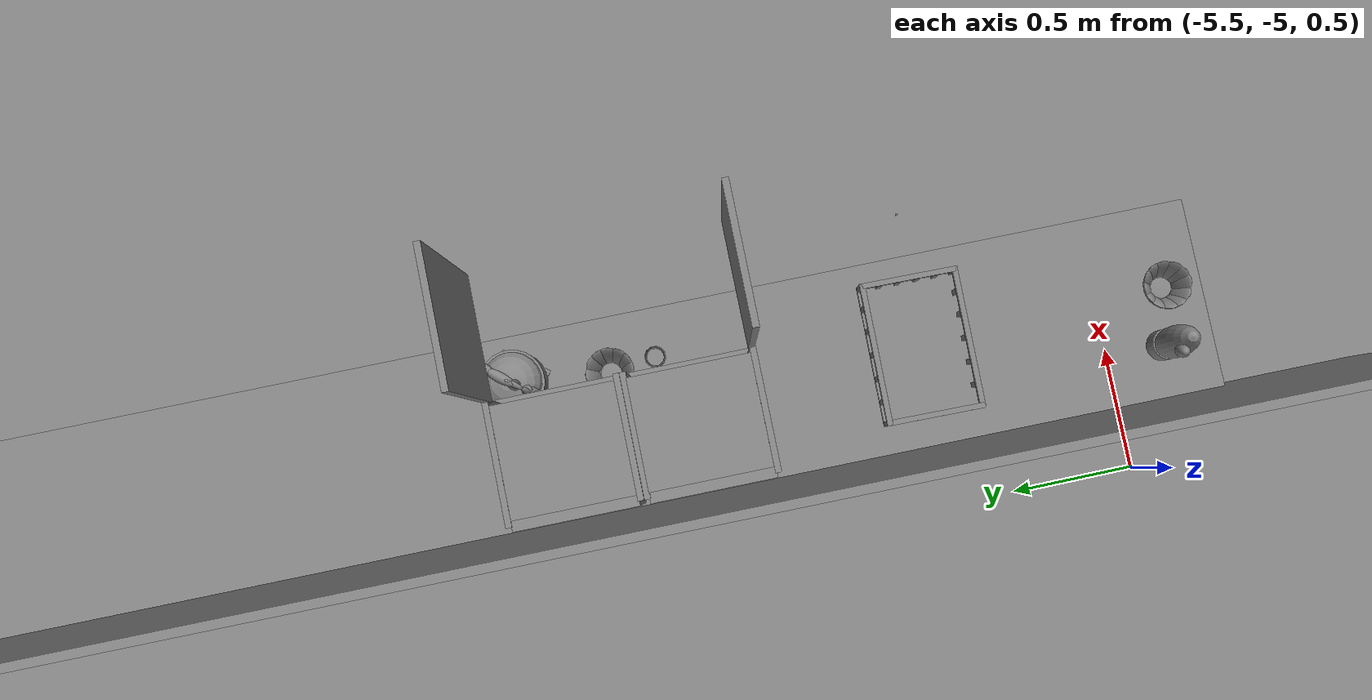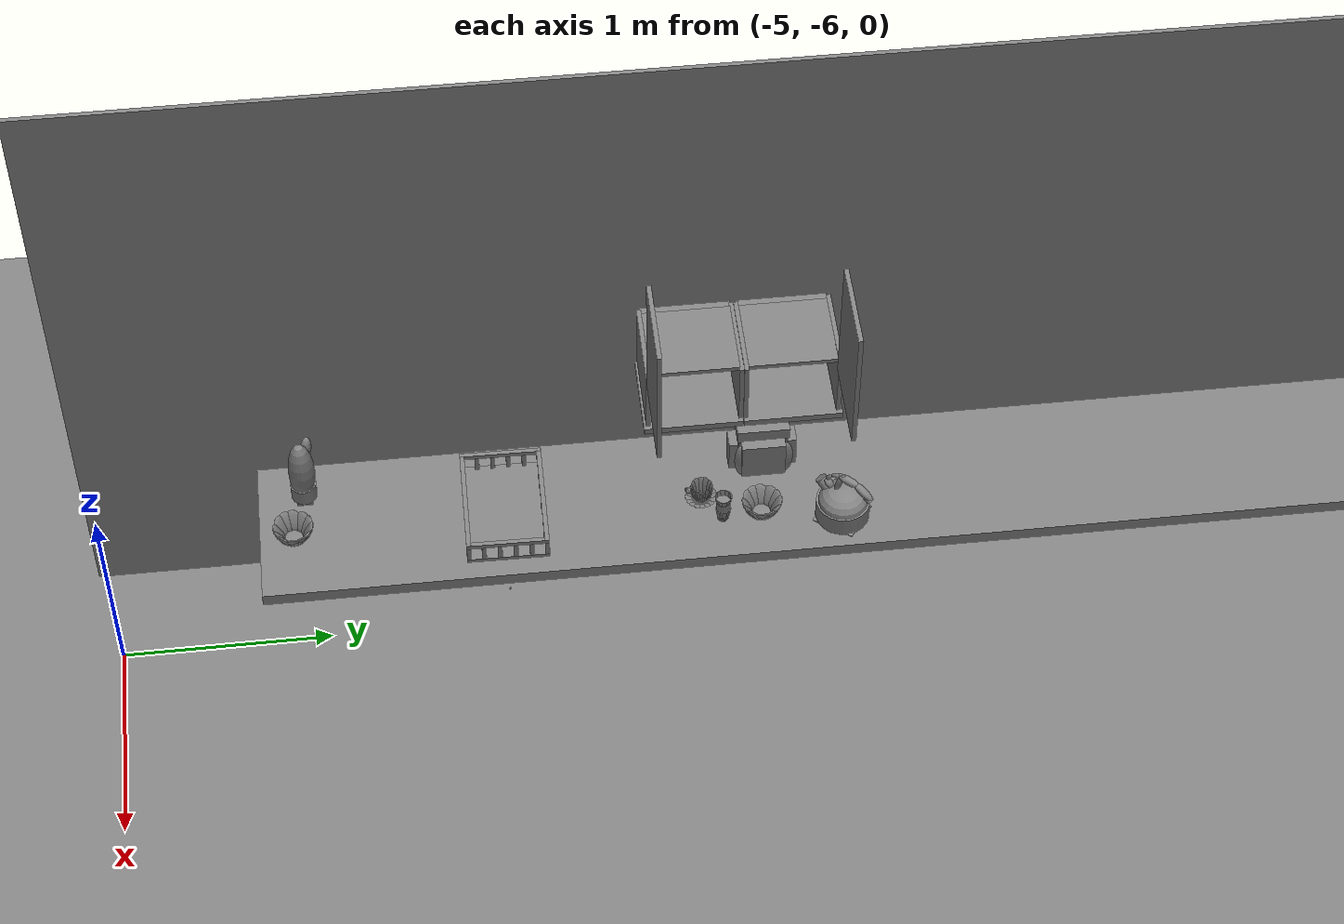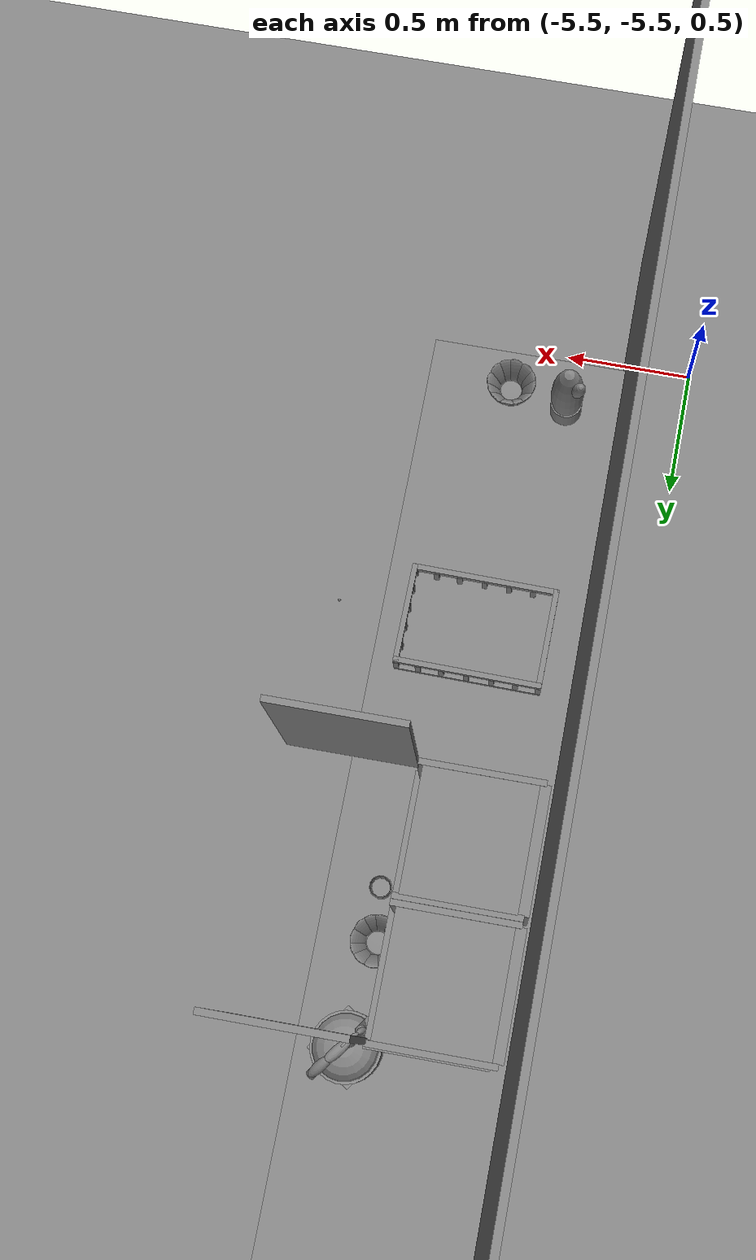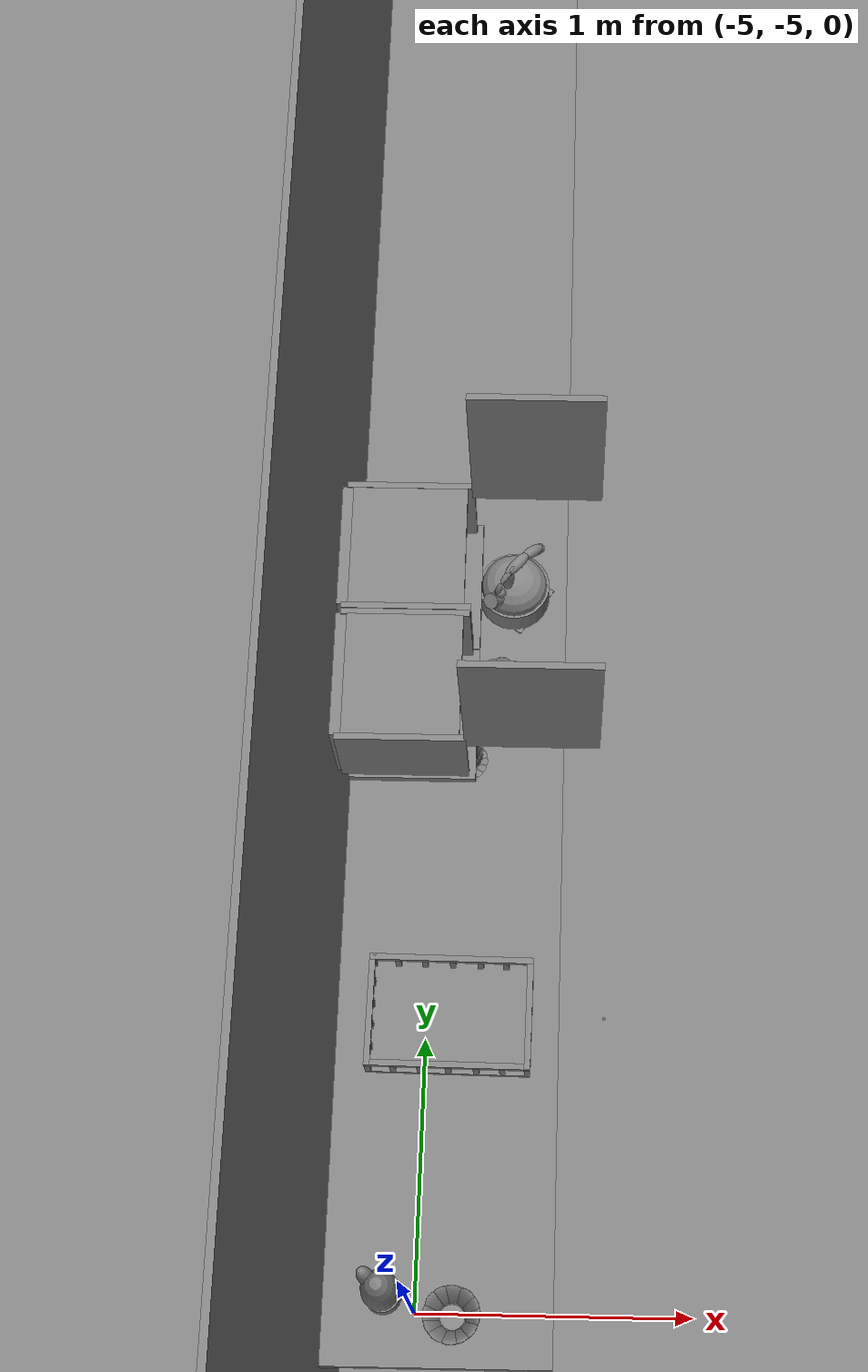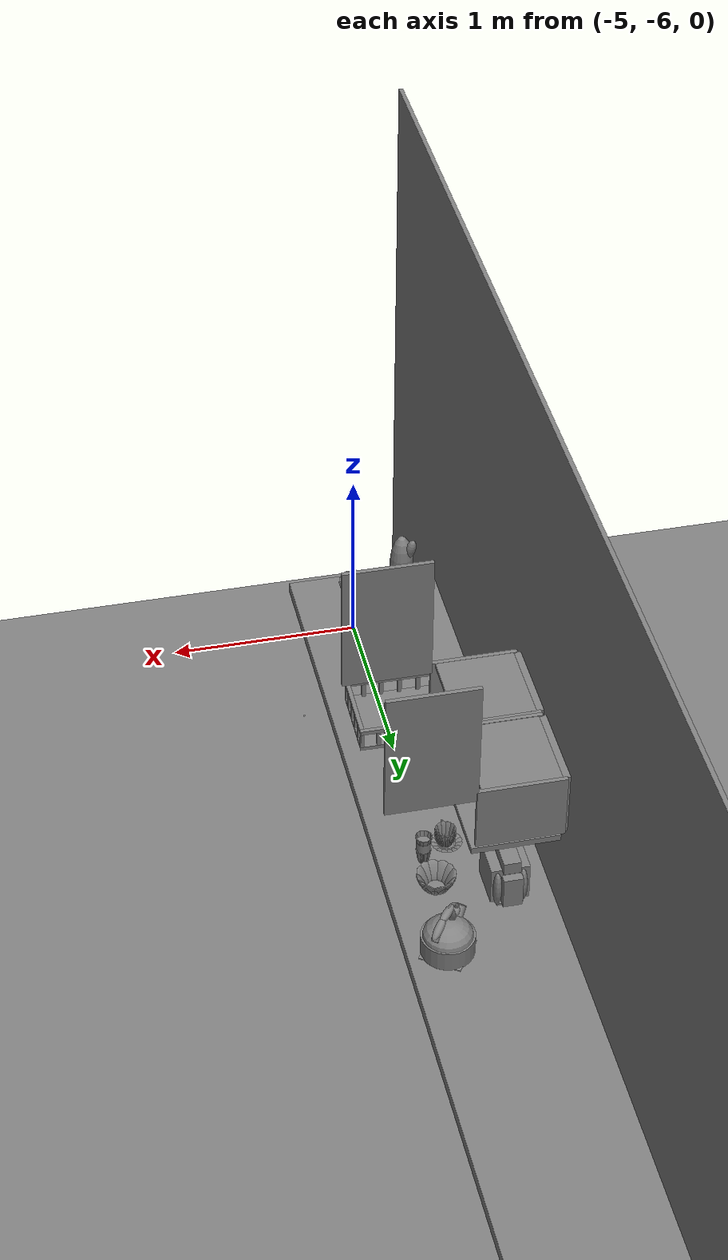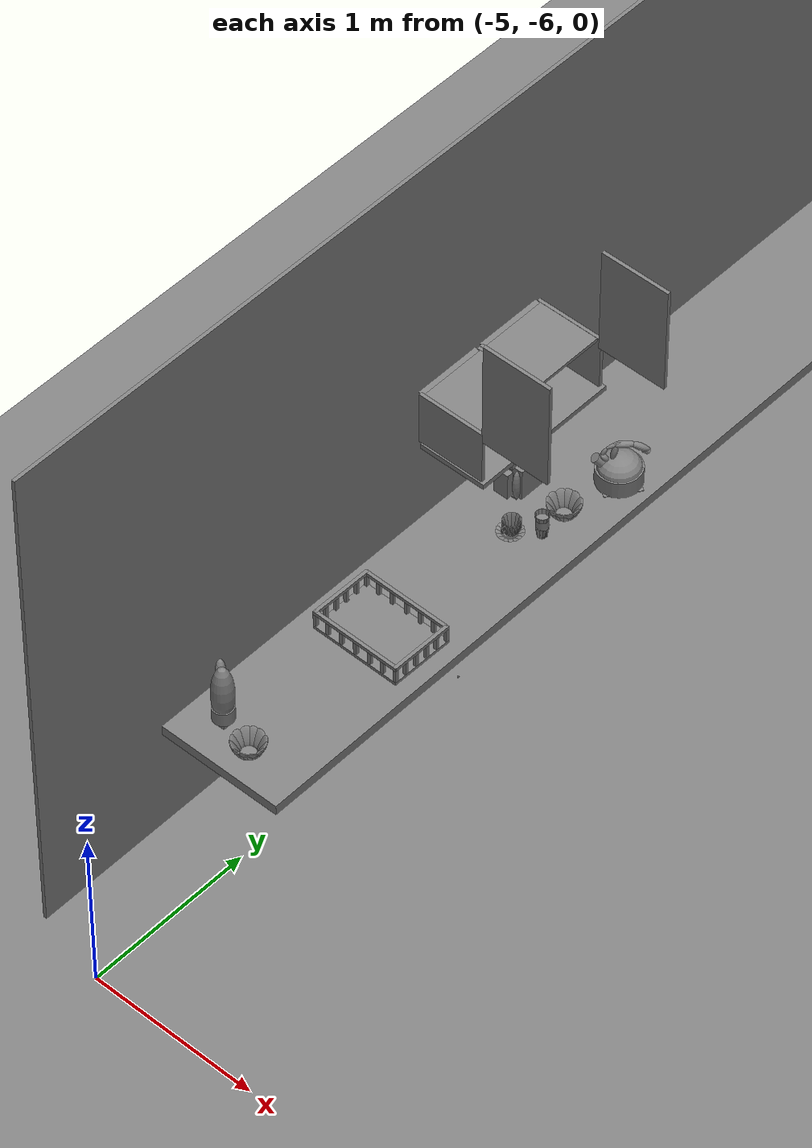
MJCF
<mujoco>
    <option gravity="0.000000000 0.000000000 -9.810000420" timestep="0.0049999999" integrator="implicitfast" density="9.8000002" viscosity="1.8000001e-05" noslip_iterations="10" iterations="100" sdf_iterations="50">
        <flag multiccd="disable"/>
    </option>
    <size memory="1000M"/>
    <compiler coordinate="local"/>
    <worldbody>
        <light cutoff="30" pos="0 1 1" dir="0 -1 -2"/>
        <light cutoff="30" pos="0 -1 1" dir="0 1 -2"/>
        <body pos="-4.827295780 -3.287638187 1.074643731" euler="0.000000000 0.000000000 89.999992371" name="Interactive Objcets_coffeecup_01">
            <geom contype="1" conaffinity="1" density="1000" type="ellipsoid" material="" rgba="0.500000000 0.500000000 0.500000000 1.000000000" solimp="0.899999976 0.949999988 0.001000000" friction="1.000000000 0.005000000 0.000100000" solref="0.020000000 1.000000000" margin="0" condim="3" group="0" pos="0.035336256 0.000558376 -0.043215394" quat="0.999999881 0.000000000 0.000000000 0.000000000" size="0.029999999 0.029999999 0.001000000" name="Interactive Objcets_geom_D7F2AE2B_62D3_4E38_BC32_524AE039774A"/>
            <geom contype="1" conaffinity="1" density="1000" type="ellipsoid" material="" rgba="0.500000000 0.500000000 0.500000000 1.000000000" solimp="0.899999976 0.949999988 0.001000000" friction="1.000000000 0.005000000 0.000100000" solref="0.020000000 1.000000000" margin="0" condim="3" group="0" pos="0.067416430 -0.018191338 0.002976775" quat="0.961934388 0.024418317 0.091648072 -0.256293803" size="0.005000000 0.029999999 0.048999999" name="Interactive Objcets_geom_AF6FE8B6_65EB_4522_B9FA_CB2CA80B47F0"/>
            <geom contype="1" conaffinity="1" density="1000" type="ellipsoid" material="" rgba="0.500000000 0.500000000 0.500000000 1.000000000" solimp="0.899999976 0.949999988 0.001000000" friction="1.000000000 0.005000000 0.000100000" solref="0.020000000 1.000000000" margin="0" condim="3" group="0" pos="0.034471050 -0.037125111 0.002976775" quat="0.701517045 0.067293778 0.066836871 -0.706313014" size="0.005000000 0.029999999 0.048999999" name="Interactive Objcets_geom_4765A247_4836_4857_93F8_8D3484692CB0"/>
            <geom contype="1" conaffinity="1" density="1000" type="ellipsoid" material="" rgba="0.500000000 0.500000000 0.500000000 1.000000000" solimp="0.899999976 0.949999988 0.001000000" friction="1.000000000 0.005000000 0.000100000" solref="0.020000000 1.000000000" margin="0" condim="3" group="0" pos="0.035336256 0.000558376 -0.045152068" quat="0.999999881 0.000000000 0.000000000 0.000000000" size="0.029999999 0.029999999 0.001000000" name="Interactive Objcets_geom_1CB20A0D_6A4F_4354_8BE4_3E034F1508D7"/>
            <geom contype="1" conaffinity="1" density="1000" type="ellipsoid" material="" rgba="0.500000000 0.500000000 0.500000000 1.000000000" solimp="0.899999976 0.949999988 0.001000000" friction="1.000000000 0.005000000 0.000100000" solref="0.020000000 1.000000000" margin="0" condim="3" group="0" pos="0.001010895 -0.016271591 0.002976775" quat="0.228377163 0.092315644 0.021758538 -0.968941689" size="0.005000000 0.029999999 0.048999999" name="Interactive Objcets_geom_0F7E3A9A_2405_47EE_9903_BBA1CCD836B2"/>
            <geom contype="1" conaffinity="1" density="1000" type="capsule" material="" rgba="0.500000000 0.500000000 0.500000000 1.000000000" solimp="0.899999976 0.949999988 0.001000000" friction="1.000000000 0.005000000 0.000100000" solref="0.020000000 1.000000000" margin="0" condim="3" group="0" pos="-0.021276474 0.000000000 0.038509369" quat="0.633189917 0.000000000 0.773996413 0.000000000" size="0.004000000 0.009000000 1.000000000" name="Interactive Objcets_geom_376D2DB6_7472_4314_9F5C_772BA1D91322"/>
            <geom contype="1" conaffinity="1" density="1000" type="capsule" material="" rgba="0.500000000 0.500000000 0.500000000 1.000000000" solimp="0.899999976 0.949999988 0.001000000" friction="1.000000000 0.005000000 0.000100000" solref="0.020000000 1.000000000" margin="0" condim="3" group="0" pos="-0.018014431 0.000000000 0.001762271" quat="0.707106769 -0.000000004 0.707106709 -0.000000088" size="0.004000000 0.005000000 1.000000000" name="Interactive Objcets_geom_B352773C_4335_42EE_810D_D3D94AC4C3E7"/>
            <geom contype="1" conaffinity="1" density="1000" type="ellipsoid" material="" rgba="0.500000000 0.500000000 0.500000000 1.000000000" solimp="0.899999976 0.949999988 0.001000000" friction="1.000000000 0.005000000 0.000100000" solref="0.020000000 1.000000000" margin="0" condim="3" group="0" pos="0.068445444 0.017385960 0.002976775" quat="0.228377223 -0.092319682 -0.021759447 -0.968941331" size="0.005000000 0.029999999 0.048999999" name="Interactive Objcets_geom_7D23909A_CB51_4872_BF2D_4FCBDDC11E52"/>
            <geom contype="1" conaffinity="1" density="1000" type="ellipsoid" material="" rgba="0.500000000 0.500000000 0.500000000 1.000000000" solimp="0.899999976 0.949999988 0.001000000" friction="1.000000000 0.005000000 0.000100000" solref="0.020000000 1.000000000" margin="0" condim="3" group="0" pos="0.002039194 0.019308567 0.002976775" quat="0.961933970 -0.024419386 -0.091652036 -0.256293654" size="0.005000000 0.029999999 0.048999999" name="Interactive Objcets_geom_22C1DFE1_EF57_4D14_AC72_04EAA838E422"/>
            <geom contype="1" conaffinity="1" density="1000" type="ellipsoid" material="" rgba="0.500000000 0.500000000 0.500000000 1.000000000" solimp="0.899999976 0.949999988 0.001000000" friction="1.000000000 0.005000000 0.000100000" solref="0.020000000 1.000000000" margin="0" condim="3" group="0" pos="0.034984604 0.038240910 0.002976775" quat="0.701516926 -0.067296736 -0.066839755 -0.706312656" size="0.005000000 0.029999999 0.048999999" name="Interactive Objcets_geom_93057CE3_3D1F_4240_BFEC_659BF3BA30F8"/>
            <geom contype="1" conaffinity="1" density="1000" type="ellipsoid" material="" rgba="0.500000000 0.500000000 0.500000000 1.000000000" solimp="0.899999976 0.949999988 0.001000000" friction="1.000000000 0.005000000 0.000100000" solref="0.020000000 1.000000000" margin="0" condim="3" group="0" pos="0.017669693 0.034160614 0.002976775" quat="0.848410904 -0.049618516 -0.080835648 -0.520770907" size="0.005000000 0.029999999 0.048999999" name="Interactive Objcets_geom_904C500C_7378_4A37_B20B_4CEDE1BB9138"/>
            <geom contype="1" conaffinity="1" density="1000" type="ellipsoid" material="" rgba="0.500000000 0.500000000 0.500000000 1.000000000" solimp="0.899999976 0.949999988 0.001000000" friction="1.000000000 0.005000000 0.000100000" solref="0.020000000 1.000000000" margin="0" condim="3" group="0" pos="-0.002956629 0.000558376 0.002976775" quat="0.995491505 0.000000004 -0.094849378 -0.000000089" size="0.005000000 0.029999999 0.048999999" name="Interactive Objcets_geom_AC6BE463_77A7_47A1_AEC0_3301EE40F696"/>
            <geom contype="1" conaffinity="1" density="1000" type="ellipsoid" material="" rgba="0.500000000 0.500000000 0.500000000 1.000000000" solimp="0.899999976 0.949999988 0.001000000" friction="1.000000000 0.005000000 0.000100000" solref="0.020000000 1.000000000" margin="0" condim="3" group="0" pos="0.051787138 -0.033043861 0.002976775" quat="0.848411202 0.049616337 0.080832161 -0.520771146" size="0.005000000 0.029999999 0.048999999" name="Interactive Objcets_geom_330AE02C_0BF2_4D2B_BF38_8E7562B54870"/>
            <geom contype="1" conaffinity="1" density="1000" type="capsule" material="" rgba="0.500000000 0.500000000 0.500000000 1.000000000" solimp="0.899999976 0.949999988 0.001000000" friction="1.000000000 0.005000000 0.000100000" solref="0.020000000 1.000000000" margin="0" condim="3" group="0" pos="-0.030251026 0.000000000 0.004966617" quat="0.480583906 -0.000000000 0.876948774 -0.000000126" size="0.004000000 0.005000000 1.000000000" name="Interactive Objcets_geom_454F0169_5AAA_4623_AAF0_8B3A258D9744"/>
            <geom contype="1" conaffinity="1" density="1000" type="capsule" material="" rgba="0.500000000 0.500000000 0.500000000 1.000000000" solimp="0.899999976 0.949999988 0.001000000" friction="1.000000000 0.005000000 0.000100000" solref="0.020000000 1.000000000" margin="0" condim="3" group="0" pos="-0.036300898 0.000000000 0.021037936" quat="0.044551343 -0.000000000 0.999007046 -0.000000126" size="0.004000000 0.012000000 1.000000000" name="Interactive Objcets_geom_5ABF818A_EE2A_4687_A3AE_CD40F913B53F"/>
            <geom contype="1" conaffinity="1" density="1000" type="capsule" material="" rgba="0.500000000 0.500000000 0.500000000 1.000000000" solimp="0.899999976 0.949999988 0.001000000" friction="1.000000000 0.005000000 0.000100000" solref="0.020000000 1.000000000" margin="0" condim="3" group="0" pos="-0.008219719 0.000000000 -0.000944734" quat="0.364379913 0.000000063 0.931250274 -0.000000063" size="0.004000000 0.003000000 1.000000000" name="Interactive Objcets_geom_95B6D1FE_E776_45E6_AB5D_54BB819993D6"/>
            <geom contype="1" conaffinity="1" density="1000" type="capsule" material="" rgba="0.500000000 0.500000000 0.500000000 1.000000000" solimp="0.899999976 0.949999988 0.001000000" friction="1.000000000 0.005000000 0.000100000" solref="0.020000000 1.000000000" margin="0" condim="3" group="0" pos="-0.033022881 0.000000000 0.037873149" quat="0.874267220 0.000000042 0.485444903 -0.000000084" size="0.004000000 0.004000000 1.000000000" name="Interactive Objcets_geom_B5F6FA7F_4AA1_4B29_BE6E_8BBE326207BD"/>
            <geom contype="1" conaffinity="1" density="1000" type="ellipsoid" material="" rgba="0.500000000 0.500000000 0.500000000 1.000000000" solimp="0.899999976 0.949999988 0.001000000" friction="1.000000000 0.005000000 0.000100000" solref="0.020000000 1.000000000" margin="0" condim="3" group="0" pos="0.015755907 -0.032001972 0.002976775" quat="0.496025920 0.082232773 0.047258731 -0.863112032" size="0.005000000 0.029999999 0.048999999" name="Interactive Objcets_geom_BA0DDB9F_8377_499E_804C_25DF2C156987"/>
            <geom contype="1" conaffinity="1" density="1000" type="ellipsoid" material="" rgba="0.500000000 0.500000000 0.500000000 1.000000000" solimp="0.899999976 0.949999988 0.001000000" friction="1.000000000 0.005000000 0.000100000" solref="0.020000000 1.000000000" margin="0" condim="3" group="0" pos="0.072411790 0.000558376 0.002976775" quat="0.995491922 -0.000000019 0.094845265 -0.000000089" size="0.005000000 0.029999999 0.048999999" name="Interactive Objcets_geom_ACD10C31_68DC_4DFD_9A07_26A32863D1CA"/>
            <geom contype="1" conaffinity="1" density="1000" type="ellipsoid" material="" rgba="0.500000000 0.500000000 0.500000000 1.000000000" solimp="0.899999976 0.949999988 0.001000000" friction="1.000000000 0.005000000 0.000100000" solref="0.020000000 1.000000000" margin="0" condim="3" group="0" pos="0.053700209 0.033117294 0.002976775" quat="0.496025741 -0.082236379 -0.047260769 -0.863111615" size="0.005000000 0.029999999 0.048999999" name="Interactive Objcets_geom_08763764_6CB5_4800_BD40_6FC3066DAC91"/>
            <freejoint name="Interactive Objcets_coffeecup_01"/>
        </body>
        <body pos="1000.000000000 1000.000000000 1.000000000" euler="0.000000000 0.000000000 0.000000000" name="openloong_gripper_2f85_fix_base_usda_bottle_red">
            <geom contype="1" conaffinity="1" density="1000" type="ellipsoid" material="" rgba="0.500000000 0.500000000 0.500000000 1.000000000" solimp="0.899999976 0.949999988 0.001000000" friction="1.000000000 0.005000000 0.000100000" solref="0.020000000 1.000000000" margin="0" condim="3" group="0" pos="0.000000000 0.000000000 0.144284487" quat="1.000000000 0.000000000 0.000000000 0.000000000" size="0.021000000 0.021000000 0.079999998" name="openloong_gripper_2f85_fix_base_usda_geom_4C6CADE9_C954_4013_BA89_819052496411"/>
            <geom contype="1" conaffinity="1" density="1000" type="cylinder" material="" rgba="0.500000000 0.500000000 0.500000000 1.000000000" solimp="0.899999976 0.949999988 0.001000000" friction="1.000000000 0.005000000 0.000100000" solref="0.020000000 1.000000000" margin="0" condim="3" group="0" pos="0.000000000 0.000000000 0.220618963" quat="1.000000000 0.000000000 0.000000000 0.000000000" size="0.016000001 0.010000000 1.000000000" name="openloong_gripper_2f85_fix_base_usda_geom_A65D8655_7153_4F3D_91D9_73C08A6A8C89"/>
            <geom contype="1" conaffinity="1" density="1000" type="ellipsoid" material="" rgba="0.500000000 0.500000000 0.500000000 1.000000000" solimp="0.899999976 0.949999988 0.001000000" friction="1.000000000 0.005000000 0.000100000" solref="0.020000000 1.000000000" margin="0" condim="3" group="0" pos="0.000000000 0.000000000 0.118945479" quat="1.000000000 0.000000000 0.000000000 0.000000000" size="0.030999999 0.030999999 0.029999999" name="openloong_gripper_2f85_fix_base_usda_geom_BF36B066_C972_4B6D_9137_7ADFBCFCF5DB"/>
            <geom contype="1" conaffinity="1" density="1000" type="box" material="" rgba="0.500000000 0.500000000 0.500000000 1.000000000" solimp="0.899999976 0.949999988 0.001000000" friction="1.000000000 0.005000000 0.000100000" solref="0.020000000 1.000000000" margin="0" condim="3" group="0" pos="0.000000000 0.000000000 0.002189159" quat="1.000000000 0.000000000 0.000000000 0.000000000" size="0.020000000 0.020000000 0.003000000" name="openloong_gripper_2f85_fix_base_usda_geom_AE55660E_9690_4264_A968_6B4801ADC2D0"/>
            <geom contype="1" conaffinity="1" density="1000" type="cylinder" material="" rgba="0.500000000 0.500000000 0.500000000 1.000000000" solimp="0.899999976 0.949999988 0.001000000" friction="1.000000000 0.005000000 0.000100000" solref="0.020000000 1.000000000" margin="0" condim="3" group="0" pos="0.000000000 -0.000366211 0.060884237" quat="1.000000000 0.000000000 0.000000000 0.000000000" size="0.030999999 0.057999998 1.000000000" name="openloong_gripper_2f85_fix_base_usda_geom_B4E45BC2_997C_445A_9639_C15365B419B1"/>
            <freejoint name="openloong_gripper_2f85_fix_base_usda_bottle_red_joint"/>
            <site size="0.005000000 0.005000000 0.005000000" rgba="0.500000000 0.500000000 0.500000000 1.000000000" pos="0.000000000 0.000000000 0.000000000" quat="0.999961913 0.008726535 0.000000000 0.000000000" group="0" type="sphere" name="openloong_gripper_2f85_fix_base_usda_bottle_redsite"/>
        </body>
        <body pos="1000.000000000 1000.000000000 1.000000000" euler="0.000000000 0.000000000 0.000000000" name="openloong_gripper_2f85_fix_base_usda_jar_01">
            <geom contype="1" conaffinity="1" density="1000" type="box" material="" rgba="0.500000000 0.500000000 0.500000000 1.000000000" solimp="0.899999976 0.949999988 0.001000000" friction="1.000000000 0.005000000 0.000100000" solref="0.020000000 1.000000000" margin="0" condim="3" group="0" pos="0.000000000 0.000000000 0.006158113" quat="1.000000000 0.000000000 0.000000000 0.000000000" size="0.020000000 0.020000000 0.005000000" name="openloong_gripper_2f85_fix_base_usda_geom_D2B4CDDE_DF03_43FD_9A94_85208912AF37"/>
            <geom contype="1" conaffinity="1" density="1000" type="cylinder" material="" rgba="0.500000000 0.500000000 0.500000000 1.000000000" solimp="0.899999976 0.949999988 0.001000000" friction="1.000000000 0.005000000 0.000100000" solref="0.020000000 1.000000000" margin="0" condim="3" group="0" pos="0.000000000 0.000000000 0.062744498" quat="1.000000000 0.000000000 0.000000000 0.000000000" size="0.041000001 0.052999999 1.000000000" name="openloong_gripper_2f85_fix_base_usda_geom_C5ED1C17_341C_430D_822F_40B08DA07953"/>
            <geom contype="1" conaffinity="1" density="1000" type="ellipsoid" material="" rgba="0.500000000 0.500000000 0.500000000 1.000000000" solimp="0.899999976 0.949999988 0.001000000" friction="1.000000000 0.005000000 0.000100000" solref="0.020000000 1.000000000" margin="0" condim="3" group="0" pos="0.000000000 0.000000000 0.122252703" quat="1.000000000 0.000000000 0.000000000 0.000000000" size="0.035999998 0.035999998 0.010000000" name="openloong_gripper_2f85_fix_base_usda_geom_5AC5D22B_1440_4DD4_BDA4_6244207F6973"/>
            <geom contype="1" conaffinity="1" density="1000" type="cylinder" material="" rgba="0.500000000 0.500000000 0.500000000 1.000000000" solimp="0.899999976 0.949999988 0.001000000" friction="1.000000000 0.005000000 0.000100000" solref="0.020000000 1.000000000" margin="0" condim="3" group="0" pos="0.000000000 0.000000000 0.015747190" quat="1.000000000 0.000000000 0.000000000 0.000000000" size="0.035000000 0.010000000 1.000000000" name="openloong_gripper_2f85_fix_base_usda_geom_D2E919FE_3916_4646_9D34_C95D9794DB72"/>
            <geom contype="1" conaffinity="1" density="1000" type="ellipsoid" material="" rgba="0.500000000 0.500000000 0.500000000 1.000000000" solimp="0.899999976 0.949999988 0.001000000" friction="1.000000000 0.005000000 0.000100000" solref="0.020000000 1.000000000" margin="0" condim="3" group="0" pos="0.000000000 0.000000000 0.115815401" quat="1.000000000 0.000000000 0.000000000 0.000000000" size="0.039999999 0.039999999 0.010000000" name="openloong_gripper_2f85_fix_base_usda_geom_F05C78B4_8EDC_493E_A789_3E0BE2D1E172"/>
            <geom contype="1" conaffinity="1" density="1000" type="cylinder" material="" rgba="0.500000000 0.500000000 0.500000000 1.000000000" solimp="0.899999976 0.949999988 0.001000000" friction="1.000000000 0.005000000 0.000100000" solref="0.020000000 1.000000000" margin="0" condim="3" group="0" pos="0.000000000 0.000000000 0.133183479" quat="1.000000000 0.000000000 0.000000000 0.000000000" size="0.037999999 0.006500000 1.000000000" name="openloong_gripper_2f85_fix_base_usda_geom_579A7DD5_C844_4333_9CFC_F04B159E729B"/>
            <freejoint name="openloong_gripper_2f85_fix_base_usda_jar_01_joint"/>
            <site size="0.005000000 0.005000000 0.005000000" rgba="0.500000000 0.500000000 0.500000000 1.000000000" pos="0.000000000 0.000000000 0.000000000" quat="1.000000000 0.000000000 0.000000000 0.000000000" group="0" type="sphere" name="openloong_gripper_2f85_fix_base_usda_jar_01site"/>
        </body>
        <body pos="-4.480014801 -4.441754341 1.781545401" euler="91.996879578 40.270908356 160.800735474" mocap="true" name="spotlight4_SpotLight"/>
        <body pos="0.000000000 0.000000000 0.000000000" euler="0.000000000 0.000000000 0.000000000" name="Static Objcets_Static Objcets">
            <geom contype="1" conaffinity="1" density="1000" type="box" material="" rgba="0.500000000 0.500000000 0.500000000 1.000000000" solimp="0.899999976 0.949999988 0.001000000" friction="1.000000000 0.005000000 0.000100000" solref="0.020000000 1.000000000" margin="0" condim="3" group="0" pos="-5.189302921 -3.293644905 1.760152459" quat="0.707107067 0.707106471 0.000000000 0.000000000" size="0.025000000 0.159999996 0.200000003" name="Static Objcets_geom_1A31ED12_B3DF_4C25_B478_30AAE95DBB28"/>
            <geom contype="1" conaffinity="1" density="1000" type="box" material="" rgba="0.500000000 0.500000000 0.500000000 1.000000000" solimp="0.899999976 0.949999988 0.001000000" friction="1.000000000 0.005000000 0.000100000" solref="0.020000000 1.000000000" margin="0" condim="3" group="0" pos="-4.999745846 -3.497932911 1.764780521" quat="0.707107067 0.707106471 0.000000000 0.000000000" size="0.200000003 0.159999996 0.010000000" name="Static Objcets_geom_EA1BABEA_272B_443A_99B1_77EB52408C92"/>
            <geom contype="1" conaffinity="1" density="1000" type="box" material="" rgba="0.500000000 0.500000000 0.500000000 1.000000000" solimp="0.899999976 0.949999988 0.001000000" friction="1.000000000 0.005000000 0.000100000" solref="0.020000000 1.000000000" margin="0" condim="3" group="0" pos="-4.979488373 -3.297635794 1.591412544" quat="0.707106829 0.707106709 0.000000000 0.000000000" size="0.200000003 0.015000000 0.219999999" name="Static Objcets_geom_57283FF2_13CB_4EF7_9C53_10E26AD8EC52"/>
            <geom contype="1" conaffinity="1" density="1000" type="box" material="" rgba="0.500000000 0.500000000 0.500000000 1.000000000" solimp="0.899999976 0.949999988 0.001000000" friction="1.000000000 0.005000000 0.000100000" solref="0.020000000 1.000000000" margin="0" condim="3" group="0" pos="-4.999745846 -3.087441683 1.763863802" quat="0.707107067 0.707106471 0.000000000 0.000000000" size="0.200000003 0.159999996 0.010000000" name="Static Objcets_geom_28791950_380A_4C63_B656_8DA4754F7BE3"/>
            <geom contype="1" conaffinity="1" density="1000" type="box" material="" rgba="0.500000000 0.500000000 0.500000000 1.000000000" solimp="0.899999976 0.949999988 0.001000000" friction="1.000000000 0.005000000 0.000100000" solref="0.020000000 1.000000000" margin="0" condim="3" group="0" pos="-5.000125408 -3.294431210 1.913951039" quat="0.707107067 0.707106471 0.000000000 0.000000000" size="0.180000007 0.010000000 0.200000003" name="Static Objcets_geom_C596E182_A0A3_4F39_91B5_CAB7EA933449"/>
            <geom contype="1" conaffinity="1" density="1000" type="box" material="" rgba="0.500000000 0.500000000 0.500000000 1.000000000" solimp="0.899999976 0.949999988 0.001000000" friction="1.000000000 0.005000000 0.000100000" solref="0.020000000 1.000000000" margin="0" condim="3" group="0" pos="-4.873187065 -2.461376429 0.977675021" quat="0.707107067 0.707106471 0.000000000 0.000000000" size="0.370000005 0.029999999 2.799999952" name="Static Objcets_geom_52E0C81E_292F_454C_A134_BFFAD8969C71"/>
            <geom contype="1" conaffinity="1" density="1000" type="box" material="" rgba="0.500000000 0.500000000 0.500000000 1.000000000" solimp="0.899999976 0.949999988 0.001000000" friction="1.000000000 0.005000000 0.000100000" solref="0.020000000 1.000000000" margin="0" condim="3" group="0" pos="-5.244853973 -2.375543594 1.820221663" quat="0.707107008 0.707106531 0.000000000 0.000000000" size="0.010000000 1.500000000 3.700000048" name="Static Objcets_geom_75A1867D_5F26_4532_8999_2537092637FD"/>
            <geom contype="1" conaffinity="1" density="1000" type="box" material="" rgba="0.500000000 0.500000000 0.500000000 1.000000000" solimp="0.899999976 0.949999988 0.001000000" friction="1.000000000 0.005000000 0.000100000" solref="0.020000000 1.000000000" margin="0" condim="3" group="0" pos="-0.720102787 0.222944975 -1.102830648" quat="0.000000954 1.000000000 0.000000000 0.000000000" size="8.000000000 8.000000000 0.010000000" name="Static Objcets_geom_819173DA_112D_49B1_8852_68C5D32C2DE2"/>
            <geom contype="1" conaffinity="1" density="1000" type="box" material="" rgba="0.500000000 0.500000000 0.500000000 1.000000000" solimp="0.899999976 0.949999988 0.001000000" friction="1.000000000 0.005000000 0.000100000" solref="0.020000000 1.000000000" margin="0" condim="3" group="0" pos="-4.999745846 -2.653569937 1.764779806" quat="0.707107067 0.707106471 0.000000000 0.000000000" size="0.200000003 0.159999996 0.010000000" name="Static Objcets_geom_9EEE582A_F39A_4102_9293_476EE77F7AC0"/>
            <geom contype="1" conaffinity="1" density="1000" type="box" material="" rgba="0.500000000 0.500000000 0.500000000 1.000000000" solimp="0.899999976 0.949999988 0.001000000" friction="1.000000000 0.005000000 0.000100000" solref="0.020000000 1.000000000" margin="0" condim="3" group="0" pos="-5.000125408 -2.861802340 1.913950682" quat="0.707107067 0.707106471 0.000000000 0.000000000" size="0.180000007 0.010000000 0.200000003" name="Static Objcets_geom_C432AFAF_04DE_40CA_8C73_9825EA9C709E"/>
            <geom contype="1" conaffinity="1" density="1000" type="box" material="" rgba="0.500000000 0.500000000 0.500000000 1.000000000" solimp="0.899999976 0.949999988 0.001000000" friction="1.000000000 0.005000000 0.000100000" solref="0.020000000 1.000000000" margin="0" condim="3" group="0" pos="-5.189302921 -2.861564636 1.760152102" quat="0.707107067 0.707106471 0.000000000 0.000000000" size="0.025000000 0.159999996 0.200000003" name="Static Objcets_geom_AE982D4B_2735_4E6D_8016_281ADAFA9070"/>
            <geom contype="1" conaffinity="1" density="1000" type="box" material="" rgba="0.500000000 0.500000000 0.500000000 1.000000000" solimp="0.899999976 0.949999988 0.001000000" friction="1.000000000 0.005000000 0.000100000" solref="0.020000000 1.000000000" margin="0" condim="3" group="0" pos="-4.979488373 -2.855390549 1.591412187" quat="0.707106709 0.707106769 0.000000000 0.000000000" size="0.200000003 0.015000000 0.219999999" name="Static Objcets_geom_2B50A0D6_981B_4806_916C_98BCE05DAF61"/>
            <geom contype="1" conaffinity="1" density="1000" type="box" material="" rgba="0.500000000 0.500000000 0.500000000 1.000000000" solimp="0.899999976 0.949999988 0.001000000" friction="1.000000000 0.005000000 0.000100000" solref="0.020000000 1.000000000" margin="0" condim="3" group="0" pos="-4.999745846 -3.066934109 1.765979409" quat="0.707107067 0.707106471 0.000000000 0.000000000" size="0.200000003 0.159999996 0.010000000" name="Static Objcets_geom_C41471DA_44DE_418D_B7F8_FDAFBBE37BAA"/>
        </body>
        <body pos="-4.705342293 -3.169416904 1.103703976" euler="0.000000000 0.000000000 0.000000000" name="Interactive Objcets_cup_02">
            <geom contype="1" conaffinity="1" density="1000" type="box" material="" rgba="0.500000000 0.500000000 0.500000000 1.000000000" solimp="0.899999976 0.949999988 0.001000000" friction="1.000000000 0.005000000 0.000100000" solref="0.020000000 1.000000000" margin="0" condim="3" group="0" pos="0.022285938 0.016949892 -0.037281752" quat="0.893179297 -0.070051625 0.034732576 -0.442851186" size="0.010000000 0.001000000 0.035000000" name="Interactive Objcets_geom_A14B7A08_F9BD_45C0_879C_7A19F23B3142"/>
            <geom contype="1" conaffinity="1" density="1000" type="box" material="" rgba="0.500000000 0.500000000 0.500000000 1.000000000" solimp="0.899999976 0.949999988 0.001000000" friction="1.000000000 0.005000000 0.000100000" solref="0.020000000 1.000000000" margin="0" condim="3" group="0" pos="0.034549713 0.000000000 0.062637210" quat="0.704941988 -0.055288255 0.055288251 -0.704942048" size="0.010000000 0.001000000 0.015000000" name="Interactive Objcets_geom_B7A9A279_7E28_4712_8A2D_2609064DF45E"/>
            <geom contype="1" conaffinity="1" density="1000" type="box" material="" rgba="0.500000000 0.500000000 0.500000000 1.000000000" solimp="0.899999976 0.949999988 0.001000000" friction="1.000000000 0.005000000 0.000100000" solref="0.020000000 1.000000000" margin="0" condim="3" group="0" pos="0.029378891 -0.018181801 0.062637210" quat="0.870895982 0.068302706 0.038053915 0.485208035" size="0.010000000 0.001000000 0.015000000" name="Interactive Objcets_geom_35C87780_D01D_445B_A12B_F70E9861084B"/>
            <geom contype="1" conaffinity="1" density="1000" type="box" material="" rgba="0.500000000 0.500000000 0.500000000 1.000000000" solimp="0.899999976 0.949999988 0.001000000" friction="1.000000000 0.005000000 0.000100000" solref="0.020000000 1.000000000" margin="0" condim="3" group="0" pos="0.000000000 -0.034549713 0.062637210" quat="0.996938646 0.078187965 0.000000000 0.000000000" size="0.010000000 0.001000000 0.015000000" name="Interactive Objcets_geom_1E777440_A798_49AA_BF5D_AF6853D40297"/>
            <geom contype="1" conaffinity="1" density="1000" type="cylinder" material="" rgba="0.500000000 0.500000000 0.500000000 1.000000000" solimp="0.899999976 0.949999988 0.001000000" friction="1.000000000 0.005000000 0.000100000" solref="0.020000000 1.000000000" margin="0" condim="3" group="0" pos="0.000000000 0.000000000 0.022491097" quat="1.000000000 0.000000030 0.000000000 0.000000000" size="0.033000000 0.025000000 1.000000000" name="Interactive Objcets_geom_7326A368_26F4_4B63_8DE3_E66D37E25683"/>
            <geom contype="1" conaffinity="1" density="1000" type="box" material="" rgba="0.500000000 0.500000000 0.500000000 1.000000000" solimp="0.899999976 0.949999988 0.001000000" friction="1.000000000 0.005000000 0.000100000" solref="0.020000000 1.000000000" margin="0" condim="3" group="0" pos="0.000000000 0.034549713 0.062637210" quat="0.996938646 -0.078187965 0.000000000 0.000000000" size="0.010000000 0.001000000 0.015000000" name="Interactive Objcets_geom_2870DEA4_B1CC_43B0_9616_0513D21F8FAA"/>
            <geom contype="1" conaffinity="1" density="1000" type="box" material="" rgba="0.500000000 0.500000000 0.500000000 1.000000000" solimp="0.899999976 0.949999988 0.001000000" friction="1.000000000 0.005000000 0.000100000" solref="0.020000000 1.000000000" margin="0" condim="3" group="0" pos="0.011943817 0.025323629 -0.037281752" quat="0.972834349 -0.076298930 0.017089661 -0.217898533" size="0.010000000 0.001000000 0.035000000" name="Interactive Objcets_geom_AE2A605A_E54B_48D3_AC1F_E80B8AD08780"/>
            <geom contype="1" conaffinity="1" density="1000" type="box" material="" rgba="0.500000000 0.500000000 0.500000000 1.000000000" solimp="0.899999976 0.949999988 0.001000000" friction="1.000000000 0.005000000 0.000100000" solref="0.020000000 1.000000000" margin="0" condim="3" group="0" pos="0.025214195 -0.011892319 -0.037281752" quat="0.841975451 0.066034243 0.041866414 0.533820212" size="0.010000000 0.001000000 0.035000000" name="Interactive Objcets_geom_F18092DA_3614_43AE_9475_D6D9BA002FE8"/>
            <geom contype="1" conaffinity="1" density="1000" type="box" material="" rgba="0.500000000 0.500000000 0.500000000 1.000000000" solimp="0.899999976 0.949999988 0.001000000" friction="1.000000000 0.005000000 0.000100000" solref="0.020000000 1.000000000" margin="0" condim="3" group="0" pos="-0.027999878 0.000000000 -0.037281752" quat="0.704941988 0.055288255 -0.055288251 -0.704942048" size="0.010000000 0.001000000 0.035000000" name="Interactive Objcets_geom_1E183BD3_F4DB_41A7_BB7D_5ADE86EA5854"/>
            <geom contype="1" conaffinity="1" density="1000" type="box" material="" rgba="0.500000000 0.500000000 0.500000000 1.000000000" solimp="0.899999976 0.949999988 0.001000000" friction="1.000000000 0.005000000 0.000100000" solref="0.020000000 1.000000000" margin="0" condim="3" group="0" pos="0.017436981 -0.029826880 0.062637210" quat="0.962265730 0.075468659 0.020441191 0.260636479" size="0.010000000 0.001000000 0.015000000" name="Interactive Objcets_geom_6F4DFB08_F472_4138_8808_1A6F70E8012F"/>
            <geom contype="1" conaffinity="1" density="1000" type="box" material="" rgba="0.500000000 0.500000000 0.500000000 1.000000000" solimp="0.899999976 0.949999988 0.001000000" friction="1.000000000 0.005000000 0.000100000" solref="0.020000000 1.000000000" margin="0" condim="3" group="0" pos="0.029827118 0.017437220 0.062637210" quat="0.864722252 -0.067819774 0.038910985 -0.496126890" size="0.010000000 0.001000000 0.015000000" name="Interactive Objcets_geom_3C9B2948_6D7E_4F11_9C88_0DEC3CE6F6B3"/>
            <geom contype="1" conaffinity="1" density="1000" type="box" material="" rgba="0.500000000 0.500000000 0.500000000 1.000000000" solimp="0.899999976 0.949999988 0.001000000" friction="1.000000000 0.005000000 0.000100000" solref="0.020000000 1.000000000" margin="0" condim="3" group="0" pos="0.000000000 0.027877331 -0.037281752" quat="0.996938646 -0.078187965 0.000000000 0.000000000" size="0.010000000 0.001000000 0.035000000" name="Interactive Objcets_geom_ACC23130_A770_40D8_BE0D_0C321F4948BC"/>
            <geom contype="1" conaffinity="1" density="1000" type="box" material="" rgba="0.500000000 0.500000000 0.500000000 1.000000000" solimp="0.899999976 0.949999988 0.001000000" friction="1.000000000 0.005000000 0.000100000" solref="0.020000000 1.000000000" margin="0" condim="3" group="0" pos="-0.025214195 0.011891127 -0.037281752" quat="0.841975451 -0.066034243 -0.041866414 0.533820212" size="0.010000000 0.001000000 0.035000000" name="Interactive Objcets_geom_FED53732_0D09_417C_9EE1_AC8EA2E3101E"/>
            <geom contype="1" conaffinity="1" density="1000" type="box" material="" rgba="0.500000000 0.500000000 0.500000000 1.000000000" solimp="0.899999976 0.949999988 0.001000000" friction="1.000000000 0.005000000 0.000100000" solref="0.020000000 1.000000000" margin="0" condim="3" group="0" pos="-0.022286415 -0.016949654 -0.037281752" quat="0.893179297 0.070051625 -0.034732576 -0.442851186" size="0.010000000 0.001000000 0.035000000" name="Interactive Objcets_geom_E25523C4_B769_4882_AD8D_37A0E998F82D"/>
            <geom contype="1" conaffinity="1" density="1000" type="box" material="" rgba="0.500000000 0.500000000 0.500000000 1.000000000" solimp="0.899999976 0.949999988 0.001000000" friction="1.000000000 0.005000000 0.000100000" solref="0.020000000 1.000000000" margin="0" condim="3" group="0" pos="-0.016875744 0.022189617 -0.037281752" quat="0.944716334 -0.074092269 -0.024973858 0.318430305" size="0.010000000 0.001000000 0.035000000" name="Interactive Objcets_geom_C5CCC13C_3D79_4661_99EA_706ED6186B32"/>
            <geom contype="1" conaffinity="1" density="1000" type="box" material="" rgba="0.500000000 0.500000000 0.500000000 1.000000000" solimp="0.899999976 0.949999988 0.001000000" friction="1.000000000 0.005000000 0.000100000" solref="0.020000000 1.000000000" margin="0" condim="3" group="0" pos="0.018182278 0.029379368 0.062637210" quat="0.958910167 -0.075206861 0.021389510 -0.272722572" size="0.010000000 0.001000000 0.015000000" name="Interactive Objcets_geom_27C1121C_796F_4396_88A6_2F9FE2AC34B5"/>
            <geom contype="1" conaffinity="1" density="1000" type="box" material="" rgba="0.500000000 0.500000000 0.500000000 1.000000000" solimp="0.899999976 0.949999988 0.001000000" friction="1.000000000 0.005000000 0.000100000" solref="0.020000000 1.000000000" margin="0" condim="3" group="0" pos="0.000000000 0.000000000 -0.075536966" quat="1.000000000 0.000000000 0.000000000 0.000000000" size="0.015000000 0.015000000 0.002000000" name="Interactive Objcets_geom_DBBD6A8F_FC78_4DF7_8B96_771AF8F83525"/>
            <geom contype="1" conaffinity="1" density="1000" type="box" material="" rgba="0.500000000 0.500000000 0.500000000 1.000000000" solimp="0.899999976 0.949999988 0.001000000" friction="1.000000000 0.005000000 0.000100000" solref="0.020000000 1.000000000" margin="0" condim="3" group="0" pos="-0.018181324 -0.029377937 0.062637210" quat="0.958910167 0.075206861 -0.021389510 -0.272722572" size="0.010000000 0.001000000 0.015000000" name="Interactive Objcets_geom_4FE2F181_6081_4C2C_8735_304CEA991A6F"/>
            <geom contype="1" conaffinity="1" density="1000" type="box" material="" rgba="0.500000000 0.500000000 0.500000000 1.000000000" solimp="0.899999976 0.949999988 0.001000000" friction="1.000000000 0.005000000 0.000100000" solref="0.020000000 1.000000000" margin="0" condim="3" group="0" pos="0.027999878 0.000000000 -0.037281752" quat="0.704941988 -0.055288255 0.055288251 -0.704942048" size="0.010000000 0.001000000 0.035000000" name="Interactive Objcets_geom_2FEAC794_678F_479B_9AF7_CA608346A04B"/>
            <geom contype="1" conaffinity="1" density="1000" type="box" material="" rgba="0.500000000 0.500000000 0.500000000 1.000000000" solimp="0.899999976 0.949999988 0.001000000" friction="1.000000000 0.005000000 0.000100000" solref="0.020000000 1.000000000" margin="0" condim="3" group="0" pos="0.016875744 -0.022189379 -0.037281752" quat="0.944716334 0.074092269 0.024973858 0.318430305" size="0.010000000 0.001000000 0.035000000" name="Interactive Objcets_geom_E8737616_1F28_48AA_B7D7_6AA219DD828C"/>
            <geom contype="1" conaffinity="1" density="1000" type="box" material="" rgba="0.500000000 0.500000000 0.500000000 1.000000000" solimp="0.899999976 0.949999988 0.001000000" friction="1.000000000 0.005000000 0.000100000" solref="0.020000000 1.000000000" margin="0" condim="3" group="0" pos="-0.029377937 0.018182278 0.062637210" quat="0.870895982 -0.068302706 -0.038053915 0.485208035" size="0.010000000 0.001000000 0.015000000" name="Interactive Objcets_geom_BB7FCB81_17A9_40DF_88AE_B5741E8566CE"/>
            <geom contype="1" conaffinity="1" density="1000" type="box" material="" rgba="0.500000000 0.500000000 0.500000000 1.000000000" solimp="0.899999976 0.949999988 0.001000000" friction="1.000000000 0.005000000 0.000100000" solref="0.020000000 1.000000000" margin="0" condim="3" group="0" pos="-0.017436504 0.029826880 0.062637210" quat="0.962265730 -0.075468659 -0.020441191 0.260636479" size="0.010000000 0.001000000 0.015000000" name="Interactive Objcets_geom_6AC679DB_EBEB_4634_9A28_9EFBD80A36B7"/>
            <geom contype="1" conaffinity="1" density="1000" type="box" material="" rgba="0.500000000 0.500000000 0.500000000 1.000000000" solimp="0.899999976 0.949999988 0.001000000" friction="1.000000000 0.005000000 0.000100000" solref="0.020000000 1.000000000" margin="0" condim="3" group="0" pos="-0.034549713 0.000000000 0.062637210" quat="0.704941988 0.055288255 -0.055288251 -0.704942048" size="0.010000000 0.001000000 0.015000000" name="Interactive Objcets_geom_F17138B4_76D7_4BA2_AE5F_95DBAF954434"/>
            <geom contype="1" conaffinity="1" density="1000" type="box" material="" rgba="0.500000000 0.500000000 0.500000000 1.000000000" solimp="0.899999976 0.949999988 0.001000000" friction="1.000000000 0.005000000 0.000100000" solref="0.020000000 1.000000000" margin="0" condim="3" group="0" pos="-0.029826641 -0.017436504 0.062637210" quat="0.864722252 0.067819774 -0.038910985 -0.496126890" size="0.010000000 0.001000000 0.015000000" name="Interactive Objcets_geom_CDE68F4B_C83F_40D3_A844_5DFD31DE5F63"/>
            <geom contype="1" conaffinity="1" density="1000" type="box" material="" rgba="0.500000000 0.500000000 0.500000000 1.000000000" solimp="0.899999976 0.949999988 0.001000000" friction="1.000000000 0.005000000 0.000100000" solref="0.020000000 1.000000000" margin="0" condim="3" group="0" pos="0.000000000 -0.027877331 -0.037281752" quat="0.996938646 0.078187965 0.000000000 0.000000000" size="0.010000000 0.001000000 0.035000000" name="Interactive Objcets_geom_4E5C3756_02EA_4261_81C1_79434E9FA219"/>
            <freejoint name="Interactive Objcets_cup_02"/>
        </body>
        <body pos="-5.046103477 -5.051773071 1.001502514" euler="0.000000000 0.000000000 0.000000000" name="Interactive Objcets_huapen">
            <geom contype="1" conaffinity="1" density="1000" type="ellipsoid" material="" rgba="0.500000000 0.500000000 0.500000000 1.000000000" solimp="0.899999976 0.949999988 0.001000000" friction="1.000000000 0.005000000 0.000100000" solref="0.020000000 1.000000000" margin="0" condim="3" group="0" pos="0.008062840 0.004346371 0.205056787" quat="1.000000000 0.000000000 0.000000000 0.000000000" size="0.059999999 0.059999999 0.180000007" name="Interactive Objcets_huapen_hua_8F78D535_D316_4AD5_A2BA_FF268CE8275B"/>
            <geom contype="1" conaffinity="1" density="1000" type="ellipsoid" material="" rgba="0.500000000 0.500000000 0.500000000 1.000000000" solimp="0.899999976 0.949999988 0.001000000" friction="1.000000000 0.005000000 0.000100000" solref="0.020000000 1.000000000" margin="0" condim="3" group="0" pos="-0.029900074 0.033599377 0.321917295" quat="0.992658079 -0.083605267 -0.087364964 0.002748166" size="0.025000000 0.025000000 0.059999999" name="Interactive Objcets_huapen_hua_3E28FD9C_8C83_4E77_B250_76D51F9AC7B8"/>
            <geom contype="1" conaffinity="1" density="1000" type="box" material="" rgba="0.500000000 0.500000000 0.500000000 1.000000000" solimp="0.899999976 0.949999988 0.001000000" friction="1.000000000 0.005000000 0.000100000" solref="0.020000000 1.000000000" margin="0" condim="3" group="0" pos="0.008062840 0.003952503 0.020566106" quat="1.000000000 0.000000000 0.000000000 0.000000000" size="0.035000000 0.035000000 0.020000000" name="Interactive Objcets_huapen_hua_31A18D22_3F62_4BBD_A90C_77365C0D4643"/>
            <geom contype="1" conaffinity="1" density="1000" type="cylinder" material="" rgba="0.500000000 0.500000000 0.500000000 1.000000000" solimp="0.899999976 0.949999988 0.001000000" friction="1.000000000 0.005000000 0.000100000" solref="0.020000000 1.000000000" margin="0" condim="3" group="0" pos="0.008062840 0.003952026 0.080107450" quat="1.000000000 0.000000000 0.000000000 0.000000000" size="0.057999998 0.039999999 1.000000000" name="Interactive Objcets_huapen_hua_9279AFF0_1372_4C61_8AE5_FF8843A75212"/>
            <freejoint name="Interactive Objcets_huapen"/>
        </body>
        <body pos="-4.721817970 -2.990536690 1.027358174" euler="0.000000000 0.000000000 89.999946594" name="Interactive Objcets_bow_02">
            <geom contype="1" conaffinity="1" density="1000" type="ellipsoid" material="" rgba="0.500000000 0.500000000 0.500000000 1.000000000" solimp="0.899999976 0.949999988 0.001000000" friction="1.000000000 0.005000000 0.000100000" solref="0.020000000 1.000000000" margin="0" condim="3" group="0" pos="0.052321676 -0.040297508 0.044118762" quat="0.919264674 0.076882742 0.225593731 -0.313287675" size="0.010000000 0.039999999 0.052000001" name="Interactive Objcets_geom_5D3929D5_75C2_4609_A66C_830E8E1279C1"/>
            <geom contype="1" conaffinity="1" density="1000" type="ellipsoid" material="" rgba="0.500000000 0.500000000 0.500000000 1.000000000" solimp="0.899999976 0.949999988 0.001000000" friction="1.000000000 0.005000000 0.000100000" solref="0.020000000 1.000000000" margin="0" condim="3" group="0" pos="0.040234569 0.052338600 0.044118762" quat="0.429593176 -0.213750035 -0.105424814 -0.871002913" size="0.010000000 0.039999999 0.052000001" name="Interactive Objcets_geom_A7505A7D_501F_4DBB_81F8_C358CC7C0A12"/>
            <geom contype="1" conaffinity="1" density="1000" type="ellipsoid" material="" rgba="0.500000000 0.500000000 0.500000000 1.000000000" solimp="0.899999976 0.949999988 0.001000000" friction="1.000000000 0.005000000 0.000100000" solref="0.020000000 1.000000000" margin="0" condim="3" group="0" pos="0.029448029 -0.059084892 0.044118762" quat="0.825555801 0.125530601 0.202597082 -0.511521280" size="0.010000000 0.039999999 0.052000001" name="Interactive Objcets_geom_77AA38B0_924B_4E3B_81E7_49CD29CB0231"/>
            <geom contype="1" conaffinity="1" density="1000" type="ellipsoid" material="" rgba="0.500000000 0.500000000 0.500000000 1.000000000" solimp="0.899999976 0.949999988 0.001000000" friction="1.000000000 0.005000000 0.000100000" solref="0.020000000 1.000000000" margin="0" condim="3" group="0" pos="-0.058925860 -0.029528141 0.044118762" quat="0.223252773 0.231952101 0.054787740 -0.945174515" size="0.010000000 0.039999999 0.052000001" name="Interactive Objcets_geom_89E7256D_648C_4497_BF3A_33195987637F"/>
            <geom contype="1" conaffinity="1" density="1000" type="ellipsoid" material="" rgba="0.500000000 0.500000000 0.500000000 1.000000000" solimp="0.899999976 0.949999988 0.001000000" friction="1.000000000 0.005000000 0.000100000" solref="0.020000000 1.000000000" margin="0" condim="3" group="0" pos="-0.040080305 -0.052354336 0.044118762" quat="0.429593205 0.213749886 0.105425082 -0.871003032" size="0.010000000 0.039999999 0.052000001" name="Interactive Objcets_geom_147DEE93_18F8_4245_A671_5489754C467A"/>
            <geom contype="1" conaffinity="1" density="1000" type="ellipsoid" material="" rgba="0.500000000 0.500000000 0.500000000 1.000000000" solimp="0.899999976 0.949999988 0.001000000" friction="1.000000000 0.005000000 0.000100000" solref="0.020000000 1.000000000" margin="0" condim="3" group="0" pos="0.000082973 0.000000000 0.005656481" quat="1.000000000 0.000000000 0.000000000 0.000000000" size="0.039999999 0.039999999 0.002000000" name="Interactive Objcets_geom_15216425_602E_42F7_8079_8678AA88DD06"/>
            <geom contype="1" conaffinity="1" density="1000" type="ellipsoid" material="" rgba="0.500000000 0.500000000 0.500000000 1.000000000" solimp="0.899999976 0.949999988 0.001000000" friction="1.000000000 0.005000000 0.000100000" solref="0.020000000 1.000000000" margin="0" condim="3" group="0" pos="-0.065898418 -0.000007629 0.044118762" quat="0.971183062 -0.000000142 -0.238334835 0.000000030" size="0.010000000 0.039999999 0.052000001" name="Interactive Objcets_geom_004461FF_7DDD_4059_992B_29AE5321AF68"/>
            <geom contype="1" conaffinity="1" density="1000" type="ellipsoid" material="" rgba="0.500000000 0.500000000 0.500000000 1.000000000" solimp="0.899999976 0.949999988 0.001000000" friction="1.000000000 0.005000000 0.000100000" solref="0.020000000 1.000000000" margin="0" condim="3" group="0" pos="-0.000090118 0.065967560 0.044118762" quat="0.687598705 -0.168314859 -0.168741152 -0.685860336" size="0.010000000 0.039999999 0.052000001" name="Interactive Objcets_geom_5916AB87_BF67_4727_919A_E4D9849CE501"/>
            <geom contype="1" conaffinity="1" density="1000" type="ellipsoid" material="" rgba="0.500000000 0.500000000 0.500000000 1.000000000" solimp="0.899999976 0.949999988 0.001000000" friction="1.000000000 0.005000000 0.000100000" solref="0.020000000 1.000000000" margin="0" condim="3" group="0" pos="-0.052167647 0.040282249 0.044118762" quat="0.919264615 -0.076883025 -0.225593641 -0.313287735" size="0.010000000 0.039999999 0.052000001" name="Interactive Objcets_geom_99FFD0F8_7B36_4DE6_8D4A_64CB39D40096"/>
            <geom contype="1" conaffinity="1" density="1000" type="ellipsoid" material="" rgba="0.500000000 0.500000000 0.500000000 1.000000000" solimp="0.899999976 0.949999988 0.001000000" friction="1.000000000 0.005000000 0.000100000" solref="0.020000000 1.000000000" margin="0" condim="3" group="0" pos="0.059080135 0.029512405 0.044118762" quat="0.223252743 -0.231952220 -0.054787420 -0.945174456" size="0.010000000 0.039999999 0.052000001" name="Interactive Objcets_geom_FA2D41F7_A755_4AFD_9591_832936465865"/>
            <geom contype="1" conaffinity="1" density="1000" type="ellipsoid" material="" rgba="0.500000000 0.500000000 0.500000000 1.000000000" solimp="0.899999976 0.949999988 0.001000000" friction="1.000000000 0.005000000 0.000100000" solref="0.020000000 1.000000000" margin="0" condim="3" group="0" pos="0.000243668 -0.065982819 0.044118762" quat="0.687598705 0.168314636 0.168741375 -0.685860336" size="0.010000000 0.039999999 0.052000001" name="Interactive Objcets_geom_DC7067C0_2855_47DC_9188_0EDD45F5D3DC"/>
            <geom contype="1" conaffinity="1" density="1000" type="ellipsoid" material="" rgba="0.500000000 0.500000000 0.500000000 1.000000000" solimp="0.899999976 0.949999988 0.001000000" friction="1.000000000 0.005000000 0.000100000" solref="0.020000000 1.000000000" margin="0" condim="3" group="0" pos="0.066052437 -0.000007629 0.044118762" quat="0.971183062 -0.000000156 0.238334835 0.000000030" size="0.010000000 0.039999999 0.052000001" name="Interactive Objcets_geom_6F36F720_C1E0_4E9C_9D93_547BA0B0035B"/>
            <geom contype="1" conaffinity="1" density="1000" type="ellipsoid" material="" rgba="0.500000000 0.500000000 0.500000000 1.000000000" solimp="0.899999976 0.949999988 0.001000000" friction="1.000000000 0.005000000 0.000100000" solref="0.020000000 1.000000000" margin="0" condim="3" group="0" pos="0.000082973 0.000000000 0.000446677" quat="1.000000000 0.000000000 0.000000000 0.000000000" size="0.039999999 0.039999999 0.002000000" name="Interactive Objcets_geom_D2FC012A_C36E_479B_A2D2_865731909BD7"/>
            <geom contype="1" conaffinity="1" density="1000" type="ellipsoid" material="" rgba="0.500000000 0.500000000 0.500000000 1.000000000" solimp="0.899999976 0.949999988 0.001000000" friction="1.000000000 0.005000000 0.000100000" solref="0.020000000 1.000000000" margin="0" condim="3" group="0" pos="-0.029293532 0.059069633 0.044118762" quat="0.825555801 -0.125530809 -0.202596903 -0.511521280" size="0.010000000 0.039999999 0.052000001" name="Interactive Objcets_geom_E027BDE6_EFFB_4148_AEAB_79FDB55F6840"/>
            <freejoint name="Interactive Objcets_bow_02"/>
        </body>
        <body pos="-4.835184574 -3.254794121 1.033557892" euler="0.000000000 0.000000000 0.000000000" name="Interactive Objcets_cupplate_01">
            <geom contype="1" conaffinity="1" density="1000" type="ellipsoid" material="" rgba="0.500000000 0.500000000 0.500000000 1.000000000" solimp="0.899999976 0.949999988 0.001000000" friction="1.000000000 0.005000000 0.000100000" solref="0.020000000 1.000000000" margin="0" condim="3" group="0" pos="0.022432804 0.052464008 0.000154614" quat="0.455865860 -0.467545629 -0.308059722 -0.691871881" size="0.002000000 0.020000000 0.017000001" name="Interactive Objcets_geom_E94AB8C9_A251_4882_AFCF_5FBE010D52D5"/>
            <geom contype="1" conaffinity="1" density="1000" type="ellipsoid" material="" rgba="0.500000000 0.500000000 0.500000000 1.000000000" solimp="0.899999976 0.949999988 0.001000000" friction="1.000000000 0.005000000 0.000100000" solref="0.020000000 1.000000000" margin="0" condim="3" group="0" pos="-0.052522659 0.022613287 0.000154614" quat="0.811438143 -0.113215551 -0.548344791 -0.167535841" size="0.002000000 0.020000000 0.017000001" name="Interactive Objcets_geom_09A06900_0F8C_46E5_9ECB_6C450FA71354"/>
            <geom contype="1" conaffinity="1" density="1000" type="ellipsoid" material="" rgba="0.500000000 0.500000000 0.500000000 1.000000000" solimp="0.899999976 0.949999988 0.001000000" friction="1.000000000 0.005000000 0.000100000" solref="0.020000000 1.000000000" margin="0" condim="3" group="0" pos="0.052457333 0.022318602 0.000154614" quat="0.165263638 -0.548659503 -0.111679509 -0.811904132" size="0.002000000 0.020000000 0.017000001" name="Interactive Objcets_geom_4840DD6F_29D8_41EF_A160_F935CC6BF45A"/>
            <geom contype="1" conaffinity="1" density="1000" type="ellipsoid" material="" rgba="0.500000000 0.500000000 0.500000000 1.000000000" solimp="0.899999976 0.949999988 0.001000000" friction="1.000000000 0.005000000 0.000100000" solref="0.020000000 1.000000000" margin="0" condim="3" group="0" pos="0.057000160 0.000000477 0.000000000" quat="0.828553081 0.000000000 0.559910476 0.000000000" size="0.002000000 0.020000000 0.017000001" name="Interactive Objcets_geom_AE29C932_9B78_4D47_A61B_5D127C852474"/>
            <geom contype="1" conaffinity="1" density="1000" type="ellipsoid" material="" rgba="0.500000000 0.500000000 0.500000000 1.000000000" solimp="0.899999976 0.949999988 0.001000000" friction="1.000000000 0.005000000 0.000100000" solref="0.020000000 1.000000000" margin="0" condim="3" group="0" pos="-0.000003815 -0.057095528 0.000000000" quat="0.586347640 0.395597160 0.396235406 -0.585402966" size="0.002000000 0.020000000 0.017000001" name="Interactive Objcets_geom_84738866_5AC1_4C3A_B0DF_F38EE92D25DA"/>
            <geom contype="1" conaffinity="1" density="1000" type="ellipsoid" material="" rgba="0.500000000 0.500000000 0.500000000 1.000000000" solimp="0.899999976 0.949999988 0.001000000" friction="1.000000000 0.005000000 0.000100000" solref="0.020000000 1.000000000" margin="0" condim="3" group="0" pos="-0.041719437 -0.039082766 0.000000000" quat="0.304989874 0.520597219 0.206102297 -0.770377457" size="0.002000000 0.020000000 0.017000001" name="Interactive Objcets_geom_F6EF5894_1AF8_4D84_BD09_FDAA9EF14C22"/>
            <geom contype="1" conaffinity="1" density="1000" type="ellipsoid" material="" rgba="0.500000000 0.500000000 0.500000000 1.000000000" solimp="0.899999976 0.949999988 0.001000000" friction="1.000000000 0.005000000 0.000100000" solref="0.020000000 1.000000000" margin="0" condim="3" group="0" pos="0.041527748 0.039082766 0.000154614" quat="0.304989874 -0.520597219 -0.206102297 -0.770377457" size="0.002000000 0.020000000 0.017000001" name="Interactive Objcets_geom_E3865E7F_B809_43B0_9C90_2910C7728A2E"/>
            <geom contype="1" conaffinity="1" density="1000" type="ellipsoid" material="" rgba="0.500000000 0.500000000 0.500000000 1.000000000" solimp="0.899999976 0.949999988 0.001000000" friction="1.000000000 0.005000000 0.000100000" solref="0.020000000 1.000000000" margin="0" condim="3" group="0" pos="-0.057191849 0.000000477 0.000154614" quat="0.828553081 0.000000000 -0.559910476 0.000000000" size="0.002000000 0.020000000 0.017000001" name="Interactive Objcets_geom_8F6DAFF2_EDF8_4055_8081_B3180AC4D2BD"/>
            <geom contype="1" conaffinity="1" density="1000" type="ellipsoid" material="" rgba="0.500000000 0.500000000 0.500000000 1.000000000" solimp="0.899999976 0.949999988 0.001000000" friction="1.000000000 0.005000000 0.000100000" solref="0.020000000 1.000000000" margin="0" condim="3" group="0" pos="0.000000000 0.000000000 -0.007192612" quat="1.000000000 0.000000000 0.000000000 0.000000000" size="0.039999999 0.039999999 0.001000000" name="Interactive Objcets_geom_69D1B4D5_54E1_4558_A3F4_B54F5AAE4F20"/>
            <geom contype="1" conaffinity="1" density="1000" type="ellipsoid" material="" rgba="0.500000000 0.500000000 0.500000000 1.000000000" solimp="0.899999976 0.949999988 0.001000000" friction="1.000000000 0.005000000 0.000100000" solref="0.020000000 1.000000000" margin="0" condim="3" group="0" pos="0.022139072 -0.052588940 0.000000119" quat="0.690592766 0.309367865 0.466681093 -0.457801163" size="0.002000000 0.020000000 0.017000001" name="Interactive Objcets_geom_6AB841AC_2A8D_41DD_9E2A_569FF0362518"/>
            <geom contype="1" conaffinity="1" density="1000" type="ellipsoid" material="" rgba="0.500000000 0.500000000 0.500000000 1.000000000" solimp="0.899999976 0.949999988 0.001000000" friction="1.000000000 0.005000000 0.000100000" solref="0.020000000 1.000000000" margin="0" condim="3" group="0" pos="-0.052649021 -0.022319317 0.000000119" quat="0.165263638 0.548659503 0.111679509 -0.811904132" size="0.002000000 0.020000000 0.017000001" name="Interactive Objcets_geom_D8DEBB8C_D286_4968_B802_A71303474C96"/>
            <geom contype="1" conaffinity="1" density="1000" type="ellipsoid" material="" rgba="0.500000000 0.500000000 0.500000000 1.000000000" solimp="0.899999976 0.949999988 0.001000000" friction="1.000000000 0.005000000 0.000100000" solref="0.020000000 1.000000000" margin="0" condim="3" group="0" pos="0.052331448 -0.022612572 0.000000000" quat="0.811438143 0.113215551 0.548344791 -0.167535841" size="0.002000000 0.020000000 0.017000001" name="Interactive Objcets_geom_79C320D6_ECD6_42B2_BF18_580B8E82905E"/>
            <geom contype="1" conaffinity="1" density="1000" type="ellipsoid" material="" rgba="0.500000000 0.500000000 0.500000000 1.000000000" solimp="0.899999976 0.949999988 0.001000000" friction="1.000000000 0.005000000 0.000100000" solref="0.020000000 1.000000000" margin="0" condim="3" group="0" pos="-0.000187874 0.057096481 0.000154614" quat="0.586347640 -0.395597160 -0.396235406 -0.585402966" size="0.002000000 0.020000000 0.017000001" name="Interactive Objcets_geom_B4F3FA47_2EA7_4843_A0FF_A858F75B764C"/>
            <geom contype="1" conaffinity="1" density="1000" type="ellipsoid" material="" rgba="0.500000000 0.500000000 0.500000000 1.000000000" solimp="0.899999976 0.949999988 0.001000000" friction="1.000000000 0.005000000 0.000100000" solref="0.020000000 1.000000000" margin="0" condim="3" group="0" pos="-0.039110661 0.041686535 0.000154614" quat="0.760133922 -0.222795680 -0.513674736 -0.329691947" size="0.002000000 0.020000000 0.017000001" name="Interactive Objcets_geom_7CA6916C_FEED_48F8_9378_6A22A713B0FD"/>
            <geom contype="1" conaffinity="1" density="1000" type="ellipsoid" material="" rgba="0.500000000 0.500000000 0.500000000 1.000000000" solimp="0.899999976 0.949999988 0.001000000" friction="1.000000000 0.005000000 0.000100000" solref="0.020000000 1.000000000" margin="0" condim="3" group="0" pos="-0.022624493 -0.052463770 0.000000000" quat="0.455865860 0.467545629 0.308059722 -0.691871881" size="0.002000000 0.020000000 0.017000001" name="Interactive Objcets_geom_CF56C5C4_32EF_4254_8DF4_0590D1B64D8A"/>
            <geom contype="1" conaffinity="1" density="1000" type="ellipsoid" material="" rgba="0.500000000 0.500000000 0.500000000 1.000000000" solimp="0.899999976 0.949999988 0.001000000" friction="1.000000000 0.005000000 0.000100000" solref="0.020000000 1.000000000" margin="0" condim="3" group="0" pos="0.000000000 0.000000000 -0.006308794" quat="1.000000000 0.000000000 0.000000000 0.000000000" size="0.035000000 0.035000000 0.001000000" name="Interactive Objcets_geom_0D83181D_7762_4B7D_B5FE_09962C27A649"/>
            <geom contype="1" conaffinity="1" density="1000" type="ellipsoid" material="" rgba="0.500000000 0.500000000 0.500000000 1.000000000" solimp="0.899999976 0.949999988 0.001000000" friction="1.000000000 0.005000000 0.000100000" solref="0.020000000 1.000000000" margin="0" condim="3" group="0" pos="-0.022329807 0.052588463 0.000154614" quat="0.690592766 -0.309367865 -0.466681093 -0.457801163" size="0.002000000 0.020000000 0.017000001" name="Interactive Objcets_geom_90686704_AC29_4056_A574_C3CE523E2131"/>
            <geom contype="1" conaffinity="1" density="1000" type="ellipsoid" material="" rgba="0.500000000 0.500000000 0.500000000 1.000000000" solimp="0.899999976 0.949999988 0.001000000" friction="1.000000000 0.005000000 0.000100000" solref="0.020000000 1.000000000" margin="0" condim="3" group="0" pos="0.038919926 -0.041685820 0.000000000" quat="0.760133922 0.222795680 0.513674736 -0.329691947" size="0.002000000 0.020000000 0.017000001" name="Interactive Objcets_geom_84320D4F_7163_488B_BEDF_C3FB972A2EFC"/>
            <freejoint name="Interactive Objcets_cupplate_01"/>
        </body>
        <body pos="-4.685121059 -2.618872881 1.139834642" euler="-89.999885559 -75.046211243 -179.999633789" name="Interactive Objcets_shuihu">
            <geom contype="1" conaffinity="1" density="1000" type="ellipsoid" material="" rgba="0.500000000 0.500000000 0.500000000 1.000000000" solimp="0.899999976 0.949999988 0.001000000" friction="1.000000000 0.005000000 0.000100000" solref="0.020000000 1.000000000" margin="0" condim="3" group="0" pos="0.076839805 0.041928887 0.028444767" quat="0.777403057 0.260122687 0.543099582 -0.181723833" size="0.020000000 0.029999999 0.015000000" name="Interactive Objcets_geom_58B82AD0_911B_42E7_B699_DAF81A7AFB66"/>
            <geom contype="1" conaffinity="1" density="1000" type="cylinder" material="" rgba="0.500000000 0.500000000 0.500000000 1.000000000" solimp="0.899999976 0.949999988 0.001000000" friction="1.000000000 0.005000000 0.000100000" solref="0.020000000 1.000000000" margin="0" condim="3" group="0" pos="0.006719470 -0.083229184 -0.000185013" quat="0.579664290 -0.579662681 0.404957741 0.404956520" size="0.123000003 0.050000001 1.000000000" name="Interactive Objcets_geom_7FC04894_34E8_4162_BC83_E80E3F9133EE"/>
            <geom contype="1" conaffinity="1" density="1000" type="cylinder" material="" rgba="0.500000000 0.500000000 0.500000000 1.000000000" solimp="0.899999976 0.949999988 0.001000000" friction="1.000000000 0.005000000 0.000100000" solref="0.020000000 1.000000000" margin="0" condim="3" group="0" pos="0.097564876 0.019223809 0.042538166" quat="0.757945418 -0.330064029 0.507527351 0.242883876" size="0.027000001 0.032499999 1.000000000" name="Interactive Objcets_geom_8A46B2A8_B170_4F6A_B29C_0F7B2AE06EF2"/>
            <geom contype="1" conaffinity="1" density="1000" type="ellipsoid" material="" rgba="0.500000000 0.500000000 0.500000000 1.000000000" solimp="0.899999976 0.949999988 0.001000000" friction="1.000000000 0.005000000 0.000100000" solref="0.020000000 1.000000000" margin="0" condim="3" group="0" pos="0.006307602 -0.038442492 -0.000561237" quat="0.579664290 -0.579662681 0.404957741 0.404956520" size="0.115000002 0.115000002 0.079999998" name="Interactive Objcets_geom_23FC8F4B_880D_4A59_80E3_8741C13DDD67"/>
            <geom contype="1" conaffinity="1" density="1000" type="ellipsoid" material="" rgba="0.500000000 0.500000000 0.500000000 1.000000000" solimp="0.899999976 0.949999988 0.001000000" friction="1.000000000 0.005000000 0.000100000" solref="0.020000000 1.000000000" margin="0" condim="3" group="0" pos="0.079775751 0.074323297 0.032407284" quat="0.807211578 -0.212389767 0.536951303 0.122406662" size="0.011000000 0.029999999 0.010000000" name="Interactive Objcets_geom_536E1092_ED05_4B37_AFBC_39E436220FFE"/>
            <geom contype="1" conaffinity="1" density="1000" type="cylinder" material="" rgba="0.500000000 0.500000000 0.500000000 1.000000000" solimp="0.899999976 0.949999988 0.001000000" friction="1.000000000 0.005000000 0.000100000" solref="0.020000000 1.000000000" margin="0" condim="3" group="0" pos="-0.109747589 0.061178923 -0.054180622" quat="0.791120291 -0.252390862 0.522301614 0.193980843" size="0.017000001 0.015000000 1.000000000" name="Interactive Objcets_geom_F085CEED_BAA1_4E8A_A31B_AF823DF45A24"/>
            <geom contype="1" conaffinity="1" density="1000" type="box" material="" rgba="0.500000000 0.500000000 0.500000000 1.000000000" solimp="0.899999976 0.949999988 0.001000000" friction="1.000000000 0.005000000 0.000100000" solref="0.020000000 1.000000000" margin="0" condim="3" group="0" pos="0.006720424 -0.132364750 -0.000183582" quat="0.579664230 -0.579662681 0.404957652 0.404956520" size="0.100000001 0.100000001 0.005000000" name="Interactive Objcets_geom_36F2F63E_A3AD_49BE_9C57_FAF79BEB779F"/>
            <geom contype="1" conaffinity="1" density="1000" type="ellipsoid" material="" rgba="0.500000000 0.500000000 0.500000000 1.000000000" solimp="0.899999976 0.949999988 0.001000000" friction="1.000000000 0.005000000 0.000100000" solref="0.020000000 1.000000000" margin="0" condim="3" group="0" pos="-0.012925148 0.115441918 -0.008463383" quat="0.573223114 -0.617213011 0.363985062 0.397464871" size="0.020000000 0.059999999 0.017999999" name="Interactive Objcets_geom_132F25BB_1E5A_4357_86AE_B73E97AAA270"/>
            <geom contype="1" conaffinity="1" density="1000" type="ellipsoid" material="" rgba="0.500000000 0.500000000 0.500000000 1.000000000" solimp="0.899999976 0.949999988 0.001000000" friction="1.000000000 0.005000000 0.000100000" solref="0.020000000 1.000000000" margin="0" condim="3" group="0" pos="0.036164403 0.116219044 0.012343884" quat="0.691036344 -0.468154669 0.465933800 0.293608427" size="0.011000000 0.039999999 0.010000000" name="Interactive Objcets_geom_C054466D_9D70_4D8A_9735_A089600ACFD0"/>
            <geom contype="1" conaffinity="1" density="1000" type="ellipsoid" material="" rgba="0.500000000 0.500000000 0.500000000 1.000000000" solimp="0.899999976 0.949999988 0.001000000" friction="1.000000000 0.005000000 0.000100000" solref="0.020000000 1.000000000" margin="0" condim="3" group="0" pos="-0.081469536 0.090929627 -0.040654182" quat="0.423473954 -0.728255510 0.250199795 0.477193654" size="0.020000000 0.059999999 0.017999999" name="Interactive Objcets_geom_19DEEE45_A31A_4E7B_A50E_339F95444ECA"/>
            <geom contype="1" conaffinity="1" density="1000" type="ellipsoid" material="" rgba="0.500000000 0.500000000 0.500000000 1.000000000" solimp="0.899999976 0.949999988 0.001000000" friction="1.000000000 0.005000000 0.000100000" solref="0.020000000 1.000000000" margin="0" condim="3" group="0" pos="0.031587839 0.066336274 0.011863232" quat="0.813834965 -0.098448642 0.568551302 0.068776846" size="0.020000000 0.059999999 0.015000000" name="Interactive Objcets_geom_FFDDDCE4_D6FB_4A79_B4AD_52F800F8BD7E"/>
            <freejoint name="Interactive Objcets_shuihu"/>
        </body>
        <body pos="-4.821335316 -5.105734825 1.007418752" euler="0.000000000 0.000000000 89.999946594" name="Interactive Objcets_bow_04">
            <geom contype="1" conaffinity="1" density="1000" type="ellipsoid" material="" rgba="0.500000000 0.500000000 0.500000000 1.000000000" solimp="0.899999976 0.949999988 0.001000000" friction="1.000000000 0.005000000 0.000100000" solref="0.020000000 1.000000000" margin="0" condim="3" group="0" pos="0.052321672 -0.040297985 0.044118762" quat="0.919264674 0.076882720 0.225593746 -0.313287675" size="0.010000000 0.039999999 0.052000001" name="Interactive Objcets_geom_4324BDCC_E383_492E_8DC8_AD1C5E471CD5"/>
            <geom contype="1" conaffinity="1" density="1000" type="ellipsoid" material="" rgba="0.500000000 0.500000000 0.500000000 1.000000000" solimp="0.899999976 0.949999988 0.001000000" friction="1.000000000 0.005000000 0.000100000" solref="0.020000000 1.000000000" margin="0" condim="3" group="0" pos="0.059080124 0.029511929 0.044118762" quat="0.223252952 -0.231952190 -0.054787360 -0.945174456" size="0.010000000 0.039999999 0.052000001" name="Interactive Objcets_geom_7EA975D4_5FAB_46BB_B452_0A61AF689222"/>
            <geom contype="1" conaffinity="1" density="1000" type="ellipsoid" material="" rgba="0.500000000 0.500000000 0.500000000 1.000000000" solimp="0.899999976 0.949999988 0.001000000" friction="1.000000000 0.005000000 0.000100000" solref="0.020000000 1.000000000" margin="0" condim="3" group="0" pos="0.000082970 0.000000000 0.003118873" quat="1.000000000 0.000000000 0.000000000 0.000000000" size="0.039999999 0.039999999 0.002000000" name="Interactive Objcets_geom_4CCA6EAE_A3D8_4CF5_8F8D_746C5D3B2B6E"/>
            <geom contype="1" conaffinity="1" density="1000" type="ellipsoid" material="" rgba="0.500000000 0.500000000 0.500000000 1.000000000" solimp="0.899999976 0.949999988 0.001000000" friction="1.000000000 0.005000000 0.000100000" solref="0.020000000 1.000000000" margin="0" condim="3" group="0" pos="-0.040080309 -0.052354813 0.044118762" quat="0.429593146 0.213749856 0.105425127 -0.871003032" size="0.010000000 0.039999999 0.052000001" name="Interactive Objcets_geom_02DB4707_1887_4A00_BB6B_71BF2CB982E4"/>
            <geom contype="1" conaffinity="1" density="1000" type="ellipsoid" material="" rgba="0.500000000 0.500000000 0.500000000 1.000000000" solimp="0.899999976 0.949999988 0.001000000" friction="1.000000000 0.005000000 0.000100000" solref="0.020000000 1.000000000" margin="0" condim="3" group="0" pos="0.000243664 -0.065983295 0.044118762" quat="0.687598884 0.168314576 0.168741226 -0.685860336" size="0.010000000 0.039999999 0.052000001" name="Interactive Objcets_geom_5E148CE0_B410_493A_A0F5_39878473901C"/>
            <geom contype="1" conaffinity="1" density="1000" type="ellipsoid" material="" rgba="0.500000000 0.500000000 0.500000000 1.000000000" solimp="0.899999976 0.949999988 0.001000000" friction="1.000000000 0.005000000 0.000100000" solref="0.020000000 1.000000000" margin="0" condim="3" group="0" pos="-0.065898657 -0.000007629 0.044118762" quat="0.971183062 -0.000000142 -0.238334835 0.000000030" size="0.010000000 0.039999999 0.052000001" name="Interactive Objcets_geom_5EB3B547_DE48_4A54_90AD_7C186F2D9775"/>
            <geom contype="1" conaffinity="1" density="1000" type="ellipsoid" material="" rgba="0.500000000 0.500000000 0.500000000 1.000000000" solimp="0.899999976 0.949999988 0.001000000" friction="1.000000000 0.005000000 0.000100000" solref="0.020000000 1.000000000" margin="0" condim="3" group="0" pos="-0.052167892 0.040281773 0.044118762" quat="0.919264615 -0.076883025 -0.225593626 -0.313287735" size="0.010000000 0.039999999 0.052000001" name="Interactive Objcets_geom_88394243_B74C_48CC_A0E6_12BACE694254"/>
            <geom contype="1" conaffinity="1" density="1000" type="ellipsoid" material="" rgba="0.500000000 0.500000000 0.500000000 1.000000000" solimp="0.899999976 0.949999988 0.001000000" friction="1.000000000 0.005000000 0.000100000" solref="0.020000000 1.000000000" margin="0" condim="3" group="0" pos="-0.029293537 0.059069157 0.044118762" quat="0.825556040 -0.125530839 -0.202596709 -0.511521041" size="0.010000000 0.039999999 0.052000001" name="Interactive Objcets_geom_162726A3_4282_41C8_8A4A_04FDCFE81EC2"/>
            <geom contype="1" conaffinity="1" density="1000" type="ellipsoid" material="" rgba="0.500000000 0.500000000 0.500000000 1.000000000" solimp="0.899999976 0.949999988 0.001000000" friction="1.000000000 0.005000000 0.000100000" solref="0.020000000 1.000000000" margin="0" condim="3" group="0" pos="0.000082970 0.000000000 0.000446677" quat="1.000000000 0.000000000 0.000000000 0.000000000" size="0.039999999 0.039999999 0.002000000" name="Interactive Objcets_geom_FA38912C_D4BA_4176_A093_B039EEEA9635"/>
            <geom contype="1" conaffinity="1" density="1000" type="ellipsoid" material="" rgba="0.500000000 0.500000000 0.500000000 1.000000000" solimp="0.899999976 0.949999988 0.001000000" friction="1.000000000 0.005000000 0.000100000" solref="0.020000000 1.000000000" margin="0" condim="3" group="0" pos="0.029448032 -0.059085369 0.044118762" quat="0.825555801 0.125530601 0.202597082 -0.511521280" size="0.010000000 0.039999999 0.052000001" name="Interactive Objcets_geom_E1B46275_7B0E_43F1_A006_EB9A8CAFE3CA"/>
            <geom contype="1" conaffinity="1" density="1000" type="ellipsoid" material="" rgba="0.500000000 0.500000000 0.500000000 1.000000000" solimp="0.899999976 0.949999988 0.001000000" friction="1.000000000 0.005000000 0.000100000" solref="0.020000000 1.000000000" margin="0" condim="3" group="0" pos="0.066051960 -0.000007629 0.044118762" quat="0.971183062 -0.000000156 0.238334835 0.000000030" size="0.010000000 0.039999999 0.052000001" name="Interactive Objcets_geom_2DC5ECE5_E912_444F_B0F2_09083E821705"/>
            <geom contype="1" conaffinity="1" density="1000" type="ellipsoid" material="" rgba="0.500000000 0.500000000 0.500000000 1.000000000" solimp="0.899999976 0.949999988 0.001000000" friction="1.000000000 0.005000000 0.000100000" solref="0.020000000 1.000000000" margin="0" condim="3" group="0" pos="-0.058925867 -0.029528618 0.044118762" quat="0.223252863 0.231952116 0.054787725 -0.945174456" size="0.010000000 0.039999999 0.052000001" name="Interactive Objcets_geom_345A138A_116C_4C45_80B7_9A244055F880"/>
            <geom contype="1" conaffinity="1" density="1000" type="ellipsoid" material="" rgba="0.500000000 0.500000000 0.500000000 1.000000000" solimp="0.899999976 0.949999988 0.001000000" friction="1.000000000 0.005000000 0.000100000" solref="0.020000000 1.000000000" margin="0" condim="3" group="0" pos="0.040234327 0.052339077 0.044118762" quat="0.429593533 -0.213750005 -0.105424747 -0.871002972" size="0.010000000 0.039999999 0.052000001" name="Interactive Objcets_geom_19F5FFCF_B51A_457C_9775_2ABB7273C928"/>
            <geom contype="1" conaffinity="1" density="1000" type="ellipsoid" material="" rgba="0.500000000 0.500000000 0.500000000 1.000000000" solimp="0.899999976 0.949999988 0.001000000" friction="1.000000000 0.005000000 0.000100000" solref="0.020000000 1.000000000" margin="0" condim="3" group="0" pos="-0.000090122 0.065967083 0.044118762" quat="0.687598825 -0.168314755 -0.168741047 -0.685860395" size="0.010000000 0.039999999 0.052000001" name="Interactive Objcets_geom_4561A058_6207_4502_AEB1_C83C92EDC65B"/>
            <freejoint name="Interactive Objcets_bow_04"/>
        </body>
        <body pos="-5.020127296 -2.953741550 1.135127425" euler="89.999946594 0.000000000 0.000000000" name="Interactive Objcets_Bread">
            <geom contype="1" conaffinity="1" density="1000" type="box" material="" rgba="0.500000000 0.500000000 0.500000000 1.000000000" solimp="0.899999976 0.949999988 0.001000000" friction="1.000000000 0.005000000 0.000100000" solref="0.020000000 1.000000000" margin="0" condim="3" group="0" pos="-0.008702755 -0.017670274 -0.135069147" quat="0.707107067 -0.707106471 0.000000021 -0.000000021" size="0.045000002 0.020000000 0.079999998" name="Interactive Objcets_geom_95CAD894_76F1_44EF_A0BD_3BAC8EFD4ECC"/>
            <geom contype="1" conaffinity="1" density="1000" type="box" material="" rgba="0.500000000 0.500000000 0.500000000 1.000000000" solimp="0.899999976 0.949999988 0.001000000" friction="1.000000000 0.005000000 0.000100000" solref="0.020000000 1.000000000" margin="0" condim="3" group="0" pos="0.033925056 -0.123201847 0.086778767" quat="0.707107067 -0.707106471 0.000000021 -0.000000021" size="0.020000000 0.020000000 0.005000000" name="Interactive Objcets_geom_FCCA4D7D_5F4A_4E7A_A8F6_6C9CC3D9967F"/>
            <geom contype="1" conaffinity="1" density="1000" type="box" material="" rgba="0.500000000 0.500000000 0.500000000 1.000000000" solimp="0.899999976 0.949999988 0.001000000" friction="1.000000000 0.005000000 0.000100000" solref="0.020000000 1.000000000" margin="0" condim="3" group="0" pos="-0.008702755 -0.016588926 0.000174277" quat="0.707107067 -0.707106471 0.000000021 -0.000000021" size="0.090000004 0.100000001 0.094999999" name="Interactive Objcets_geom_84BA8FE2_2196_43FD_A9DF_DA01DB12C66C"/>
            <geom contype="1" conaffinity="1" density="1000" type="ellipsoid" material="" rgba="0.500000000 0.500000000 0.500000000 1.000000000" solimp="0.899999976 0.949999988 0.001000000" friction="1.000000000 0.005000000 0.000100000" solref="0.020000000 1.000000000" margin="0" condim="3" group="0" pos="-0.067312241 -0.026057482 -0.101716787" quat="0.707107067 -0.707106471 0.000000021 -0.000000021" size="0.020000000 0.029999999 0.094999999" name="Interactive Objcets_geom_2329D3C5_6E61_4B77_8B85_18E9DD4171E0"/>
            <geom contype="1" conaffinity="1" density="1000" type="ellipsoid" material="" rgba="0.500000000 0.500000000 0.500000000 1.000000000" solimp="0.899999976 0.949999988 0.001000000" friction="1.000000000 0.005000000 0.000100000" solref="0.020000000 1.000000000" margin="0" condim="3" group="0" pos="0.052222252 -0.026057363 0.101459242" quat="0.707107067 -0.707106471 0.000000021 -0.000000021" size="0.020000000 0.029999999 0.094999999" name="Interactive Objcets_geom_C28C33ED_2F6E_47B2_9B59_C239A8048222"/>
            <geom contype="1" conaffinity="1" density="1000" type="box" material="" rgba="0.500000000 0.500000000 0.500000000 1.000000000" solimp="0.899999976 0.949999988 0.001000000" friction="1.000000000 0.005000000 0.000100000" solref="0.020000000 1.000000000" margin="0" condim="3" group="0" pos="-0.050020695 -0.123201847 0.086778767" quat="0.707107067 -0.707106471 0.000000021 -0.000000021" size="0.020000000 0.020000000 0.005000000" name="Interactive Objcets_geom_E5D125AB_FB99_4B83_9954_36353D85DEC9"/>
            <geom contype="1" conaffinity="1" density="1000" type="box" material="" rgba="0.500000000 0.500000000 0.500000000 1.000000000" solimp="0.899999976 0.949999988 0.001000000" friction="1.000000000 0.005000000 0.000100000" solref="0.020000000 1.000000000" margin="0" condim="3" group="0" pos="0.033925056 -0.123201728 -0.092369899" quat="0.707107067 -0.707106471 0.000000021 -0.000000021" size="0.020000000 0.020000000 0.005000000" name="Interactive Objcets_geom_AF4BEB12_732A_410A_AA6A_1DF72594AFE4"/>
            <geom contype="1" conaffinity="1" density="1000" type="ellipsoid" material="" rgba="0.500000000 0.500000000 0.500000000 1.000000000" solimp="0.899999976 0.949999988 0.001000000" friction="1.000000000 0.005000000 0.000100000" solref="0.020000000 1.000000000" margin="0" condim="3" group="0" pos="-0.069190502 -0.026057363 0.101458766" quat="0.707107067 -0.707106471 0.000000021 -0.000000021" size="0.020000000 0.029999999 0.094999999" name="Interactive Objcets_geom_17D41F8A_6F69_4E86_8FC2_88A5D008E270"/>
            <geom contype="1" conaffinity="1" density="1000" type="box" material="" rgba="0.500000000 0.500000000 0.500000000 1.000000000" solimp="0.899999976 0.949999988 0.001000000" friction="1.000000000 0.005000000 0.000100000" solref="0.020000000 1.000000000" margin="0" condim="3" group="0" pos="-0.008702755 -0.017670155 0.134585604" quat="0.707107067 -0.707106471 0.000000021 -0.000000021" size="0.045000002 0.020000000 0.079999998" name="Interactive Objcets_geom_BA0DF7E4_9B18_4713_95A5_F6375FB7C61D"/>
            <geom contype="1" conaffinity="1" density="1000" type="box" material="" rgba="0.500000000 0.500000000 0.500000000 1.000000000" solimp="0.899999976 0.949999988 0.001000000" friction="1.000000000 0.005000000 0.000100000" solref="0.020000000 1.000000000" margin="0" condim="3" group="0" pos="-0.050020695 -0.123201728 -0.092370376" quat="0.707107067 -0.707106471 0.000000021 -0.000000021" size="0.020000000 0.020000000 0.005000000" name="Interactive Objcets_geom_B9E8771D_D76B_45F4_8EFD_02B919A62460"/>
            <geom contype="1" conaffinity="1" density="1000" type="box" material="" rgba="0.500000000 0.500000000 0.500000000 1.000000000" solimp="0.899999976 0.949999988 0.001000000" friction="1.000000000 0.005000000 0.000100000" solref="0.020000000 1.000000000" margin="0" condim="3" group="0" pos="-0.008702755 0.104617000 -0.003706597" quat="0.707107067 -0.707106471 0.000000021 -0.000000021" size="0.039999999 0.119999997 0.030999999" name="Interactive Objcets_geom_F6C29CD3_3D74_4D87_A343_81BC2689F7F5"/>
            <geom contype="1" conaffinity="1" density="1000" type="ellipsoid" material="" rgba="0.500000000 0.500000000 0.500000000 1.000000000" solimp="0.899999976 0.949999988 0.001000000" friction="1.000000000 0.005000000 0.000100000" solref="0.020000000 1.000000000" margin="0" condim="3" group="0" pos="0.052222252 -0.026057243 -0.106481344" quat="0.707107067 -0.707106471 0.000000021 -0.000000021" size="0.020000000 0.029999999 0.094999999" name="Interactive Objcets_geom_7DF2AF0D_F4F7_4BED_A0A9_F485FB6F03EB"/>
            <freejoint name="Interactive Objcets_Bread"/>
        </body>
        <body pos="-4.505763054 -4.413582802 1.745489120" euler="-18.616880417 13.541548729 -76.960639954" mocap="true" name="spotlight5_SpotLight"/>
        <body pos="-4.805274963 -2.665403366 1.876015186" euler="89.999877930 89.999969482 0.000000000" name="Interactive Objcets_guimen_02">
            <geom contype="1" conaffinity="1" density="1000" type="box" material="" rgba="0.500000000 0.500000000 0.500000000 1.000000000" solimp="0.899999976 0.949999988 0.001000000" friction="1.000000000 0.005000000 0.000100000" solref="0.020000000 1.000000000" margin="0" condim="3" group="0" pos="0.006727815 0.314709663 0.203009367" quat="0.999999940 0.000000000 0.000000000 0.000000000" size="0.010000000 0.317999989 0.204999998" name="Interactive Objcets_geom_00779EA2_E66A_4C5D_A9C5_7450EC7A1249"/>
            <joint armature="0" stiffness="0" damping="1" axis="0.000000 1.000000 0.000000" type="hinge" name="Interactive Objcets_guimen_02"/>
        </body>
        <body pos="-4.802892208 -3.488179445 1.876015186" euler="89.999992371 -89.999946594 0.000000000" name="Interactive Objcets_guimen_01">
            <geom contype="1" conaffinity="1" density="1000" type="box" material="" rgba="0.500000000 0.500000000 0.500000000 1.000000000" solimp="0.899999976 0.949999988 0.001000000" friction="1.000000000 0.005000000 0.000100000" solref="0.020000000 1.000000000" margin="0" condim="3" group="0" pos="0.006727934 0.314709902 -0.203009605" quat="1.000000000 0.000000119 -0.000000119 0.000000000" size="0.010000000 0.317999989 0.204999998" name="Interactive Objcets_geom_7ED0B6D2_3D06_4FF5_BFAC_C6D42F3B4DC5"/>
            <joint armature="0" stiffness="0" damping="1" axis="0.000000 1.000000 0.000000" type="hinge" name="Interactive Objcets_guimen_01"/>
        </body>
        <body pos="-4.860558510 -4.149443150 1.004824519" euler="0.000000000 0.000000000 -90.691101074" name="openloong_gripper_2f85_fix_base_usda_Basket_Kitchen_01">
            <geom contype="1" conaffinity="1" density="1000" type="box" material="" rgba="0.500000000 0.500000000 0.500000000 1.000000000" solimp="0.899999976 0.949999988 0.001000000" friction="1.000000000 0.005000000 0.000100000" solref="0.020000000 1.000000000" margin="0" condim="3" group="0" pos="-0.175679624 -0.000001907 0.109079957" quat="0.707106948 0.000000000 0.000000000 0.707106292" size="0.268999994 0.010000000 0.010500000" name="openloong_gripper_2f85_fix_base_usda_geom_1BBC7B28_E0E2_40DB_B352_487ABFB7B17C"/>
            <geom contype="1" conaffinity="1" density="1000" type="box" material="" rgba="0.500000000 0.500000000 0.500000000 1.000000000" solimp="0.899999976 0.949999988 0.001000000" friction="1.000000000 0.005000000 0.000100000" solref="0.020000000 1.000000000" margin="0" condim="3" group="0" pos="-0.176020086 0.002991676 0.059861541" quat="0.707106948 0.000000000 0.000000000 0.707106292" size="0.009500000 0.009500000 0.039999999" name="openloong_gripper_2f85_fix_base_usda_geom_58BB0ADA_4E87_48F6_A91C_0D365B9B2758"/>
            <geom contype="1" conaffinity="1" density="1000" type="box" material="" rgba="0.500000000 0.500000000 0.500000000 1.000000000" solimp="0.899999976 0.949999988 0.001000000" friction="1.000000000 0.005000000 0.000100000" solref="0.020000000 1.000000000" margin="0" condim="3" group="0" pos="0.176000476 0.002991199 0.059860587" quat="0.707106948 0.000000000 0.000000000 0.707106292" size="0.009500000 0.009500000 0.039999999" name="openloong_gripper_2f85_fix_base_usda_geom_ABF962BB_34E0_473B_93C0_4C7659A9C4C9"/>
            <geom contype="1" conaffinity="1" density="1000" type="box" material="" rgba="0.500000000 0.500000000 0.500000000 1.000000000" solimp="0.899999976 0.949999988 0.001000000" friction="1.000000000 0.005000000 0.000100000" solref="0.020000000 1.000000000" margin="0" condim="3" group="0" pos="0.176003337 0.259475470 0.059859991" quat="0.707106948 0.000000000 0.000000000 0.707106292" size="0.009500000 0.009500000 0.039999999" name="openloong_gripper_2f85_fix_base_usda_geom_6E7BB6A1_3243_41D2_93B3_60B9D689DA82"/>
            <geom contype="1" conaffinity="1" density="1000" type="box" material="" rgba="0.500000000 0.500000000 0.500000000 1.000000000" solimp="0.899999976 0.949999988 0.001000000" friction="1.000000000 0.005000000 0.000100000" solref="0.020000000 1.000000000" margin="0" condim="3" group="0" pos="-0.176020086 -0.088696003 0.059861422" quat="0.707106948 0.000000000 0.000000000 0.707106292" size="0.009500000 0.009500000 0.039999999" name="openloong_gripper_2f85_fix_base_usda_geom_D93C8243_D5DF_45EE_9B31_33FA9A280731"/>
            <geom contype="1" conaffinity="1" density="1000" type="box" material="" rgba="0.500000000 0.500000000 0.500000000 1.000000000" solimp="0.899999976 0.949999988 0.001000000" friction="1.000000000 0.005000000 0.000100000" solref="0.020000000 1.000000000" margin="0" condim="3" group="0" pos="0.000000000 0.259647608 0.109079957" quat="0.707106948 0.000000000 0.000000000 0.707106292" size="0.010000000 0.185000002 0.010500000" name="openloong_gripper_2f85_fix_base_usda_geom_729853FC_7969_4394_8EB5_A31F17D1BB46"/>
            <geom contype="1" conaffinity="1" density="1000" type="box" material="" rgba="0.500000000 0.500000000 0.500000000 1.000000000" solimp="0.899999976 0.949999988 0.001000000" friction="1.000000000 0.005000000 0.000100000" solref="0.020000000 1.000000000" margin="0" condim="3" group="0" pos="0.176001906 -0.259545803 0.059860349" quat="0.707106948 0.000000000 0.000000000 0.707106292" size="0.009500000 0.009500000 0.039999999" name="openloong_gripper_2f85_fix_base_usda_geom_DB24592B_DF26_40E0_84D5_D064C5F6668D"/>
            <geom contype="1" conaffinity="1" density="1000" type="box" material="" rgba="0.500000000 0.500000000 0.500000000 1.000000000" solimp="0.899999976 0.949999988 0.001000000" friction="1.000000000 0.005000000 0.000100000" solref="0.020000000 1.000000000" margin="0" condim="3" group="0" pos="0.036305428 -0.259545326 0.059860587" quat="0.707106948 0.000000000 0.000000000 0.707106292" size="0.009500000 0.009500000 0.039999999" name="openloong_gripper_2f85_fix_base_usda_geom_8B8367E9_0C2D_4864_B05F_2C179EA2AF43"/>
            <geom contype="1" conaffinity="1" density="1000" type="box" material="" rgba="0.500000000 0.500000000 0.500000000 1.000000000" solimp="0.899999976 0.949999988 0.001000000" friction="1.000000000 0.005000000 0.000100000" solref="0.020000000 1.000000000" margin="0" condim="3" group="0" pos="0.000000119 -0.259647369 0.109079957" quat="0.707106948 0.000000000 0.000000000 0.707106292" size="0.010000000 0.185000002 0.010500000" name="openloong_gripper_2f85_fix_base_usda_geom_3456CDB6_759E_487D_875A_58ADC0EEA97A"/>
            <geom contype="1" conaffinity="1" density="1000" type="box" material="" rgba="0.500000000 0.500000000 0.500000000 1.000000000" solimp="0.899999976 0.949999988 0.001000000" friction="1.000000000 0.005000000 0.000100000" solref="0.020000000 1.000000000" margin="0" condim="3" group="0" pos="-0.034950614 -0.259546280 0.059860826" quat="0.707106948 0.000000000 0.000000000 0.707106292" size="0.009500000 0.009500000 0.039999999" name="openloong_gripper_2f85_fix_base_usda_geom_B07BE6FB_3B09_4277_8B49_6C1E999F3E12"/>
            <geom contype="1" conaffinity="1" density="1000" type="box" material="" rgba="0.500000000 0.500000000 0.500000000 1.000000000" solimp="0.899999976 0.949999988 0.001000000" friction="1.000000000 0.005000000 0.000100000" solref="0.020000000 1.000000000" margin="0" condim="3" group="0" pos="0.108178139 0.259475708 0.059860229" quat="0.707106948 0.000000000 0.000000000 0.707106292" size="0.009500000 0.009500000 0.039999999" name="openloong_gripper_2f85_fix_base_usda_geom_A424FAFB_410C_4553_9BFD_B3932AB2049A"/>
            <geom contype="1" conaffinity="1" density="1000" type="box" material="" rgba="0.500000000 0.500000000 0.500000000 1.000000000" solimp="0.899999976 0.949999988 0.001000000" friction="1.000000000 0.005000000 0.000100000" solref="0.020000000 1.000000000" margin="0" condim="3" group="0" pos="-0.106845737 0.259474993 0.059860826" quat="0.707106948 0.000000000 0.000000000 0.707106292" size="0.009500000 0.009500000 0.039999999" name="openloong_gripper_2f85_fix_base_usda_geom_BC588B42_666D_421C_A855_DF642117422F"/>
            <geom contype="1" conaffinity="1" density="1000" type="box" material="" rgba="0.500000000 0.500000000 0.500000000 1.000000000" solimp="0.899999976 0.949999988 0.001000000" friction="1.000000000 0.005000000 0.000100000" solref="0.020000000 1.000000000" margin="0" condim="3" group="0" pos="-0.176020563 0.179505825 0.059861779" quat="0.707106948 0.000000000 0.000000000 0.707106292" size="0.009500000 0.009500000 0.039999999" name="openloong_gripper_2f85_fix_base_usda_geom_B5B75FA6_4C43_4EA8_A5FF_456555555A61"/>
            <geom contype="1" conaffinity="1" density="1000" type="box" material="" rgba="0.500000000 0.500000000 0.500000000 1.000000000" solimp="0.899999976 0.949999988 0.001000000" friction="1.000000000 0.005000000 0.000100000" solref="0.020000000 1.000000000" margin="0" condim="3" group="0" pos="-0.034949303 0.259475708 0.059860587" quat="0.707106948 0.000000000 0.000000000 0.707106292" size="0.009500000 0.009500000 0.039999999" name="openloong_gripper_2f85_fix_base_usda_geom_332F05E6_8E3A_4A92_875C_DF385EA22FE2"/>
            <geom contype="1" conaffinity="1" density="1000" type="box" material="" rgba="0.500000000 0.500000000 0.500000000 1.000000000" solimp="0.899999976 0.949999988 0.001000000" friction="1.000000000 0.005000000 0.000100000" solref="0.020000000 1.000000000" margin="0" condim="3" group="0" pos="0.175792098 -0.000002384 0.109079838" quat="0.707106948 0.000000000 0.000000000 0.707106292" size="0.268999994 0.010000000 0.010500000" name="openloong_gripper_2f85_fix_base_usda_geom_D6EFA815_7B9C_4490_A9EC_0A9E28055A15"/>
            <geom contype="1" conaffinity="1" density="1000" type="box" material="" rgba="0.500000000 0.500000000 0.500000000 1.000000000" solimp="0.899999976 0.949999988 0.001000000" friction="1.000000000 0.005000000 0.000100000" solref="0.020000000 1.000000000" margin="0" condim="3" group="0" pos="-0.000015259 0.000000000 0.010667920" quat="0.707106948 0.000000000 0.000000000 0.707106292" size="0.268999994 0.186000004 0.010500000" name="openloong_gripper_2f85_fix_base_usda_geom_65070836_3C81_4811_A379_54D08B2946CB"/>
            <geom contype="1" conaffinity="1" density="1000" type="box" material="" rgba="0.500000000 0.500000000 0.500000000 1.000000000" solimp="0.899999976 0.949999988 0.001000000" friction="1.000000000 0.005000000 0.000100000" solref="0.020000000 1.000000000" margin="0" condim="3" group="0" pos="-0.176020026 0.094224930 0.059861660" quat="0.707106948 0.000000000 0.000000000 0.707106292" size="0.009500000 0.009500000 0.039999999" name="openloong_gripper_2f85_fix_base_usda_geom_7064D9C6_A0ED_4A54_A511_AAD788ECD722"/>
            <geom contype="1" conaffinity="1" density="1000" type="box" material="" rgba="0.500000000 0.500000000 0.500000000 1.000000000" solimp="0.899999976 0.949999988 0.001000000" friction="1.000000000 0.005000000 0.000100000" solref="0.020000000 1.000000000" margin="0" condim="3" group="0" pos="0.108177185 -0.259545326 0.059860349" quat="0.707106948 0.000000000 0.000000000 0.707106292" size="0.009500000 0.009500000 0.039999999" name="openloong_gripper_2f85_fix_base_usda_geom_5210A736_CE2B_48E2_A494_6B93A9213183"/>
            <geom contype="1" conaffinity="1" density="1000" type="box" material="" rgba="0.500000000 0.500000000 0.500000000 1.000000000" solimp="0.899999976 0.949999988 0.001000000" friction="1.000000000 0.005000000 0.000100000" solref="0.020000000 1.000000000" margin="0" condim="3" group="0" pos="-0.176020026 -0.177031994 0.059861183" quat="0.707106948 0.000000000 0.000000000 0.707106292" size="0.009500000 0.009500000 0.039999999" name="openloong_gripper_2f85_fix_base_usda_geom_21C7B2AA_31D6_4176_B027_8FD2514084A2"/>
            <geom contype="1" conaffinity="1" density="1000" type="box" material="" rgba="0.500000000 0.500000000 0.500000000 1.000000000" solimp="0.899999976 0.949999988 0.001000000" friction="1.000000000 0.005000000 0.000100000" solref="0.020000000 1.000000000" margin="0" condim="3" group="0" pos="-0.176020086 -0.259545803 0.059861183" quat="0.707106948 0.000000000 0.000000000 0.707106292" size="0.009500000 0.009500000 0.039999999" name="openloong_gripper_2f85_fix_base_usda_geom_69ED0AD8_DA1C_4F26_8FB0_37B0FA55134D"/>
            <geom contype="1" conaffinity="1" density="1000" type="box" material="" rgba="0.500000000 0.500000000 0.500000000 1.000000000" solimp="0.899999976 0.949999988 0.001000000" friction="1.000000000 0.005000000 0.000100000" solref="0.020000000 1.000000000" margin="0" condim="3" group="0" pos="-0.106846333 -0.259545803 0.059861064" quat="0.707106948 0.000000000 0.000000000 0.707106292" size="0.009500000 0.009500000 0.039999999" name="openloong_gripper_2f85_fix_base_usda_geom_F5CA02BA_461F_4C7A_A8D2_8C7DCD9D8F91"/>
            <geom contype="1" conaffinity="1" density="1000" type="box" material="" rgba="0.500000000 0.500000000 0.500000000 1.000000000" solimp="0.899999976 0.949999988 0.001000000" friction="1.000000000 0.005000000 0.000100000" solref="0.020000000 1.000000000" margin="0" condim="3" group="0" pos="0.176000595 0.094224453 0.059860826" quat="0.707106948 0.000000000 0.000000000 0.707106292" size="0.009500000 0.009500000 0.039999999" name="openloong_gripper_2f85_fix_base_usda_geom_CE357A6E_0B3C_49A0_91AD_8B4FF6A8FCBF"/>
            <geom contype="1" conaffinity="1" density="1000" type="box" material="" rgba="0.500000000 0.500000000 0.500000000 1.000000000" solimp="0.899999976 0.949999988 0.001000000" friction="1.000000000 0.005000000 0.000100000" solref="0.020000000 1.000000000" margin="0" condim="3" group="0" pos="0.176001072 -0.088696480 0.059860587" quat="0.707106948 0.000000000 0.000000000 0.707106292" size="0.009500000 0.009500000 0.039999999" name="openloong_gripper_2f85_fix_base_usda_geom_AC8F82CD_1287_4EB5_8CBE_7ED8534D6E0A"/>
            <geom contype="1" conaffinity="1" density="1000" type="box" material="" rgba="0.500000000 0.500000000 0.500000000 1.000000000" solimp="0.899999976 0.949999988 0.001000000" friction="1.000000000 0.005000000 0.000100000" solref="0.020000000 1.000000000" margin="0" condim="3" group="0" pos="0.036306858 0.259475946 0.059860349" quat="0.707106948 0.000000000 0.000000000 0.707106292" size="0.009500000 0.009500000 0.039999999" name="openloong_gripper_2f85_fix_base_usda_geom_FD0749B2_4404_426B_B2E6_903E6F5C5955"/>
            <geom contype="1" conaffinity="1" density="1000" type="box" material="" rgba="0.500000000 0.500000000 0.500000000 1.000000000" solimp="0.899999976 0.949999988 0.001000000" friction="1.000000000 0.005000000 0.000100000" solref="0.020000000 1.000000000" margin="0" condim="3" group="0" pos="0.176001430 -0.177032471 0.059860349" quat="0.707106948 0.000000000 0.000000000 0.707106292" size="0.009500000 0.009500000 0.039999999" name="openloong_gripper_2f85_fix_base_usda_geom_CC1DCEC1_4D1B_481B_A171_A0321AE94F49"/>
            <geom contype="1" conaffinity="1" density="1000" type="box" material="" rgba="0.500000000 0.500000000 0.500000000 1.000000000" solimp="0.899999976 0.949999988 0.001000000" friction="1.000000000 0.005000000 0.000100000" solref="0.020000000 1.000000000" margin="0" condim="3" group="0" pos="0.175999999 0.179504871 0.059860945" quat="0.707106948 0.000000000 0.000000000 0.707106292" size="0.009500000 0.009500000 0.039999999" name="openloong_gripper_2f85_fix_base_usda_geom_F027D95B_440F_43AA_A5C8_C71983CA3E77"/>
            <geom contype="1" conaffinity="1" density="1000" type="box" material="" rgba="0.500000000 0.500000000 0.500000000 1.000000000" solimp="0.899999976 0.949999988 0.001000000" friction="1.000000000 0.005000000 0.000100000" solref="0.020000000 1.000000000" margin="0" condim="3" group="0" pos="-0.176020026 0.259474516 0.059860945" quat="0.707106948 0.000000000 0.000000000 0.707106292" size="0.009500000 0.009500000 0.039999999" name="openloong_gripper_2f85_fix_base_usda_geom_27763DD9_5A60_478D_B86E_DBB5B230FFA0"/>
            <freejoint name="openloong_gripper_2f85_fix_base_usda_Basket_Kitchen_01_joint"/>
        </body>
        <body pos="1000.000000000 1000.000000000 1.000000000" euler="0.000000000 0.000000000 0.000000000" name="openloong_gripper_2f85_fix_base_usda_coffeecup_white_kps">
            <geom contype="1" conaffinity="1" density="1000" type="capsule" material="" rgba="0.500000000 0.500000000 0.500000000 1.000000000" solimp="0.899999976 0.949999988 0.001000000" friction="1.000000000 0.005000000 0.000100000" solref="0.020000000 1.000000000" margin="0" condim="3" group="0" pos="-0.000854492 -0.065795898 0.050029993" quat="0.343559504 -0.613204718 0.626912475 0.336047262" size="0.004000000 0.005000000 1.000000000" name="openloong_gripper_2f85_fix_base_usda_geom_40B9B1B3_DBF5_41B7_9DB0_E4D5B13ABB87"/>
            <geom contype="1" conaffinity="1" density="1000" type="ellipsoid" material="" rgba="0.500000000 0.500000000 0.500000000 1.000000000" solimp="0.899999976 0.949999988 0.001000000" friction="1.000000000 0.005000000 0.000100000" solref="0.020000000 1.000000000" margin="0" condim="3" group="0" pos="-0.000793457 -0.038452148 0.048040152" quat="0.711656272 0.066323131 -0.067805752 0.696095467" size="0.005000000 0.029999999 0.048999999" name="openloong_gripper_2f85_fix_base_usda_geom_23E0C93A_B674_492D_AD41_22457A170250"/>
            <geom contype="1" conaffinity="1" density="1000" type="ellipsoid" material="" rgba="0.500000000 0.500000000 0.500000000 1.000000000" solimp="0.899999976 0.949999988 0.001000000" friction="1.000000000 0.005000000 0.000100000" solref="0.020000000 1.000000000" margin="0" condim="3" group="0" pos="0.037719727 -0.001892090 0.048040152" quat="0.995387912 0.001371633 0.094835162 -0.014391154" size="0.005000000 0.029999999 0.048999999" name="openloong_gripper_2f85_fix_base_usda_geom_F7A8EA1F_44A7_4B08_B1E8_1E4F4D861FB3"/>
            <geom contype="1" conaffinity="1" density="1000" type="ellipsoid" material="" rgba="0.500000000 0.500000000 0.500000000 1.000000000" solimp="0.899999976 0.949999988 0.001000000" friction="1.000000000 0.005000000 0.000100000" solref="0.020000000 1.000000000" margin="0" condim="3" group="0" pos="0.033996582 0.015502930 0.048040152" quat="0.970659733 -0.021051638 0.092478797 0.220962167" size="0.005000000 0.029999999 0.048999999" name="openloong_gripper_2f85_fix_base_usda_geom_DCC72128_83AA_4CA0_8E3F_B65F7DF7C802"/>
            <geom contype="1" conaffinity="1" density="1000" type="box" material="" rgba="0.500000000 0.500000000 0.500000000 1.000000000" solimp="0.899999976 0.949999988 0.001000000" friction="1.000000000 0.005000000 0.000100000" solref="0.020000000 1.000000000" margin="0" condim="3" group="0" pos="0.000793457 -0.000183105 0.000156164" quat="0.714879215 0.000000000 0.000000000 0.699247897" size="0.020000000 0.020000000 0.002000000" name="openloong_gripper_2f85_fix_base_usda_geom_56212F08_D1B3_41B3_8029_481D2E149BE0"/>
            <geom contype="1" conaffinity="1" density="1000" type="ellipsoid" material="" rgba="0.500000000 0.500000000 0.500000000 1.000000000" solimp="0.899999976 0.949999988 0.001000000" friction="1.000000000 0.005000000 0.000100000" solref="0.020000000 1.000000000" margin="0" condim="3" group="0" pos="-0.019409180 -0.033081055 0.048040152" quat="0.866879702 0.046630561 -0.082595348 0.489411235" size="0.005000000 0.029999999 0.048999999" name="openloong_gripper_2f85_fix_base_usda_geom_4D52A542_0728_4A22_8ECF_5DC87AF19E25"/>
            <geom contype="1" conaffinity="1" density="1000" type="ellipsoid" material="" rgba="0.500000000 0.500000000 0.500000000 1.000000000" solimp="0.899999976 0.949999988 0.001000000" friction="1.000000000 0.005000000 0.000100000" solref="0.020000000 1.000000000" margin="0" condim="3" group="0" pos="-0.016052246 0.033264160 0.048040152" quat="0.840792537 -0.050782297 -0.080109790 -0.532983541" size="0.005000000 0.029999999 0.048999999" name="openloong_gripper_2f85_fix_base_usda_geom_5582FD4B_770E_4992_9008_95A2F9D2F6C0"/>
            <geom contype="1" conaffinity="1" density="1000" type="capsule" material="" rgba="0.500000000 0.500000000 0.500000000 1.000000000" solimp="0.899999976 0.949999988 0.001000000" friction="1.000000000 0.005000000 0.000100000" solref="0.020000000 1.000000000" margin="0" condim="3" group="0" pos="-0.000549316 -0.053527832 0.046825886" quat="0.505496025 -0.494442940 0.505495846 0.494442940" size="0.004000000 0.005000000 1.000000000" name="openloong_gripper_2f85_fix_base_usda_geom_9B2395D8_9B8D_4D21_B9B2_CBFEB448C765"/>
            <geom contype="1" conaffinity="1" density="1000" type="ellipsoid" material="" rgba="0.500000000 0.500000000 0.500000000 1.000000000" solimp="0.899999976 0.949999988 0.001000000" friction="1.000000000 0.005000000 0.000100000" solref="0.020000000 1.000000000" margin="0" condim="3" group="0" pos="-0.032104492 0.018920898 0.048040152" quat="0.958129764 -0.025742561 -0.091288343 -0.270168930" size="0.005000000 0.029999999 0.048999999" name="openloong_gripper_2f85_fix_base_usda_geom_7A470F91_8628_4690_A655_4312785E7430"/>
            <geom contype="1" conaffinity="1" density="1000" type="ellipsoid" material="" rgba="0.500000000 0.500000000 0.500000000 1.000000000" solimp="0.899999976 0.949999988 0.001000000" friction="1.000000000 0.005000000 0.000100000" solref="0.020000000 1.000000000" margin="0" condim="3" group="0" pos="-0.037597656 0.000305176 0.048040152" quat="0.995387554 -0.001371440 -0.094839431 -0.014389008" size="0.005000000 0.029999999 0.048999999" name="openloong_gripper_2f85_fix_base_usda_geom_C1A9981F_2AA4_43E5_A62D_9072FB2E31D1"/>
            <geom contype="1" conaffinity="1" density="1000" type="capsule" material="" rgba="0.500000000 0.500000000 0.500000000 1.000000000" solimp="0.899999976 0.949999988 0.001000000" friction="1.000000000 0.005000000 0.000100000" solref="0.020000000 1.000000000" margin="0" condim="3" group="0" pos="-0.000366211 -0.043762207 0.044118762" quat="0.260488123 -0.651174724 0.665731549 0.254792154" size="0.004000000 0.003000000 1.000000000" name="openloong_gripper_2f85_fix_base_usda_geom_535FF832_0168_4288_A485_8D6AB6B47123"/>
            <geom contype="1" conaffinity="1" density="1000" type="capsule" material="" rgba="0.500000000 0.500000000 0.500000000 1.000000000" solimp="0.899999976 0.949999988 0.001000000" friction="1.000000000 0.005000000 0.000100000" solref="0.020000000 1.000000000" margin="0" condim="3" group="0" pos="-0.000915527 -0.068542480 0.082936406" quat="0.624995589 -0.339446366 0.347034454 0.611329615" size="0.004000000 0.004000000 1.000000000" name="openloong_gripper_2f85_fix_base_usda_geom_2AC0AA5C_3C85_4618_847F_931CF63CD6F8"/>
            <geom contype="1" conaffinity="1" density="1000" type="ellipsoid" material="" rgba="0.500000000 0.500000000 0.500000000 1.000000000" solimp="0.899999976 0.949999988 0.001000000" friction="1.000000000 0.005000000 0.000100000" solref="0.020000000 1.000000000" margin="0" condim="3" group="0" pos="0.016113281 -0.034851074 0.048040152" quat="0.840793252 0.050779939 0.080106191 -0.532983422" size="0.005000000 0.029999999 0.048999999" name="openloong_gripper_2f85_fix_base_usda_geom_77ED92F8_3A36_4709_9AD4_BE6FBAF9E5E9"/>
            <geom contype="1" conaffinity="1" density="1000" type="ellipsoid" material="" rgba="0.500000000 0.500000000 0.500000000 1.000000000" solimp="0.899999976 0.949999988 0.001000000" friction="1.000000000 0.005000000 0.000100000" solref="0.020000000 1.000000000" margin="0" condim="3" group="0" pos="0.000854492 0.036865234 0.048040152" quat="0.711656570 -0.066320375 0.067802906 0.696095705" size="0.005000000 0.029999999 0.048999999" name="openloong_gripper_2f85_fix_base_usda_geom_36FA756E_4683_486C_BEF0_853238794E4F"/>
            <geom contype="1" conaffinity="1" density="1000" type="ellipsoid" material="" rgba="0.500000000 0.500000000 0.500000000 1.000000000" solimp="0.899999976 0.949999988 0.001000000" friction="1.000000000 0.005000000 0.000100000" solref="0.020000000 1.000000000" margin="0" condim="3" group="0" pos="-0.033935547 -0.017089844 0.048040152" quat="0.970659137 0.021052625 -0.092483103 0.220962465" size="0.005000000 0.029999999 0.048999999" name="openloong_gripper_2f85_fix_base_usda_geom_ED12191E_09DC_4CC0_8611_224CF4A33177"/>
            <geom contype="1" conaffinity="1" density="1000" type="ellipsoid" material="" rgba="0.500000000 0.500000000 0.500000000 1.000000000" solimp="0.899999976 0.949999988 0.001000000" friction="1.000000000 0.005000000 0.000100000" solref="0.020000000 1.000000000" margin="0" condim="3" group="0" pos="0.019531250 0.031494141 0.048040152" quat="0.866880119 -0.046628602 0.082591817 0.489411235" size="0.005000000 0.029999999 0.048999999" name="openloong_gripper_2f85_fix_base_usda_geom_0F612BA5_8DFD_45EE_94AE_32C70A907C66"/>
            <geom contype="1" conaffinity="1" density="1000" type="ellipsoid" material="" rgba="0.500000000 0.500000000 0.500000000 1.000000000" solimp="0.899999976 0.949999988 0.001000000" friction="1.000000000 0.005000000 0.000100000" solref="0.020000000 1.000000000" margin="0" condim="3" group="0" pos="0.032165527 -0.020507812 0.048040152" quat="0.958128154 0.025740955 0.091285400 -0.270175666" size="0.005000000 0.029999999 0.048999999" name="openloong_gripper_2f85_fix_base_usda_geom_CE4EE172_3CA8_4DA9_8927_56D423C2BBD3"/>
            <geom contype="1" conaffinity="1" density="1000" type="capsule" material="" rgba="0.500000000 0.500000000 0.500000000 1.000000000" solimp="0.899999976 0.949999988 0.001000000" friction="1.000000000 0.005000000 0.000100000" solref="0.020000000 1.000000000" margin="0" condim="3" group="0" pos="-0.000610352 -0.056823730 0.083572865" quat="0.452654332 -0.541215360 0.553313971 0.442756712" size="0.004000000 0.009000000 1.000000000" name="openloong_gripper_2f85_fix_base_usda_geom_CFA532F7_9137_4B1A_B2D8_3708AF2E3516"/>
            <geom contype="1" conaffinity="1" density="1000" type="ellipsoid" material="" rgba="0.500000000 0.500000000 0.500000000 1.000000000" solimp="0.899999976 0.949999988 0.001000000" friction="1.000000000 0.005000000 0.000100000" solref="0.020000000 1.000000000" margin="0" condim="3" group="0" pos="0.000061035 -0.000183105 0.001848221" quat="0.714879215 0.000000000 0.000000000 0.699247897" size="0.029999999 0.029999999 0.001000000" name="openloong_gripper_2f85_fix_base_usda_geom_7BCF5166_0411_4A8E_A652_53B208E15E04"/>
            <geom contype="1" conaffinity="1" density="1000" type="capsule" material="" rgba="0.500000000 0.500000000 0.500000000 1.000000000" solimp="0.899999976 0.949999988 0.001000000" friction="1.000000000 0.005000000 0.000100000" solref="0.020000000 1.000000000" margin="0" condim="3" group="0" pos="-0.000976562 -0.071838379 0.066101432" quat="0.031849027 -0.698553741 0.714169443 0.031152546" size="0.004000000 0.012000000 1.000000000" name="openloong_gripper_2f85_fix_base_usda_geom_7BA86FE5_971E_4C19_B25F_47CFB5240E1C"/>
            <freejoint name="openloong_gripper_2f85_fix_base_usda_coffeecup_white_kps_joint"/>
            <site size="0.005000000 0.005000000 0.005000000" rgba="0.500000000 0.500000000 0.500000000 1.000000000" pos="0.000000000 0.000000000 0.000000000" quat="0.999961913 0.008726534 0.000000000 0.000000000" group="0" type="sphere" name="openloong_gripper_2f85_fix_base_usda_coffeecup_white_kps"/>
        </body>
        <body pos="1000.000000000 1000.000000000 1.000000000" euler="0.000000000 0.000000000 0.000000000" name="openloong_gripper_2f85_fix_base_usda_bow_yellow_kps">
            <geom contype="1" conaffinity="1" density="1000" type="ellipsoid" material="" rgba="0.500000000 0.500000000 0.500000000 1.000000000" solimp="0.899999976 0.949999988 0.001000000" friction="1.000000000 0.005000000 0.000100000" solref="0.020000000 1.000000000" margin="0" condim="3" group="0" pos="-0.052185059 0.040283203 0.044118762" quat="0.919264615 -0.076883033 -0.225593656 -0.313287765" size="0.010000000 0.039999999 0.052000001" name="openloong_gripper_2f85_fix_base_usda_geom_AEC2E1C6_7458_4CDA_917C_030958626BEF"/>
            <geom contype="1" conaffinity="1" density="1000" type="ellipsoid" material="" rgba="0.500000000 0.500000000 0.500000000 1.000000000" solimp="0.899999976 0.949999988 0.001000000" friction="1.000000000 0.005000000 0.000100000" solref="0.020000000 1.000000000" margin="0" condim="3" group="0" pos="-0.000061035 0.065979004 0.044118762" quat="0.687598765 -0.168314874 -0.168741167 -0.685860336" size="0.010000000 0.039999999 0.052000001" name="openloong_gripper_2f85_fix_base_usda_geom_EE68774B_BADE_415A_AF13_120246EB7464"/>
            <geom contype="1" conaffinity="1" density="1000" type="box" material="" rgba="0.500000000 0.500000000 0.500000000 1.000000000" solimp="0.899999976 0.949999988 0.001000000" friction="1.000000000 0.005000000 0.000100000" solref="0.020000000 1.000000000" margin="0" condim="3" group="0" pos="0.000061035 0.000000000 -0.002001643" quat="1.000000000 0.000000000 0.000000000 0.000000000" size="0.029999999 0.029999999 0.002000000" name="openloong_gripper_2f85_fix_base_usda_geom_B7F45F2C_6AD6_430C_88D9_1305992CFF67"/>
            <geom contype="1" conaffinity="1" density="1000" type="ellipsoid" material="" rgba="0.500000000 0.500000000 0.500000000 1.000000000" solimp="0.899999976 0.949999988 0.001000000" friction="1.000000000 0.005000000 0.000100000" solref="0.020000000 1.000000000" margin="0" condim="3" group="0" pos="0.029418945 -0.059082031 0.044118762" quat="0.825555861 0.125530601 0.202597082 -0.511521280" size="0.010000000 0.039999999 0.052000001" name="openloong_gripper_2f85_fix_base_usda_geom_CDBC6DC1_480A_4CEE_A849_028F10D1057D"/>
            <geom contype="1" conaffinity="1" density="1000" type="ellipsoid" material="" rgba="0.500000000 0.500000000 0.500000000 1.000000000" solimp="0.899999976 0.949999988 0.001000000" friction="1.000000000 0.005000000 0.000100000" solref="0.020000000 1.000000000" margin="0" condim="3" group="0" pos="0.000244141 -0.065979004 0.044118762" quat="0.687598765 0.168314651 0.168741375 -0.685860336" size="0.010000000 0.039999999 0.052000001" name="openloong_gripper_2f85_fix_base_usda_geom_88FBA8EB_0AF3_4F62_BB1B_6394810132FE"/>
            <geom contype="1" conaffinity="1" density="1000" type="ellipsoid" material="" rgba="0.500000000 0.500000000 0.500000000 1.000000000" solimp="0.899999976 0.949999988 0.001000000" friction="1.000000000 0.005000000 0.000100000" solref="0.020000000 1.000000000" margin="0" condim="3" group="0" pos="0.000061035 0.000000000 0.000446677" quat="1.000000000 0.000000000 0.000000000 0.000000000" size="0.039999999 0.039999999 0.002000000" name="openloong_gripper_2f85_fix_base_usda_geom_28CD69A6_9B2E_42AE_ABBC_92C0962381E8"/>
            <geom contype="1" conaffinity="1" density="1000" type="ellipsoid" material="" rgba="0.500000000 0.500000000 0.500000000 1.000000000" solimp="0.899999976 0.949999988 0.001000000" friction="1.000000000 0.005000000 0.000100000" solref="0.020000000 1.000000000" margin="0" condim="3" group="0" pos="0.059082031 0.029541016 0.044118762" quat="0.223252773 -0.231952220 -0.054787423 -0.945174456" size="0.010000000 0.039999999 0.052000001" name="openloong_gripper_2f85_fix_base_usda_geom_019FE558_7C36_45D2_8037_1042ABB0C56E"/>
            <geom contype="1" conaffinity="1" density="1000" type="ellipsoid" material="" rgba="0.500000000 0.500000000 0.500000000 1.000000000" solimp="0.899999976 0.949999988 0.001000000" friction="1.000000000 0.005000000 0.000100000" solref="0.020000000 1.000000000" margin="0" condim="3" group="0" pos="0.000061035 0.000000000 0.007335305" quat="1.000000000 0.000000000 0.000000000 0.000000000" size="0.039999999 0.039999999 0.002000000" name="openloong_gripper_2f85_fix_base_usda_geom_B6524591_E356_47DC_B12E_3A6F9C0DA40C"/>
            <geom contype="1" conaffinity="1" density="1000" type="ellipsoid" material="" rgba="0.500000000 0.500000000 0.500000000 1.000000000" solimp="0.899999976 0.949999988 0.001000000" friction="1.000000000 0.005000000 0.000100000" solref="0.020000000 1.000000000" margin="0" condim="3" group="0" pos="-0.029296875 0.059082031 0.044118762" quat="0.825555861 -0.125530809 -0.202596918 -0.511521280" size="0.010000000 0.039999999 0.052000001" name="openloong_gripper_2f85_fix_base_usda_geom_1DFAE89D_8FD8_4127_B8DE_8B42216291E7"/>
            <geom contype="1" conaffinity="1" density="1000" type="ellipsoid" material="" rgba="0.500000000 0.500000000 0.500000000 1.000000000" solimp="0.899999976 0.949999988 0.001000000" friction="1.000000000 0.005000000 0.000100000" solref="0.020000000 1.000000000" margin="0" condim="3" group="0" pos="0.040222168 0.052368164 0.044118762" quat="0.429593176 -0.213750049 -0.105424821 -0.871002972" size="0.010000000 0.039999999 0.052000001" name="openloong_gripper_2f85_fix_base_usda_geom_A31FCD79_77D6_4A56_BE6A_73872F2083FB"/>
            <geom contype="1" conaffinity="1" density="1000" type="ellipsoid" material="" rgba="0.500000000 0.500000000 0.500000000 1.000000000" solimp="0.899999976 0.949999988 0.001000000" friction="1.000000000 0.005000000 0.000100000" solref="0.020000000 1.000000000" margin="0" condim="3" group="0" pos="0.066040039 0.000000000 0.044118762" quat="0.971183062 -0.000000156 0.238334835 0.000000030" size="0.010000000 0.039999999 0.052000001" name="openloong_gripper_2f85_fix_base_usda_geom_6DBF0C2A_9F07_4C74_9AEE_B7A74671E82A"/>
            <geom contype="1" conaffinity="1" density="1000" type="ellipsoid" material="" rgba="0.500000000 0.500000000 0.500000000 1.000000000" solimp="0.899999976 0.949999988 0.001000000" friction="1.000000000 0.005000000 0.000100000" solref="0.020000000 1.000000000" margin="0" condim="3" group="0" pos="0.052307129 -0.040283203 0.044118762" quat="0.919264674 0.076882750 0.225593731 -0.313287705" size="0.010000000 0.039999999 0.052000001" name="openloong_gripper_2f85_fix_base_usda_geom_E8096A7D_85FA_419F_9EB9_356F5B538386"/>
            <geom contype="1" conaffinity="1" density="1000" type="ellipsoid" material="" rgba="0.500000000 0.500000000 0.500000000 1.000000000" solimp="0.899999976 0.949999988 0.001000000" friction="1.000000000 0.005000000 0.000100000" solref="0.020000000 1.000000000" margin="0" condim="3" group="0" pos="-0.065917969 0.000000000 0.044118762" quat="0.971183062 -0.000000142 -0.238334835 0.000000030" size="0.010000000 0.039999999 0.052000001" name="openloong_gripper_2f85_fix_base_usda_geom_851E828C_81B5_41B3_825D_2F6783889ED8"/>
            <geom contype="1" conaffinity="1" density="1000" type="ellipsoid" material="" rgba="0.500000000 0.500000000 0.500000000 1.000000000" solimp="0.899999976 0.949999988 0.001000000" friction="1.000000000 0.005000000 0.000100000" solref="0.020000000 1.000000000" margin="0" condim="3" group="0" pos="-0.058898926 -0.029541016 0.044118762" quat="0.223252758 0.231952101 0.054787733 -0.945174575" size="0.010000000 0.039999999 0.052000001" name="openloong_gripper_2f85_fix_base_usda_geom_DC18F734_58FD_4450_BA50_74A6EF492AF7"/>
            <geom contype="1" conaffinity="1" density="1000" type="ellipsoid" material="" rgba="0.500000000 0.500000000 0.500000000 1.000000000" solimp="0.899999976 0.949999988 0.001000000" friction="1.000000000 0.005000000 0.000100000" solref="0.020000000 1.000000000" margin="0" condim="3" group="0" pos="-0.040100098 -0.052368164 0.044118762" quat="0.429593235 0.213749886 0.105425082 -0.871003032" size="0.010000000 0.039999999 0.052000001" name="openloong_gripper_2f85_fix_base_usda_geom_00AC4498_9EC6_4EA4_ADA7_86D72EA4E402"/>
            <freejoint name="openloong_gripper_2f85_fix_base_usda_bow_yellow_kps_joint"/>
            <site size="0.005000000 0.005000000 0.005000000" rgba="0.500000000 0.500000000 0.500000000 1.000000000" pos="0.000000000 0.000000000 0.000000000" quat="0.999961913 0.008726534 0.000000000 0.000000000" group="0" type="sphere" name="openloong_gripper_2f85_fix_base_usda_bow_yellow_kps"/>
        </body>
        <body pos="1000.000000000 1000.000000000 1.000000000" euler="0.000000000 0.000000000 0.000000000" name="openloong_gripper_2f85_fix_base_usda_salt">
            <geom contype="1" conaffinity="1" density="1000" type="box" material="" rgba="0.500000000 0.500000000 0.500000000 1.000000000" solimp="0.899999976 0.949999988 0.001000000" friction="1.000000000 0.005000000 0.000100000" solref="0.020000000 1.000000000" margin="0" condim="3" group="0" pos="0.000305176 0.000000000 0.084862232" quat="1.000000000 0.000000000 0.000000000 0.000000000" size="0.048999999 0.018999999 0.005000000" name="openloong_gripper_2f85_fix_base_usda_geom_822A79D2_6C17_4B1B_A747_ED938A701297"/>
            <geom contype="1" conaffinity="1" density="1000" type="box" material="" rgba="0.500000000 0.500000000 0.500000000 1.000000000" solimp="0.899999976 0.949999988 0.001000000" friction="1.000000000 0.005000000 0.000100000" solref="0.020000000 1.000000000" margin="0" condim="3" group="0" pos="0.000305176 0.000000000 0.104564309" quat="1.000000000 0.000000000 0.000000000 0.000000000" size="0.052000001 0.014000000 0.005000000" name="openloong_gripper_2f85_fix_base_usda_geom_09C8817C_5E57_43ED_8024_E03C273D1305"/>
            <geom contype="1" conaffinity="1" density="1000" type="box" material="" rgba="0.500000000 0.500000000 0.500000000 1.000000000" solimp="0.899999976 0.949999988 0.001000000" friction="1.000000000 0.005000000 0.000100000" solref="0.020000000 1.000000000" margin="0" condim="3" group="0" pos="0.000305176 0.000000000 0.114487171" quat="1.000000000 0.000000000 0.000000000 0.000000000" size="0.054000001 0.011500000 0.005000000" name="openloong_gripper_2f85_fix_base_usda_geom_047BD0A4_A527_497C_9C69_BE9F2627B9F8"/>
            <geom contype="1" conaffinity="1" density="1000" type="box" material="" rgba="0.500000000 0.500000000 0.500000000 1.000000000" solimp="0.899999976 0.949999988 0.001000000" friction="1.000000000 0.005000000 0.000100000" solref="0.020000000 1.000000000" margin="0" condim="3" group="0" pos="0.000305176 0.000000000 0.075103164" quat="1.000000000 0.000000000 0.000000000 0.000000000" size="0.048000000 0.020000000 0.005000000" name="openloong_gripper_2f85_fix_base_usda_geom_43A6DB41_9D05_4847_9129_5CF4409868B2"/>
            <geom contype="1" conaffinity="1" density="1000" type="box" material="" rgba="0.500000000 0.500000000 0.500000000 1.000000000" solimp="0.899999976 0.949999988 0.001000000" friction="1.000000000 0.005000000 0.000100000" solref="0.020000000 1.000000000" margin="0" condim="3" group="0" pos="0.000305176 0.000000000 0.134892464" quat="1.000000000 0.000000000 0.000000000 0.000000000" size="0.057000000 0.007000000 0.005000000" name="openloong_gripper_2f85_fix_base_usda_geom_E523125D_4713_49F4_9DE1_466239D0EC24"/>
            <geom contype="1" conaffinity="1" density="1000" type="box" material="" rgba="0.500000000 0.500000000 0.500000000 1.000000000" solimp="0.899999976 0.949999988 0.001000000" friction="1.000000000 0.005000000 0.000100000" solref="0.020000000 1.000000000" margin="0" condim="3" group="0" pos="0.000305176 0.000000000 0.094920278" quat="1.000000000 0.000000000 0.000000000 0.000000000" size="0.050000001 0.017000001 0.005000000" name="openloong_gripper_2f85_fix_base_usda_geom_BACA2F13_B332_49D4_AE6D_95F87F204FB4"/>
            <geom contype="1" conaffinity="1" density="1000" type="box" material="" rgba="0.500000000 0.500000000 0.500000000 1.000000000" solimp="0.899999976 0.949999988 0.001000000" friction="1.000000000 0.005000000 0.000100000" solref="0.020000000 1.000000000" margin="0" condim="3" group="0" pos="0.000305176 0.000000000 0.065204859" quat="1.000000000 0.000000000 0.000000000 0.000000000" size="0.045000002 0.021000000 0.005000000" name="openloong_gripper_2f85_fix_base_usda_geom_792B4C68_9D38_40DA_B5F0_89AD1515278F"/>
            <geom contype="1" conaffinity="1" density="1000" type="box" material="" rgba="0.500000000 0.500000000 0.500000000 1.000000000" solimp="0.899999976 0.949999988 0.001000000" friction="1.000000000 0.005000000 0.000100000" solref="0.020000000 1.000000000" margin="0" condim="3" group="0" pos="0.000305176 0.000000000 0.144135714" quat="1.000000000 0.000000000 0.000000000 0.000000000" size="0.059000000 0.005000000 0.004000000" name="openloong_gripper_2f85_fix_base_usda_geom_C8B993F9_84EB_4316_A87D_9429E2308681"/>
            <geom contype="1" conaffinity="1" density="1000" type="box" material="" rgba="0.500000000 0.500000000 0.500000000 1.000000000" solimp="0.899999976 0.949999988 0.001000000" friction="1.000000000 0.005000000 0.000100000" solref="0.020000000 1.000000000" margin="0" condim="3" group="0" pos="0.000000000 0.000000000 0.031593561" quat="1.000000000 0.000000000 0.000000000 0.000000000" size="0.041999999 0.024000000 0.029999999" name="openloong_gripper_2f85_fix_base_usda_geom_FAB64687_4D28_4DFC_8D78_99FD88CF6E9A"/>
            <geom contype="1" conaffinity="1" density="1000" type="box" material="" rgba="0.500000000 0.500000000 0.500000000 1.000000000" solimp="0.899999976 0.949999988 0.001000000" friction="1.000000000 0.005000000 0.000100000" solref="0.020000000 1.000000000" margin="0" condim="3" group="0" pos="0.000305176 0.000000000 0.124608755" quat="1.000000000 0.000000000 0.000000000 0.000000000" size="0.055000000 0.008000000 0.005000000" name="openloong_gripper_2f85_fix_base_usda_geom_9C2AC451_C309_4E7C_937B_98B16BA63DBF"/>
            <freejoint name="openloong_gripper_2f85_fix_base_usda_salt_joint"/>
            <site size="0.005000000 0.005000000 0.005000000" rgba="0.500000000 0.500000000 0.500000000 1.000000000" pos="0.000000000 0.000000000 0.000000000" quat="1.000000000 0.000000000 0.000000000 0.000000000" group="0" type="sphere" name="openloong_gripper_2f85_fix_base_usda_saltsite"/>
        </body>
        <body pos="-4.393941402 -4.605548382 1.908129811" euler="-136.650924683 72.535064697 24.432506561" mocap="true" name="spotlight1_SpotLight"/>
        <body pos="-4.356668472 -4.161190033 -0.097664952" euler="0.000000000 0.000000000 180.000000000" mocap="true" name="openloong_gripper_2f85_fix_base_usda_leftHandMocap"/>
        <body pos="-4.356668472 -4.161190033 -0.097664952" euler="0.000000000 0.000000000 180.000000000" mocap="true" name="openloong_gripper_2f85_fix_base_usda_rightHandMocap"/>
        <body pos="-4.356668472 -4.161190033 1.102335095" euler="0.000000000 0.000000000 180.000000000" name="openloong_gripper_2f85_fix_base_usda_base_link">
            <geom contype="1" conaffinity="1" density="1000" type="mesh" material="" rgba="0.783999979 0.783999979 0.783999979 1.000000000" solimp="0.899999976 0.949999988 0.001000000" friction="1.000000000 0.005000000 0.000100000" solref="0.020000000 1.000000000" margin="0" condim="3" group="3" mesh="base_link" pos="0.000000000 0.000000000 0.000000000" quat="1.000000000 0.000000000 0.000000000 0.000000000" size="1.000000000 1.000000000 1.000000000" name="openloong_gripper_2f85_fix_base_usda__geom_7_DC42BD06_BF35_49D7_B4E6_597732ED4425"/>
            <site size="0.005000000 0.005000000 0.005000000" rgba="0.500000000 0.500000000 0.500000000 1.000000000" pos="0.000000000 0.000000000 0.000000000" quat="1.000000000 0.000000000 0.000000000 0.000000000" group="0" type="sphere" name="openloong_gripper_2f85_fix_base_usda_imu"/>
            <inertial mass="22.447001" pos="-0.005664100 -0.001336700 0.238289997" diaginertia="0.374352545 0.277180195 0.220617250" quat="0.999247074 0.035235517 -0.015086859 0.006023135"/>
            <body pos="0.000000000 0.000000000 0.300000072" euler="0.000000000 0.000000000 0.000000000" name="openloong_gripper_2f85_fix_base_usda_dummy_body">
                <geom contype="1" conaffinity="1" density="1000" type="sphere" material="" rgba="0.783999979 0.783999979 0.783999979 1.000000000" solimp="0.899999976 0.949999988 0.001000000" friction="1.000000000 0.005000000 0.000100000" solref="0.020000000 1.000000000" margin="0" condim="3" group="3" pos="0.000000000 0.000000000 0.000000000" quat="1.000000000 0.000000000 0.000000000 0.000000000" size="0.010000000 0.000000000 0.000000000" name="openloong_gripper_2f85_fix_base_usda__geom_8_8C14B2C2_9DCC_4AEF_8673_8AFF4F044D0F"/>
                <joint armature="0.0099999998" stiffness="0" damping="0.1" axis="0.000000 0.000000 1.000000" type="hinge" name="openloong_gripper_2f85_fix_base_usda_dummy_joint"/>
                <site size="0.010000000 0.005000000 0.005000000" rgba="0.500000000 0.500000000 0.500000000 1.000000000" pos="0.000000000 0.000000000 0.000000000" quat="1.000000000 0.000000000 0.000000000 0.000000000" group="3" type="sphere" name="openloong_gripper_2f85_fix_base_usda_dummy_site"/>
            </body>
            <body pos="0.009000063 0.000000000 0.406399965" euler="0.000000000 0.000000000 0.000000000" name="openloong_gripper_2f85_fix_base_usda_Link_head_yaw">
                <geom contype="1" conaffinity="1" density="1000" type="mesh" material="" rgba="0.783999979 0.783999979 0.783999979 1.000000000" solimp="0.899999976 0.949999988 0.001000000" friction="1.000000000 0.005000000 0.000100000" solref="0.020000000 1.000000000" margin="0" condim="3" group="3" mesh="Link_head_yaw" pos="0.000000000 0.000000000 0.000000000" quat="1.000000000 0.000000000 0.000000000 0.000000000" size="1.000000000 1.000000000 1.000000000" name="openloong_gripper_2f85_fix_base_usda__geom_10_FD96830D_58CF_4519_BE41_2A252BCDCB6D"/>
                <inertial mass="0.84249002" pos="0.000000000 -0.002081400 0.044801001" diaginertia="0.000700588 0.000629000 0.000553812" quat="0.706933022 -0.015675601 0.015677100 0.706933022"/>
                <body pos="0.000000000 -0.034600019 0.048499942" euler="0.000000000 0.000000000 0.000000000" name="openloong_gripper_2f85_fix_base_usda_Link_head_pitch">
                    <geom contype="1" conaffinity="1" density="1000" type="mesh" material="" rgba="0.783999979 0.783999979 0.783999979 1.000000000" solimp="0.899999976 0.949999988 0.001000000" friction="1.000000000 0.005000000 0.000100000" solref="0.020000000 1.000000000" margin="0" condim="3" group="3" mesh="Link_head_pitch" pos="0.000000000 0.000000000 0.000000000" quat="1.000000000 0.000000000 0.000000000 0.000000000" size="1.000000000 1.000000000 1.000000000" name="openloong_gripper_2f85_fix_base_usda__geom_12_51981CDC_A820_4C57_AE4D_8EC34265261C"/>
                    <inertial mass="1.3943" pos="0.020569000 0.033004001 0.125000000" diaginertia="0.006381400 0.006289940 0.004481460" quat="0.973390222 0.008406822 0.228157058 0.019624906"/>
                    <body pos="0.000000000 0.029999971 0.000000000" euler="0.000000000 0.000000000 0.000000000" name="openloong_gripper_2f85_fix_base_usda_neck_center_body">
                        <site size="0.010000000 0.005000000 0.005000000" rgba="0.500000000 0.500000000 0.500000000 1.000000000" pos="0.000000000 0.000000000 0.000000000" quat="1.000000000 0.000000000 0.000000000 0.000000000" group="3" type="sphere" name="openloong_gripper_2f85_fix_base_usda_neck_center_site"/>
                        <body pos="0.019999981 0.000000000 0.149999976" euler="-0.000002229 39.998176575 -90.000205994" name="openloong_gripper_2f85_fix_base_usda_camera_head">
                            <site size="0.010000000 0.005000000 0.005000000" rgba="0.500000000 0.500000000 0.500000000 1.000000000" pos="0.000000000 0.000000000 0.000000000" quat="1.000000000 0.000000000 0.000000000 0.000000000" group="3" type="sphere" name="openloong_gripper_2f85_fix_base_usda_camera_head_site"/>
                        </body>
                    </body>
                </body>
            </body>
            <body pos="0.003999949 -0.161599994 0.392199993" euler="0.000000000 0.000000000 0.000000000" name="openloong_gripper_2f85_fix_base_usda_Link_arm_r_01">
                <geom contype="1" conaffinity="1" density="1000" type="mesh" material="" rgba="0.783999979 0.783999979 0.783999979 1.000000000" solimp="0.899999976 0.949999988 0.001000000" friction="1.000000000 0.005000000 0.000100000" solref="0.020000000 1.000000000" margin="0" condim="3" group="3" mesh="Link_arm_r_01" pos="0.000000000 0.000000000 0.000000000" quat="1.000000000 0.000000000 0.000000000 0.000000000" size="1.000000000 1.000000000 1.000000000" name="openloong_gripper_2f85_fix_base_usda__geom_14_D30D69E7_7E56_4F99_81CC_1EF6A57CF460"/>
                <joint armature="0.0099999998" stiffness="0" damping="1" axis="0.000000 -1.000000 0.000000" limited="true" range="-170.000015259 170.000015259" type="hinge" name="openloong_gripper_2f85_fix_base_usda_J_arm_r_01"/>
                <inertial mass="0.75641" pos="0.004494600 -0.038293999 -0.000001874" diaginertia="0.000842990 0.000803050 0.000587120" quat="-0.000163502 0.707098067 0.000812463 0.707115054"/>
                <body pos="-0.042000055 -0.041000009 0.000000000" euler="0.000000000 0.000000000 0.000000000" name="openloong_gripper_2f85_fix_base_usda_Link_arm_r_02">
                    <geom contype="1" conaffinity="1" density="1000" type="mesh" material="" rgba="0.783999979 0.783999979 0.783999979 1.000000000" solimp="0.899999976 0.949999988 0.001000000" friction="1.000000000 0.005000000 0.000100000" solref="0.020000000 1.000000000" margin="0" condim="3" group="3" mesh="Link_arm_r_02" pos="0.000000000 0.000000000 0.000000000" quat="1.000000000 0.000000000 0.000000000 0.000000000" size="1.000000000 1.000000000 1.000000000" name="openloong_gripper_2f85_fix_base_usda__geom_16_C8A892A8_D2CE_4EC1_B0BA_DCA83ECEBC57"/>
                    <joint armature="0.0099999998" stiffness="0" damping="1" axis="-1.000000 0.000000 0.000000" limited="true" range="-105.000244141 105.000244141" type="hinge" name="openloong_gripper_2f85_fix_base_usda_J_arm_r_02"/>
                    <inertial mass="0.98500001" pos="0.041999999 -0.067430697 0.000000000" diaginertia="0.002262690 0.001730990 0.001154020" quat="0.500000000 0.500000000 -0.500000000 0.500000000"/>
                    <body pos="0.042000055 -0.122600019 0.000000000" euler="0.000000000 0.000000000 0.000000000" name="openloong_gripper_2f85_fix_base_usda_Link_arm_r_03">
                        <geom contype="1" conaffinity="1" density="1000" type="mesh" material="" rgba="0.783999979 0.783999979 0.783999979 1.000000000" solimp="0.899999976 0.949999988 0.001000000" friction="1.000000000 0.005000000 0.000100000" solref="0.020000000 1.000000000" margin="0" condim="3" group="3" mesh="Link_arm_r_03" pos="0.000000000 0.000000000 0.000000000" quat="1.000000000 0.000000000 0.000000000 0.000000000" size="1.000000000 1.000000000 1.000000000" name="openloong_gripper_2f85_fix_base_usda__geom_18_AA46D89B_7E4A_4320_A28A_B9601E7721BF"/>
                        <joint armature="0.0099999998" stiffness="0" damping="1" axis="0.000000 -1.000000 0.000000" limited="true" range="-170.000015259 170.000015259" type="hinge" name="openloong_gripper_2f85_fix_base_usda_J_arm_r_03"/>
                        <inertial mass="0.95899999" pos="-0.001413580 -0.164663002 0.020757901" diaginertia="0.002101340 0.002064590 0.000754802" quat="0.560480952 0.454391927 -0.443732947 0.531497955"/>
                        <body pos="0.035300016 -0.177399993 0.024000049" euler="0.000000000 0.000000000 0.000000000" name="openloong_gripper_2f85_fix_base_usda_Link_arm_r_04">
                            <geom contype="1" conaffinity="1" density="1000" type="mesh" material="" rgba="0.783999979 0.783999979 0.783999979 1.000000000" solimp="0.899999976 0.949999988 0.001000000" friction="1.000000000 0.005000000 0.000100000" solref="0.020000000 1.000000000" margin="0" condim="3" group="3" mesh="Link_arm_r_04" pos="0.000000000 0.000000000 0.000000000" quat="1.000000000 0.000000000 0.000000000 0.000000000" size="1.000000000 1.000000000 1.000000000" name="openloong_gripper_2f85_fix_base_usda__geom_20_C5BD6349_5D3F_41BB_B9E9_A3CC92DE7EDE"/>
                            <joint armature="0.0099999998" stiffness="0" damping="1" axis="-1.000000 0.000000 0.000000" limited="true" range="0.000000000 170.000015259" type="hinge" name="openloong_gripper_2f85_fix_base_usda_J_arm_r_04"/>
                            <inertial mass="0.60000002" pos="-0.038727000 -0.060766999 -0.021003000" diaginertia="0.001092610 0.000712422 0.000645102" quat="0.327701002 0.632602990 -0.467366993 0.523443997"/>
                            <body pos="-0.035300016 -0.103500009 -0.024000049" euler="0.000000000 0.000000000 0.000000000" name="openloong_gripper_2f85_fix_base_usda_Link_arm_r_05">
                                <geom contype="1" conaffinity="1" density="1000" type="mesh" material="" rgba="0.783999979 0.783999979 0.783999979 1.000000000" solimp="0.899999976 0.949999988 0.001000000" friction="1.000000000 0.005000000 0.000100000" solref="0.020000000 1.000000000" margin="0" condim="3" group="3" mesh="Link_arm_r_05" pos="0.000000000 0.000000000 0.000000000" quat="1.000000000 0.000000000 0.000000000 0.000000000" size="1.000000000 1.000000000 1.000000000" name="openloong_gripper_2f85_fix_base_usda__geom_22_A52A3B7F_F0B3_4AB6_8B6D_EE5A88EB2A75"/>
                                <joint armature="0.0099999998" stiffness="0" damping="1" axis="0.000000 -1.000000 0.000000" limited="true" range="-170.000015259 170.000015259" type="hinge" name="openloong_gripper_2f85_fix_base_usda_J_arm_r_05"/>
                                <inertial mass="0.68976003" pos="0.000032712 -0.068658002 -0.000111780" diaginertia="0.002522510 0.002411100 0.000448695" quat="0.707660973 0.706543028 -0.002603360 0.002470550"/>
                                <body pos="-0.026499987 -0.196500003 0.000000000" euler="0.000000000 0.000000000 0.000000000" name="openloong_gripper_2f85_fix_base_usda_Link_arm_r_06">
                                    <geom contype="1" conaffinity="1" density="1000" type="mesh" material="" rgba="0.783999979 0.783999979 0.783999979 1.000000000" solimp="0.899999976 0.949999988 0.001000000" friction="1.000000000 0.005000000 0.000100000" solref="0.020000000 1.000000000" margin="0" condim="3" group="3" mesh="Link_arm_r_06" pos="0.000000000 0.000000000 0.000000000" quat="1.000000000 0.000000000 0.000000000 0.000000000" size="1.000000000 1.000000000 1.000000000" name="openloong_gripper_2f85_fix_base_usda__geom_24_612D1058_308A_4293_84E9_8B3C7ED8ECB6"/>
                                    <joint armature="0.0099999998" stiffness="0" damping="1" axis="1.000000 0.000000 0.000000" limited="true" range="-105.000244141 105.000244141" type="hinge" name="openloong_gripper_2f85_fix_base_usda_J_arm_r_06"/>
                                    <inertial mass="0.28" pos="0.026078001 -0.000000896 0.001663700" diaginertia="0.000156930 0.000145601 0.000104979" quat="0.707080841 0.001851080 0.001883810 0.707127810"/>
                                    <body pos="0.026499987 0.000000000 0.031800032" euler="0.000000000 0.000000000 0.000000000" name="openloong_gripper_2f85_fix_base_usda_Link_arm_r_07">
                                        <geom contype="1" conaffinity="1" density="1000" type="mesh" material="" rgba="0.783999979 0.783999979 0.783999979 1.000000000" solimp="0.899999976 0.949999988 0.001000000" friction="1.000000000 0.005000000 0.000100000" solref="0.020000000 1.000000000" margin="0" condim="3" group="3" mesh="Link_arm_r_07" pos="0.000000000 0.000000000 0.000000000" quat="1.000000000 0.000000000 0.000000000 0.000000000" size="1.000000000 1.000000000 1.000000000" name="openloong_gripper_2f85_fix_base_usda__geom_26_FDB94614_8DC0_4C75_9B06_1AFB3AE9522D"/>
                                        <joint armature="0.0099999998" stiffness="0" damping="1" axis="0.000000 0.000000 1.000000" limited="true" range="-60.000133514 60.000133514" type="hinge" name="openloong_gripper_2f85_fix_base_usda_J_arm_r_07"/>
                                        <inertial mass="0.61353999" pos="-0.007859000 -0.158170000 -0.027736001" diaginertia="0.003037610 0.002570910 0.000729379" quat="0.427542925 0.443532884 -0.553093910 0.560867906"/>
                                        <body pos="0.000000000 0.000000000 -0.149999976" euler="150.000350952 0.000000000 0.000000000" name="openloong_gripper_2f85_fix_base_usda_camera_wrist_r">
                                            <site size="0.010000000 0.005000000 0.005000000" rgba="0.500000000 0.500000000 0.500000000 1.000000000" pos="0.000000000 0.000000000 0.000000000" quat="1.000000000 0.000000000 0.000000000 0.000000000" group="3" type="sphere" name="openloong_gripper_2f85_fix_base_usda_camera_wrist_r_site"/>
                                        </body>
                                        <body pos="0.000000000 -0.219999999 -0.032999992" euler="0.000000000 0.000000000 179.999969482" name="openloong_gripper_2f85_fix_base_usda_ee_center_body_r">
                                            <site size="0.010000000 0.005000000 0.005000000" rgba="0.500000000 0.500000000 0.500000000 1.000000000" pos="0.000000000 0.000000000 0.000000000" quat="1.000000000 0.000000000 0.000000000 0.000000000" group="3" type="sphere" name="openloong_gripper_2f85_fix_base_usda_ee_center_site_r"/>
                                        </body>
                                        <body pos="0.000000000 -0.065999985 -0.031000018" euler="89.999984741 0.000000000 180.000000000" name="openloong_gripper_2f85_fix_base_usda_zbr_base_link">
                                            <geom contype="1" conaffinity="1" density="1000" type="mesh" material="" rgba="0.783999979 0.783999979 0.783999979 1.000000000" solimp="0.899999976 0.949999988 0.001000000" friction="1.000000000 0.005000000 0.000100000" solref="0.020000000 1.000000000" margin="0" condim="3" group="3" mesh="base" pos="0.000000238 0.000000000 0.000000000" quat="1.000000000 0.000000000 0.000000000 0.000000000" size="1.000000238 1.000000238 1.000000238" name="openloong_gripper_2f85_fix_base_usda__geom_30_0350C334_F908_4CC2_928C_4267CF758238"/>
                                            <inertial mass="0.77744102" pos="0.000000000 -0.000027039 0.035467502" diaginertia="0.000260285 0.000225381 0.000152708" quat="0.999998808 -0.001528488 0.000000000 0.000000000"/>
                                            <body pos="-0.030600794 0.004750014 0.065704525" euler="-89.999977112 0.000000000 0.000000000" name="openloong_gripper_2f85_fix_base_usda_r_left_driver">
                                                <geom contype="1" conaffinity="1" density="1000" type="mesh" material="" rgba="0.783999979 0.783999979 0.783999979 1.000000000" solimp="0.899999976 0.949999988 0.001000000" friction="1.000000000 0.005000000 0.000100000" solref="0.020000000 1.000000000" margin="0" condim="3" group="3" mesh="driver" pos="0.030601032 0.054904506 -0.004699946" quat="0.707106709 0.707106590 0.000000000 0.000000000" size="1.000000238 1.000000238 1.000000238" name="openloong_gripper_2f85_fix_base_usda__geom_32_7032E770_23E3_4905_9A75_612788A07A8E"/>
                                                <joint armature="0.0049999999" stiffness="0" damping="0.1" axis="0.000000 0.000000 1.000000" limited="true" range="0.000000000 51.566200256" type="hinge" name="openloong_gripper_2f85_fix_base_usda_r_left_driver_joint"/>
                                                <inertial mass="0.0089956298" pos="0.000000000 0.017754700 0.001073140" diaginertia="0.000001724 0.000001609 0.000000322" quat="0.681301236 0.732003212 0.000000000 0.000000000"/>
                                                <body pos="-0.031425007 0.004532234 -0.010199907" euler="0.000000000 0.000000000 180.000000000" name="openloong_gripper_2f85_fix_base_usda_r_left_coupler">
                                                    <geom contype="1" conaffinity="1" density="1000" type="mesh" material="" rgba="0.783999979 0.783999979 0.783999979 1.000000000" solimp="0.899999976 0.949999988 0.001000000" friction="1.000000000 0.005000000 0.000100000" solref="0.020000000 1.000000000" margin="0" condim="3" group="3" mesh="coupler" pos="-0.062026039 -0.050372269 0.005499841" quat="0.707106709 -0.707106590 0.000000000 0.000000000" size="1.000000238 1.000000238 1.000000238" name="openloong_gripper_2f85_fix_base_usda__geom_34_CB406A5D_1330_435D_B06A_252D3C88A531"/>
                                                    <inertial mass="0.0140974" pos="0.000000000 0.003012090 0.023217499" diaginertia="0.000004162 0.000003522 0.000000888" quat="0.705635548 -0.045590367 0.045590367 0.705635548"/>
                                                </body>
                                            </body>
                                            <body pos="-0.012699845 -0.011999848 0.072220027" euler="-89.999977112 0.000000000 0.000000000" name="openloong_gripper_2f85_fix_base_usda_r_left_spring_link">
                                                <geom contype="1" conaffinity="1" density="1000" type="mesh" material="" rgba="0.783999979 0.783999979 0.783999979 1.000000000" solimp="0.899999976 0.949999988 0.001000000" friction="1.000000000 0.005000000 0.000100000" solref="0.020000000 1.000000000" margin="0" condim="3" group="3" mesh="spring_link" pos="0.012700084 0.061420009 0.012049797" quat="0.707106709 0.707106590 0.000000000 0.000000000" size="1.000000238 1.000000238 1.000000238" name="openloong_gripper_2f85_fix_base_usda__geom_36_EE24BE9B_A44B_4BC3_8E52_B9BCAE589636"/>
                                                <joint armature="0.001" stiffness="0.050000001" damping="0.00125" axis="0.000000 0.000000 1.000000" limited="true" range="-17.000000000 51.566200256" type="hinge" name="openloong_gripper_2f85_fix_base_usda_r_left_spring_link_joint"/>
                                                <inertial mass="0.0221642" pos="-0.000000009 0.018162400 0.021265799" diaginertia="0.000008969 0.000006717 0.000002639" quat="0.663403213 -0.244737089 0.244737089 0.663403213"/>
                                                <body pos="-0.038208015 -0.042500284 0.002949954" euler="180.000000000 0.000000000 -0.002179886" name="openloong_gripper_2f85_fix_base_usda_r_left_follower">
                                                    <geom contype="1" conaffinity="1" density="1000" type="mesh" material="" rgba="0.783999979 0.783999979 0.783999979 1.000000000" solimp="0.899999976 0.949999988 0.001000000" friction="1.000000000 0.005000000 0.000100000" solref="0.020000000 1.000000000" margin="0" condim="3" group="3" mesh="tongue" pos="0.050908100 -0.103919990 -0.009099843" quat="0.707106709 -0.707106590 0.000000000 -0.000000000" size="1.000000238 1.000000238 1.000000238" name="openloong_gripper_2f85_fix_base_usda__geom_40_2C685D22_5EDD_455D_8303_08B31C64F2EC"/>
                                                    <geom contype="1" conaffinity="1" density="1000" type="mesh" material="" rgba="0.783999979 0.783999979 0.783999979 1.000000000" solimp="0.899999976 0.949999988 0.001000000" friction="1.000000000 0.005000000 0.000100000" solref="0.020000000 1.000000000" margin="0" condim="3" group="3" mesh="follower" pos="0.050908100 -0.103919990 -0.009099843" quat="0.707106709 -0.707106590 0.000000000 -0.000000000" size="1.000000238 1.000000238 1.000000238" name="openloong_gripper_2f85_fix_base_usda__geom_39_14C931ED_1F27_41A5_97C4_6CD870265EDD"/>
                                                    <joint armature="0.001" stiffness="0" damping="0.1" axis="0.000000 0.000000 1.000000" limited="true" range="-49.999961853 51.566200256" type="hinge" name="openloong_gripper_2f85_fix_base_usda_r_left_follower"/>
                                                    <inertial mass="0.0125222" pos="0.000000000 -0.011046000 0.012478600" diaginertia="0.000002674 0.000002456 0.000000602" quat="0.986436546 0.164143041 0.000000000 0.000000000"/>
                                                    <body pos="-0.037789591 -0.103915967 -0.009099843" euler="-89.999961853 0.000000000 -0.000000000" name="openloong_gripper_2f85_fix_base_usda_r_left_pad">
                                                        <geom contype="1" conaffinity="1" density="1000" type="box" material="" rgba="0.550000012 0.550000012 0.550000012 1.000000000" solimp="0.949999988 0.990000010 0.001000000" friction="0.699999988 0.005000000 0.000100000" solref="0.020000000 1.000000000" margin="0" condim="3" group="3" mass="1e-06" pos="0.043258440 0.000000000 0.120000005" quat="0.999999821 0.000000000 0.000000000 0.000000000" size="0.002000001 0.011000003 0.009375002" name="openloong_gripper_2f85_fix_base_usda_r_left_pad1_0713E17B_0DF3_46F9_A63A_1098A83DD35E"/>
                                                        <geom contype="1" conaffinity="1" density="1000" type="box" material="" rgba="0.449999988 0.449999988 0.449999988 1.000000000" solimp="0.949999988 0.990000010 0.001000000" friction="0.600000024 0.005000000 0.000100000" solref="0.020000000 1.000000000" margin="0" condim="3" group="3" mass="1e-06" pos="0.043258201 0.000000000 0.138750002" quat="0.999999821 0.000000000 0.000000000 0.000000000" size="0.002000001 0.011000003 0.009375002" name="openloong_gripper_2f85_fix_base_usda_r_left_pad2_86E97256_14F5_402D_8266_A9063CBCFD19"/>
                                                    </body>
                                                </body>
                                            </body>
                                            <body pos="0.030601032 -0.004749895 0.065704525" euler="89.999984741 0.000000000 180.000000000" name="openloong_gripper_2f85_fix_base_usda_r_right_driver">
                                                <geom contype="1" conaffinity="1" density="1000" type="mesh" material="" rgba="0.783999979 0.783999979 0.783999979 1.000000000" solimp="0.899999976 0.949999988 0.001000000" friction="1.000000000 0.005000000 0.000100000" solref="0.020000000 1.000000000" margin="0" condim="3" group="3" mesh="driver" pos="0.030601032 0.054904506 -0.004699946" quat="0.707106829 0.707106709 0.000000000 0.000000000" size="1.000000238 1.000000238 1.000000238" name="openloong_gripper_2f85_fix_base_usda__geom_42_3D39B9F1_C161_44EE_A6C8_0207983E34C9"/>
                                                <joint armature="0.0049999999" stiffness="0" damping="0.1" axis="0.000000 0.000000 1.000000" limited="true" range="0.000000000 51.566200256" type="hinge" name="openloong_gripper_2f85_fix_base_usda_r_right_driver_joint"/>
                                                <inertial mass="0.0089956298" pos="0.000000000 0.017754700 0.001073140" diaginertia="0.000001724 0.000001609 0.000000322" quat="0.681301236 0.732003212 0.000000000 0.000000000"/>
                                                <body pos="-0.031425007 0.004532234 -0.010200026" euler="0.000000000 0.000000000 180.000000000" name="openloong_gripper_2f85_fix_base_usda_r_right_coupler">
                                                    <geom contype="1" conaffinity="1" density="1000" type="mesh" material="" rgba="0.783999979 0.783999979 0.783999979 1.000000000" solimp="0.899999976 0.949999988 0.001000000" friction="1.000000000 0.005000000 0.000100000" solref="0.020000000 1.000000000" margin="0" condim="3" group="3" mesh="coupler" pos="-0.062026039 -0.050372299 0.005499960" quat="0.707106829 -0.707106709 0.000000000 0.000000000" size="1.000000238 1.000000238 1.000000238" name="openloong_gripper_2f85_fix_base_usda__geom_44_E223EE24_46BE_4DBB_AF76_0C4A292DD1BD"/>
                                                    <inertial mass="0.0140974" pos="0.000000000 0.003012090 0.023217499" diaginertia="0.000004162 0.000003522 0.000000888" quat="0.705635548 -0.045590367 0.045590367 0.705635548"/>
                                                </body>
                                            </body>
                                            <body pos="0.012700084 0.012000087 0.072220027" euler="89.999984741 0.000000000 180.000000000" name="openloong_gripper_2f85_fix_base_usda_r_right_spring_link">
                                                <geom contype="1" conaffinity="1" density="1000" type="mesh" material="" rgba="0.783999979 0.783999979 0.783999979 1.000000000" solimp="0.899999976 0.949999988 0.001000000" friction="1.000000000 0.005000000 0.000100000" solref="0.020000000 1.000000000" margin="0" condim="3" group="3" mesh="spring_link" pos="0.012700084 0.061420009 0.012050035" quat="0.707106829 0.707106709 0.000000000 0.000000000" size="1.000000238 1.000000238 1.000000238" name="openloong_gripper_2f85_fix_base_usda__geom_46_A4949C0F_AC49_4664_8C90_FB8586D64128"/>
                                                <joint armature="0.001" stiffness="0.050000001" damping="0.00125" axis="0.000000 0.000000 1.000000" limited="true" range="-17.000000000 51.566200256" type="hinge" name="openloong_gripper_2f85_fix_base_usda_r_right_spring_link_joint"/>
                                                <inertial mass="0.0221642" pos="-0.000000009 0.018162400 0.021265799" diaginertia="0.000008969 0.000006717 0.000002639" quat="0.663403213 -0.244737089 0.244737089 0.663403213"/>
                                                <body pos="-0.038208015 -0.042500298 0.002949954" euler="180.000000000 0.000000000 0.000000000" name="openloong_gripper_2f85_fix_base_usda_r_right_follower">
                                                    <geom contype="1" conaffinity="1" density="1000" type="mesh" material="" rgba="0.783999979 0.783999979 0.783999979 1.000000000" solimp="0.899999976 0.949999988 0.001000000" friction="1.000000000 0.005000000 0.000100000" solref="0.020000000 1.000000000" margin="0" condim="3" group="3" mesh="follower" pos="0.050907861 -0.103920005 -0.009099962" quat="0.707106829 -0.707106709 0.000000000 0.000000000" size="1.000000238 1.000000238 1.000000238" name="openloong_gripper_2f85_fix_base_usda__geom_50_93B3EC2F_EF07_4281_9F23_D8E58DA2B752"/>
                                                    <geom contype="1" conaffinity="1" density="1000" type="mesh" material="" rgba="0.783999979 0.783999979 0.783999979 1.000000000" solimp="0.899999976 0.949999988 0.001000000" friction="1.000000000 0.005000000 0.000100000" solref="0.020000000 1.000000000" margin="0" condim="3" group="3" mesh="tongue" pos="0.050907861 -0.103920005 -0.009099962" quat="0.707106829 -0.707106709 0.000000000 0.000000000" size="1.000000238 1.000000238 1.000000238" name="openloong_gripper_2f85_fix_base_usda__geom_49_C00CC0B5_62BC_4168_A2BF_7E4C3B0F7EF4"/>
                                                    <joint armature="0.001" stiffness="0" damping="0.1" axis="0.000000 0.000000 1.000000" limited="true" range="-49.999961853 51.566200256" type="hinge" name="openloong_gripper_2f85_fix_base_usda_r_right_follower_joint"/>
                                                    <inertial mass="0.0125222" pos="0.000000000 -0.011046000 0.012478600" diaginertia="0.000002674 0.000002456 0.000000602" quat="0.986436546 0.164143041 0.000000000 0.000000000"/>
                                                    <body pos="-0.037789829 -0.103916012 -0.009099962" euler="-89.999984741 0.000000000 0.000000000" name="openloong_gripper_2f85_fix_base_usda_r_right_pad">
                                                        <geom contype="1" conaffinity="1" density="1000" type="box" material="" rgba="0.550000012 0.550000012 0.550000012 1.000000000" solimp="0.949999988 0.990000010 0.001000000" friction="0.699999988 0.005000000 0.000100000" solref="0.020000000 1.000000000" margin="0" condim="3" group="3" mass="1e-06" pos="0.043257963 0.000000000 0.119999975" quat="1.000000000 0.000000000 0.000000000 0.000000000" size="0.002000001 0.011000003 0.009375002" name="openloong_gripper_2f85_fix_base_usda_r_right_pad1_E186A087_ABD3_4629_8CAD_62904B52939A"/>
                                                        <geom contype="1" conaffinity="1" density="1000" type="box" material="" rgba="0.449999988 0.449999988 0.449999988 1.000000000" solimp="0.949999988 0.990000010 0.001000000" friction="0.600000024 0.005000000 0.000100000" solref="0.020000000 1.000000000" margin="0" condim="3" group="3" mass="1e-06" pos="0.043257963 0.000000000 0.138750046" quat="1.000000000 0.000000000 0.000000000 0.000000000" size="0.002000001 0.011000003 0.009375002" name="openloong_gripper_2f85_fix_base_usda_r_right_pad2_B8520F02_664E_474A_B5BE_E679606260CD"/>
                                                    </body>
                                                </body>
                                            </body>
                                        </body>
                                    </body>
                                </body>
                            </body>
                        </body>
                    </body>
                </body>
            </body>
            <body pos="0.003999949 0.161599994 0.392199993" euler="0.000000000 0.000000000 0.000000000" name="openloong_gripper_2f85_fix_base_usda_Link_arm_l_01">
                <geom contype="1" conaffinity="1" density="1000" type="mesh" material="" rgba="0.783999979 0.783999979 0.783999979 1.000000000" solimp="0.899999976 0.949999988 0.001000000" friction="1.000000000 0.005000000 0.000100000" solref="0.020000000 1.000000000" margin="0" condim="3" group="3" mesh="Link_arm_l_01" pos="0.000000000 0.000000000 0.000000000" quat="1.000000000 0.000000000 0.000000000 0.000000000" size="1.000000000 1.000000000 1.000000000" name="openloong_gripper_2f85_fix_base_usda__geom_52_758FA0C3_37EE_4A72_906A_1A336DDCB80C"/>
                <joint armature="0.0099999998" stiffness="0" damping="1" axis="0.000000 1.000000 0.000000" limited="true" range="-170.000015259 170.000015259" type="hinge" name="openloong_gripper_2f85_fix_base_usda_J_arm_l_01"/>
                <inertial mass="0.75640601" pos="-0.004494650 0.038294200 -0.000001874" diaginertia="0.000842986 0.000803053 0.000587115" quat="-0.000812496 0.707115054 0.000163424 0.707098067"/>
                <body pos="0.042000055 0.041000009 0.000000000" euler="0.000000000 0.000000000 0.000000000" name="openloong_gripper_2f85_fix_base_usda_Link_arm_l_02">
                    <geom contype="1" conaffinity="1" density="1000" type="mesh" material="" rgba="0.783999979 0.783999979 0.783999979 1.000000000" solimp="0.899999976 0.949999988 0.001000000" friction="1.000000000 0.005000000 0.000100000" solref="0.020000000 1.000000000" margin="0" condim="3" group="3" mesh="Link_arm_l_02" pos="0.000000000 0.000000000 0.000000000" quat="1.000000000 0.000000000 0.000000000 0.000000000" size="1.000000000 1.000000000 1.000000000" name="openloong_gripper_2f85_fix_base_usda__geom_54_C724C878_B239_4C78_AD19_404E6603EAA4"/>
                    <joint armature="0.0099999998" stiffness="0" damping="1" axis="-1.000000 0.000000 0.000000" limited="true" range="-105.000244141 105.000244141" type="hinge" name="openloong_gripper_2f85_fix_base_usda_J_arm_l_02"/>
                    <inertial mass="0.98500001" pos="-0.041999999 0.067430697 0.000000000" diaginertia="0.002262690 0.001730990 0.001154020" quat="0.500000000 0.500000000 -0.500000000 0.500000000"/>
                    <body pos="-0.042000055 0.122599959 0.000000000" euler="0.000000000 0.000000000 0.000000000" name="openloong_gripper_2f85_fix_base_usda_Link_arm_l_03">
                        <geom contype="1" conaffinity="1" density="1000" type="mesh" material="" rgba="0.783999979 0.783999979 0.783999979 1.000000000" solimp="0.899999976 0.949999988 0.001000000" friction="1.000000000 0.005000000 0.000100000" solref="0.020000000 1.000000000" margin="0" condim="3" group="3" mesh="Link_arm_l_03" pos="0.000000000 0.000000000 0.000000000" quat="1.000000000 0.000000000 0.000000000 0.000000000" size="1.000000000 1.000000000 1.000000000" name="openloong_gripper_2f85_fix_base_usda__geom_56_778628BD_8B1B_494F_B599_38D1662F676B"/>
                        <joint armature="0.0099999998" stiffness="0" damping="1" axis="0.000000 1.000000 0.000000" limited="true" range="-170.000015259 170.000015259" type="hinge" name="openloong_gripper_2f85_fix_base_usda_J_arm_l_03"/>
                        <inertial mass="0.95899999" pos="0.001413580 0.164663002 0.020757901" diaginertia="0.002101340 0.002064590 0.000754802" quat="0.443732947 0.531497955 -0.560480952 0.454391927"/>
                        <body pos="-0.035300016 0.177399993 0.024000049" euler="0.000000000 0.000000000 0.000000000" name="openloong_gripper_2f85_fix_base_usda_Link_arm_l_04">
                            <geom contype="1" conaffinity="1" density="1000" type="mesh" material="" rgba="0.783999979 0.783999979 0.783999979 1.000000000" solimp="0.899999976 0.949999988 0.001000000" friction="1.000000000 0.005000000 0.000100000" solref="0.020000000 1.000000000" margin="0" condim="3" group="3" mesh="Link_arm_l_04" pos="0.000000000 0.000000000 0.000000000" quat="1.000000000 0.000000000 0.000000000 0.000000000" size="1.000000000 1.000000000 1.000000000" name="openloong_gripper_2f85_fix_base_usda__geom_58_8ABD4A61_9B38_45C1_AB4E_545FDA13C1AD"/>
                            <joint armature="0.0099999998" stiffness="0" damping="1" axis="1.000000 0.000000 0.000000" limited="true" range="0.000000000 170.000015259" type="hinge" name="openloong_gripper_2f85_fix_base_usda_J_arm_l_04"/>
                            <inertial mass="0.60000002" pos="0.038727000 0.060767200 -0.021003200" diaginertia="0.001092570 0.000712419 0.000645098" quat="0.467370987 0.523440003 -0.327692002 0.632607996"/>
                            <body pos="0.035300016 0.103500009 -0.024000049" euler="0.000000000 0.000000000 0.000000000" name="openloong_gripper_2f85_fix_base_usda_Link_arm_l_05">
                                <geom contype="1" conaffinity="1" density="1000" type="mesh" material="" rgba="0.783999979 0.783999979 0.783999979 1.000000000" solimp="0.899999976 0.949999988 0.001000000" friction="1.000000000 0.005000000 0.000100000" solref="0.020000000 1.000000000" margin="0" condim="3" group="3" mesh="Link_arm_l_05" pos="0.000000000 0.000000000 0.000000000" quat="1.000000000 0.000000000 0.000000000 0.000000000" size="1.000000000 1.000000000 1.000000000" name="openloong_gripper_2f85_fix_base_usda__geom_60_3FD15F03_405D_4030_8B1C_CD39A2C7F34F"/>
                                <joint armature="0.0099999998" stiffness="0" damping="1" axis="0.000000 1.000000 0.000000" limited="true" range="-170.000015259 170.000015259" type="hinge" name="openloong_gripper_2f85_fix_base_usda_J_arm_l_05"/>
                                <inertial mass="0.68976003" pos="-0.000032712 0.068658002 -0.000111780" diaginertia="0.002522510 0.002411100 0.000448695" quat="0.706543028 0.707660973 0.002470550 -0.002603360"/>
                                <body pos="0.026499987 0.196499944 0.000000000" euler="0.000000000 0.000000000 0.000000000" name="openloong_gripper_2f85_fix_base_usda_Link_arm_l_06">
                                    <geom contype="1" conaffinity="1" density="1000" type="mesh" material="" rgba="0.783999979 0.783999979 0.783999979 1.000000000" solimp="0.899999976 0.949999988 0.001000000" friction="1.000000000 0.005000000 0.000100000" solref="0.020000000 1.000000000" margin="0" condim="3" group="3" mesh="Link_arm_l_06" pos="0.000000000 0.000000000 0.000000000" quat="1.000000000 0.000000000 0.000000000 0.000000000" size="1.000000000 1.000000000 1.000000000" name="openloong_gripper_2f85_fix_base_usda__geom_62_13D66A8A_855B_463C_8499_A83515D9C113"/>
                                    <joint armature="0.0099999998" stiffness="0" damping="1" axis="-1.000000 0.000000 0.000000" limited="true" range="-105.000244141 105.000244141" type="hinge" name="openloong_gripper_2f85_fix_base_usda_J_arm_l_06"/>
                                    <inertial mass="0.28" pos="-0.026077701 0.000000896 0.001663730" diaginertia="0.000156927 0.000145598 0.000104981" quat="0.707080841 -0.001851280 -0.001884020 0.707127810"/>
                                    <body pos="-0.026499987 0.000000000 0.031800032" euler="0.000000000 0.000000000 0.000000000" name="openloong_gripper_2f85_fix_base_usda_Link_arm_l_07">
                                        <geom contype="1" conaffinity="1" density="1000" type="mesh" material="" rgba="0.783999979 0.783999979 0.783999979 1.000000000" solimp="0.899999976 0.949999988 0.001000000" friction="1.000000000 0.005000000 0.000100000" solref="0.020000000 1.000000000" margin="0" condim="3" group="3" mesh="Link_arm_l_07" pos="0.000000000 0.000000000 0.000000000" quat="1.000000000 0.000000000 0.000000000 0.000000000" size="1.000000000 1.000000000 1.000000000" name="openloong_gripper_2f85_fix_base_usda__geom_64_74653D41_7ABF_49D7_97EF_A1A44E3B4A1C"/>
                                        <joint armature="0.0099999998" stiffness="0" damping="1" axis="0.000000 0.000000 1.000000" limited="true" range="-60.000133514 60.000133514" type="hinge" name="openloong_gripper_2f85_fix_base_usda_J_arm_l_07"/>
                                        <inertial mass="0.61353999" pos="-0.007787200 0.157049999 -0.027733000" diaginertia="0.003037200 0.002570420 0.000729374" quat="0.443562120 0.427539080 -0.560871124 0.553070128"/>
                                        <body pos="0.000000000 0.000000000 -0.149999976" euler="-150.000350952 -0.000000000 -179.999572754" name="openloong_gripper_2f85_fix_base_usda_camera_wrist_l">
                                            <site size="0.010000000 0.005000000 0.005000000" rgba="0.500000000 0.500000000 0.500000000 1.000000000" pos="0.000000000 0.000000000 0.000000000" quat="1.000000000 0.000000000 0.000000000 0.000000000" group="3" type="sphere" name="openloong_gripper_2f85_fix_base_usda_camera_wrist_l_site"/>
                                        </body>
                                        <body pos="0.000000000 0.220000029 -0.032999992" euler="0.000000000 0.000000000 0.000000000" name="openloong_gripper_2f85_fix_base_usda_ee_center_body">
                                            <site size="0.010000000 0.005000000 0.005000000" rgba="0.500000000 0.500000000 0.500000000 1.000000000" pos="0.000000000 0.000000000 0.000000000" quat="1.000000000 0.000000000 0.000000000 0.000000000" group="3" type="sphere" name="openloong_gripper_2f85_fix_base_usda_ee_center_site"/>
                                        </body>
                                        <body pos="0.000000000 0.065999985 -0.031000018" euler="-90.000007629 0.000000000 0.000000000" name="openloong_gripper_2f85_fix_base_usda_zbll_base_link">
                                            <geom contype="1" conaffinity="1" density="1000" type="mesh" material="" rgba="0.783999979 0.783999979 0.783999979 1.000000000" solimp="0.899999976 0.949999988 0.001000000" friction="1.000000000 0.005000000 0.000100000" solref="0.020000000 1.000000000" margin="0" condim="3" group="3" mesh="base" pos="0.000000000 0.000000000 0.000000000" quat="1.000000000 0.000000000 0.000000000 0.000000000" size="1.000000000 1.000000000 1.000000000" name="openloong_gripper_2f85_fix_base_usda__geom_68_378302B4_D49C_4609_BB3B_777BE2DBB254"/>
                                            <inertial mass="0.77744102" pos="0.000000000 -0.000027039 0.035467502" diaginertia="0.000260285 0.000225381 0.000152708" quat="0.999998808 -0.001528488 0.000000000 0.000000000"/>
                                            <body pos="-0.030601025 0.004750252 0.065704346" euler="-89.999992371 0.000000000 0.000000000" name="openloong_gripper_2f85_fix_base_usda_l_left_driver">
                                                <geom contype="1" conaffinity="1" density="1000" type="mesh" material="" rgba="0.783999979 0.783999979 0.783999979 1.000000000" solimp="0.899999976 0.949999988 0.001000000" friction="1.000000000 0.005000000 0.000100000" solref="0.020000000 1.000000000" margin="0" condim="3" group="3" mesh="driver" pos="0.030601025 0.054904461 -0.004699945" quat="0.707106829 0.707106709 0.000000000 0.000000000" size="1.000000000 1.000000000 1.000000000" name="openloong_gripper_2f85_fix_base_usda__geom_70_71EA4237_7A47_48F5_8A7C_B6F28EB5D526"/>
                                                <joint armature="0.0049999999" stiffness="0" damping="0.1" axis="0.000000 0.000000 1.000000" limited="true" range="0.000000000 51.566200256" type="hinge" name="openloong_gripper_2f85_fix_base_usda_l_left_driver_joint"/>
                                                <inertial mass="0.0089956298" pos="0.000000000 0.017754700 0.001073140" diaginertia="0.000001724 0.000001609 0.000000322" quat="0.681301236 0.732003212 0.000000000 0.000000000"/>
                                                <body pos="-0.031424999 0.004532337 -0.010200024" euler="0.000000000 0.000000000 180.000000000" name="openloong_gripper_2f85_fix_base_usda_l_left_coupler">
                                                    <geom contype="1" conaffinity="1" density="1000" type="mesh" material="" rgba="0.783999979 0.783999979 0.783999979 1.000000000" solimp="0.899999976 0.949999988 0.001000000" friction="1.000000000 0.005000000 0.000100000" solref="0.020000000 1.000000000" margin="0" condim="3" group="3" mesh="coupler" pos="-0.062026024 -0.050372362 0.005499959" quat="0.707106829 -0.707106709 0.000000000 0.000000000" size="1.000000000 1.000000000 1.000000000" name="openloong_gripper_2f85_fix_base_usda__geom_72_C8DB08D1_78BD_4DA6_A796_EA770EF696C1"/>
                                                    <inertial mass="0.0140974" pos="0.000000000 0.003012090 0.023217499" diaginertia="0.000004162 0.000003522 0.000000888" quat="0.705635548 -0.045590367 0.045590367 0.705635548"/>
                                                </body>
                                            </body>
                                            <body pos="-0.012700081 -0.011999846 0.072219849" euler="-89.999992371 0.000000000 0.000000000" name="openloong_gripper_2f85_fix_base_usda_l_left_spring_link">
                                                <geom contype="1" conaffinity="1" density="1000" type="mesh" material="" rgba="0.783999979 0.783999979 0.783999979 1.000000000" solimp="0.899999976 0.949999988 0.001000000" friction="1.000000000 0.005000000 0.000100000" solref="0.020000000 1.000000000" margin="0" condim="3" group="3" mesh="spring_link" pos="0.012700081 0.061419964 0.012050033" quat="0.707106829 0.707106709 0.000000000 0.000000000" size="1.000000000 1.000000000 1.000000000" name="openloong_gripper_2f85_fix_base_usda__geom_74_F43DE832_C61F_4FD8_A869_919FB4E8F7BF"/>
                                                <joint armature="0.001" stiffness="0.050000001" damping="0.00125" axis="0.000000 0.000000 1.000000" limited="true" range="-17.000000000 51.566200256" type="hinge" name="openloong_gripper_2f85_fix_base_usda_l_left_spring_link_joint"/>
                                                <inertial mass="0.0221642" pos="-0.000000009 0.018162400 0.021265799" diaginertia="0.000008969 0.000006717 0.000002639" quat="0.663403213 -0.244737089 0.244737089 0.663403213"/>
                                                <body pos="-0.038208008 -0.042500257 0.002949953" euler="180.000000000 0.000000000 -0.002179887" name="openloong_gripper_2f85_fix_base_usda_l_left_follower">
                                                    <geom contype="1" conaffinity="1" density="1000" type="mesh" material="" rgba="0.783999979 0.783999979 0.783999979 1.000000000" solimp="0.899999976 0.949999988 0.001000000" friction="1.000000000 0.005000000 0.000100000" solref="0.020000000 1.000000000" margin="0" condim="3" group="3" mesh="follower" pos="0.050907850 -0.103919983 -0.009099960" quat="0.707106829 -0.707106709 0.000000000 -0.000000000" size="1.000000000 1.000000000 1.000000000" name="openloong_gripper_2f85_fix_base_usda__geom_77_DF801D8E_AE51_4721_B403_BA1EB268A3E6"/>
                                                    <geom contype="1" conaffinity="1" density="1000" type="mesh" material="" rgba="0.783999979 0.783999979 0.783999979 1.000000000" solimp="0.899999976 0.949999988 0.001000000" friction="1.000000000 0.005000000 0.000100000" solref="0.020000000 1.000000000" margin="0" condim="3" group="3" mesh="tongue" pos="0.050907850 -0.103919983 -0.009099960" quat="0.707106829 -0.707106709 0.000000000 -0.000000000" size="1.000000000 1.000000000 1.000000000" name="openloong_gripper_2f85_fix_base_usda__geom_78_0F41148A_4669_4BD4_8330_858757E21EA0"/>
                                                    <joint armature="0.001" stiffness="0" damping="0.1" axis="0.000000 0.000000 1.000000" limited="true" range="-49.999961853 51.566200256" type="hinge" name="openloong_gripper_2f85_fix_base_usda_l_left_follower"/>
                                                    <inertial mass="0.0125222" pos="0.000000000 -0.011046000 0.012478600" diaginertia="0.000002674 0.000002456 0.000000602" quat="0.986436546 0.164143041 0.000000000 0.000000000"/>
                                                    <body pos="-0.037789822 -0.103915930 -0.009099960" euler="-89.999984741 0.000000000 -0.000000000" name="openloong_gripper_2f85_fix_base_usda_l_left_pad">
                                                        <geom contype="1" conaffinity="1" density="1000" type="box" material="" rgba="0.449999988 0.449999988 0.449999988 1.000000000" solimp="0.949999988 0.990000010 0.001000000" friction="0.600000024 0.005000000 0.000100000" solref="0.020000000 1.000000000" margin="0" condim="3" group="3" mass="1e-06" pos="0.043257713 0.000000000 0.138749838" quat="1.000000000 0.000000000 0.000000000 0.000000000" size="0.002000000 0.011000000 0.009375000" name="openloong_gripper_2f85_fix_base_usda_l_left_pad2_89BDEFE9_1340_4294_B687_108D20915185"/>
                                                        <geom contype="1" conaffinity="1" density="1000" type="box" material="" rgba="0.550000012 0.550000012 0.550000012 1.000000000" solimp="0.949999988 0.990000010 0.001000000" friction="0.699999988 0.005000000 0.000100000" solref="0.020000000 1.000000000" margin="0" condim="3" group="3" mass="1e-06" pos="0.043257713 0.000000000 0.119999647" quat="1.000000000 0.000000000 0.000000000 0.000000000" size="0.002000000 0.011000000 0.009375000" name="openloong_gripper_2f85_fix_base_usda_l_left_pad1_60DA0A1A_937E_45E2_9738_5B7F87A33F89"/>
                                                    </body>
                                                </body>
                                            </body>
                                            <body pos="0.030601025 -0.004749775 0.065704346" euler="89.999992371 0.000000000 180.000000000" name="openloong_gripper_2f85_fix_base_usda_l_right_driver">
                                                <geom contype="1" conaffinity="1" density="1000" type="mesh" material="" rgba="0.783999979 0.783999979 0.783999979 1.000000000" solimp="0.899999976 0.949999988 0.001000000" friction="1.000000000 0.005000000 0.000100000" solref="0.020000000 1.000000000" margin="0" condim="3" group="3" mesh="driver" pos="0.030601025 0.054904222 -0.004699945" quat="0.707106829 0.707106709 0.000000000 0.000000000" size="1.000000000 1.000000000 1.000000000" name="openloong_gripper_2f85_fix_base_usda__geom_80_430F0B65_0582_49C2_AA0A_A50C08608F50"/>
                                                <joint armature="0.0049999999" stiffness="0" damping="0.1" axis="0.000000 0.000000 1.000000" limited="true" range="0.000000000 51.566200256" type="hinge" name="openloong_gripper_2f85_fix_base_usda_l_right_driver_joint"/>
                                                <inertial mass="0.0089956298" pos="0.000000000 0.017754700 0.001073140" diaginertia="0.000001724 0.000001609 0.000000322" quat="0.681301236 0.732003212 0.000000000 0.000000000"/>
                                                <body pos="-0.031424999 0.004532099 -0.010200024" euler="0.000000000 0.000000000 180.000000000" name="openloong_gripper_2f85_fix_base_usda_l_right_coupler">
                                                    <geom contype="1" conaffinity="1" density="1000" type="mesh" material="" rgba="0.783999979 0.783999979 0.783999979 1.000000000" solimp="0.899999976 0.949999988 0.001000000" friction="1.000000000 0.005000000 0.000100000" solref="0.020000000 1.000000000" margin="0" condim="3" group="3" mesh="coupler" pos="-0.062026024 -0.050372362 0.005499959" quat="0.707106829 -0.707106709 0.000000000 0.000000000" size="1.000000000 1.000000000 1.000000000" name="openloong_gripper_2f85_fix_base_usda__geom_82_F53B7B4B_5B2E_4419_B8A6_91AA123291D8"/>
                                                    <inertial mass="0.0140974" pos="0.000000000 0.003012090 0.023217499" diaginertia="0.000004162 0.000003522 0.000000888" quat="0.705635548 -0.045590367 0.045590367 0.705635548"/>
                                                </body>
                                            </body>
                                            <body pos="0.012700081 0.012000322 0.072219849" euler="89.999992371 0.000000000 180.000000000" name="openloong_gripper_2f85_fix_base_usda_l_right_spring_link">
                                                <geom contype="1" conaffinity="1" density="1000" type="mesh" material="" rgba="0.783999979 0.783999979 0.783999979 1.000000000" solimp="0.899999976 0.949999988 0.001000000" friction="1.000000000 0.005000000 0.000100000" solref="0.020000000 1.000000000" margin="0" condim="3" group="3" mesh="spring_link" pos="0.012700081 0.061419964 0.012050033" quat="0.707106829 0.707106709 0.000000000 0.000000000" size="1.000000000 1.000000000 1.000000000" name="openloong_gripper_2f85_fix_base_usda__geom_84_CFBF4B48_FB9C_4588_9BAB_1EB2741F8BB9"/>
                                                <joint armature="0.001" stiffness="0.050000001" damping="0.00125" axis="0.000000 0.000000 1.000000" limited="true" range="-17.000000000 51.566200256" type="hinge" name="openloong_gripper_2f85_fix_base_usda_l_right_spring_link_joint"/>
                                                <inertial mass="0.0221642" pos="-0.000000009 0.018162400 0.021265799" diaginertia="0.000008969 0.000006717 0.000002639" quat="0.663403213 -0.244737089 0.244737089 0.663403213"/>
                                                <body pos="-0.038208008 -0.042500257 0.002949953" euler="180.000000000 0.000000000 0.000000000" name="openloong_gripper_2f85_fix_base_usda_l_right_follower">
                                                    <geom contype="1" conaffinity="1" density="1000" type="mesh" material="" rgba="0.783999979 0.783999979 0.783999979 1.000000000" solimp="0.899999976 0.949999988 0.001000000" friction="1.000000000 0.005000000 0.000100000" solref="0.020000000 1.000000000" margin="0" condim="3" group="3" mesh="follower" pos="0.050907850 -0.103919983 -0.009100080" quat="0.707106829 -0.707106709 0.000000000 0.000000000" size="1.000000000 1.000000000 1.000000000" name="openloong_gripper_2f85_fix_base_usda__geom_88_C0192964_D873_473F_A6F0_6984919540C4"/>
                                                    <geom contype="1" conaffinity="1" density="1000" type="mesh" material="" rgba="0.783999979 0.783999979 0.783999979 1.000000000" solimp="0.899999976 0.949999988 0.001000000" friction="1.000000000 0.005000000 0.000100000" solref="0.020000000 1.000000000" margin="0" condim="3" group="3" mesh="tongue" pos="0.050907850 -0.103919983 -0.009100080" quat="0.707106829 -0.707106709 0.000000000 0.000000000" size="1.000000000 1.000000000 1.000000000" name="openloong_gripper_2f85_fix_base_usda__geom_87_B409E40C_F63E_4794_8BE0_850EA70C8185"/>
                                                    <joint armature="0.001" stiffness="0" damping="0.1" axis="0.000000 0.000000 1.000000" limited="true" range="-49.999961853 51.566200256" type="hinge" name="openloong_gripper_2f85_fix_base_usda_l_right_follower_joint"/>
                                                    <inertial mass="0.0125222" pos="0.000000000 -0.011046000 0.012478600" diaginertia="0.000002674 0.000002456 0.000000602" quat="0.986436546 0.164143041 0.000000000 0.000000000"/>
                                                    <body pos="-0.037789583 -0.103915930 -0.009100080" euler="-89.999984741 0.000000000 0.000000000" name="openloong_gripper_2f85_fix_base_usda_l_right_pad">
                                                        <geom contype="1" conaffinity="1" density="1000" type="box" material="" rgba="0.449999988 0.449999988 0.449999988 1.000000000" solimp="0.949999988 0.990000010 0.001000000" friction="0.600000024 0.005000000 0.000100000" solref="0.020000000 1.000000000" margin="0" condim="3" group="3" mass="1e-06" pos="0.043258190 0.000000000 0.138750076" quat="1.000000000 0.000000000 0.000000000 0.000000000" size="0.002000000 0.011000000 0.009375000" name="openloong_gripper_2f85_fix_base_usda_l_right_pad2_ADF3085D_FD8B_4FB1_95E0_0BE74D7A82EC"/>
                                                        <geom contype="1" conaffinity="1" density="1000" type="box" material="" rgba="0.550000012 0.550000012 0.550000012 1.000000000" solimp="0.949999988 0.990000010 0.001000000" friction="0.699999988 0.005000000 0.000100000" solref="0.020000000 1.000000000" margin="0" condim="3" group="3" mass="1e-06" pos="0.043258190 0.000000000 0.119999886" quat="1.000000000 0.000000000 0.000000000 0.000000000" size="0.002000000 0.011000000 0.009375000" name="openloong_gripper_2f85_fix_base_usda_l_right_pad1_741CBB17_E123_4643_AF79_C2D774C705D2"/>
                                                    </body>
                                                </body>
                                            </body>
                                        </body>
                                    </body>
                                </body>
                            </body>
                        </body>
                    </body>
                </body>
            </body>
            <body pos="0.000000000 -0.065250039 0.000000000" euler="0.000000000 0.000000000 0.000000000" name="openloong_gripper_2f85_fix_base_usda_Link_waist_pitch">
                <geom contype="1" conaffinity="1" density="1000" type="mesh" material="" rgba="0.783999979 0.783999979 0.783999979 1.000000000" solimp="0.899999976 0.949999988 0.001000000" friction="1.000000000 0.005000000 0.000100000" solref="0.020000000 1.000000000" margin="0" condim="3" group="3" mesh="Link_waist_pitch" pos="0.000000000 0.000000000 0.000000000" quat="1.000000000 0.000000000 0.000000000 0.000000000" size="1.000000000 1.000000000 1.000000000" name="openloong_gripper_2f85_fix_base_usda__geom_90_982690A0_BBB1_413C_B20D_6B873D9D4A4E"/>
                <inertial mass="2.6963999" pos="-0.000734960 0.049924999 -0.000029695" diaginertia="0.006190620 0.005201250 0.004737120" quat="0.524125040 0.474713057 -0.522095084 0.476820052"/>
                <body pos="-0.063999891 0.065500021 0.000000000" euler="0.000000000 0.000000000 0.000000000" name="openloong_gripper_2f85_fix_base_usda_Link_waist_roll">
                    <geom contype="1" conaffinity="1" density="1000" type="mesh" material="" rgba="0.783999979 0.783999979 0.783999979 1.000000000" solimp="0.899999976 0.949999988 0.001000000" friction="1.000000000 0.005000000 0.000100000" solref="0.020000000 1.000000000" margin="0" condim="3" group="3" mesh="Link_waist_roll" pos="0.000000000 0.000000000 0.000000000" quat="1.000000000 0.000000000 0.000000000 0.000000000" size="1.000000000 1.000000000 1.000000000" name="openloong_gripper_2f85_fix_base_usda__geom_92_2A50064C_70D3_4599_A70F_B9C593E45DF9"/>
                    <inertial mass="2.9806001" pos="-0.003742400 -0.001000000 -0.016856000" diaginertia="0.018825000 0.017314700 0.005873970" quat="0.576995134 0.408750087 0.408750087 0.576995134"/>
                    <body pos="0.067500114 0.000000000 -0.098000050" euler="0.000000000 0.000000000 0.000000000" name="openloong_gripper_2f85_fix_base_usda_Link_waist_yaw">
                        <geom contype="1" conaffinity="1" density="1000" type="mesh" material="" rgba="0.783999979 0.783999979 0.783999979 1.000000000" solimp="0.899999976 0.949999988 0.001000000" friction="1.000000000 0.005000000 0.000100000" solref="0.020000000 1.000000000" margin="0" condim="3" group="3" mesh="Link_waist_yaw" pos="0.000000000 0.000000000 0.000000000" quat="1.000000000 0.000000000 0.000000000 0.000000000" size="1.000000000 1.000000000 1.000000000" name="openloong_gripper_2f85_fix_base_usda__geom_94_A663E3C5_1C69_40FD_B489_9212995C4EE9"/>
                        <inertial mass="7.3587999" pos="-0.096171997 -0.001000000 -0.057836000" diaginertia="0.109522998 0.089752100 0.032765999" quat="0.571972013 0.571972013 -0.415749997 0.415749997"/>
                        <body pos="-0.087500095 -0.120000005 -0.069000006" euler="0.000000000 0.000000000 0.000000000" name="openloong_gripper_2f85_fix_base_usda_Link_hip_r_roll">
                            <geom contype="1" conaffinity="1" density="1000" type="mesh" material="" rgba="0.783999979 0.783999979 0.783999979 1.000000000" solimp="0.899999976 0.949999988 0.001000000" friction="1.000000000 0.005000000 0.000100000" solref="0.020000000 1.000000000" margin="0" condim="3" group="3" mesh="Link_hip_r_roll" pos="0.000000000 0.000000000 0.000000000" quat="1.000000000 0.000000000 0.000000000 0.000000000" size="1.000000000 1.000000000 1.000000000" name="openloong_gripper_2f85_fix_base_usda__geom_96_6CF317E8_5B62_46BD_96AE_C3D05C1E4ABE"/>
                            <inertial mass="2.4333999" pos="0.075724997 -0.001061600 0.016590999" diaginertia="0.004506770 0.003996270 0.003606060" quat="0.357336968 0.610613942 0.606069922 0.363510966"/>
                            <body pos="0.082249880 -0.001000047 -0.009999990" euler="0.000000000 0.000000000 0.000000000" name="openloong_gripper_2f85_fix_base_usda_Link_hip_r_yaw">
                                <geom contype="1" conaffinity="1" density="1000" type="mesh" material="" rgba="0.783999979 0.783999979 0.783999979 1.000000000" solimp="0.899999976 0.949999988 0.001000000" friction="1.000000000 0.005000000 0.000100000" solref="0.020000000 1.000000000" margin="0" condim="3" group="3" mesh="Link_hip_r_yaw" pos="0.000000000 0.000000000 0.000000000" quat="1.000000000 0.000000000 0.000000000 0.000000000" size="1.000000000 1.000000000 1.000000000" name="openloong_gripper_2f85_fix_base_usda__geom_98_EFC5D951_3B79_4685_A2BD_D075C83854BD"/>
                                <inertial mass="3.4303" pos="-0.000000031 -0.007135600 -0.100630000" diaginertia="0.008090100 0.007736500 0.006631600" quat="0.706536055 0.028403703 -0.028403703 0.706536055"/>
                                <body pos="0.000000000 0.036749959 -0.105499983" euler="0.000000000 0.000000000 0.000000000" name="openloong_gripper_2f85_fix_base_usda_Link_hip_r_pitch">
                                    <geom contype="1" conaffinity="1" density="1000" type="mesh" material="" rgba="0.783999979 0.783999979 0.783999979 1.000000000" solimp="0.899999976 0.949999988 0.001000000" friction="1.000000000 0.005000000 0.000100000" solref="0.020000000 1.000000000" margin="0" condim="3" group="3" mesh="Link_hip_r_pitch" pos="0.000000000 0.000000000 0.000000000" quat="1.000000000 0.000000000 0.000000000 0.000000000" size="1.000000000 1.000000000 1.000000000" name="openloong_gripper_2f85_fix_base_usda__geom_100_58D1F5F8_F16A_4B8A_83CF_81A8E5B55B97"/>
                                    <inertial mass="5.2378001" pos="0.001085600 -0.054970000 -0.145349994" diaginertia="0.043490201 0.037812300 0.015138500" quat="0.999495864 -0.015916798 0.013696698 0.023812896"/>
                                    <body pos="0.000000000 -0.011250019 -0.400000006" euler="0.000000000 0.000000000 0.000000000" name="openloong_gripper_2f85_fix_base_usda_Link_knee_r_pitch">
                                        <geom contype="1" conaffinity="1" density="1000" type="mesh" material="" rgba="0.783999979 0.783999979 0.783999979 1.000000000" solimp="0.899999976 0.949999988 0.001000000" friction="1.000000000 0.005000000 0.000100000" solref="0.020000000 1.000000000" margin="0" condim="3" group="3" mesh="Link_knee_r_pitch" pos="0.000000000 0.000000000 0.000000000" quat="1.000000000 0.000000000 0.000000000 0.000000000" size="1.000000000 1.000000000 1.000000000" name="openloong_gripper_2f85_fix_base_usda__geom_102_4CA48E7C_312F_48BB_ACEA_ABD08B5788DC"/>
                                        <inertial mass="2.9775" pos="-0.009642500 0.000002934 -0.136010006" diaginertia="0.024215899 0.023851801 0.002284610" quat="0.782037616 -0.003061678 0.016178992 0.623013675"/>
                                        <body pos="0.000000000 0.000000000 -0.386999995" euler="0.000000000 0.000000000 0.000000000" name="openloong_gripper_2f85_fix_base_usda_Link_ankle_r_pitch">
                                            <geom contype="1" conaffinity="1" density="1000" type="mesh" material="" rgba="0.783999979 0.783999979 0.783999979 1.000000000" solimp="0.899999976 0.949999988 0.001000000" friction="1.000000000 0.005000000 0.000100000" solref="0.020000000 1.000000000" margin="0" condim="3" group="3" mesh="Link_ankle_r_pitch" pos="0.000000000 0.000000000 0.000000000" quat="1.000000000 0.000000000 0.000000000 0.000000000" size="1.000000000 1.000000000 1.000000000" name="openloong_gripper_2f85_fix_base_usda__geom_104_B3157D51_A82B_4048_AB17_5C78AFF6E762"/>
                                            <inertial mass="0.10145" pos="-0.000000000 -0.000000127 -0.000000025" diaginertia="0.000027175 0.000026565 0.000006112" quat="0.707106829 0.707106829 0.000000000 0.000000000"/>
                                            <body pos="0.000000000 0.000000000 0.000000000" euler="0.000000000 0.000000000 0.000000000" name="openloong_gripper_2f85_fix_base_usda_Link_ankle_r_roll">
                                                <geom contype="1" conaffinity="1" density="1000" type="box" material="" rgba="1.000000000 0.000000000 0.000000000 0.000000000" solimp="0.899999976 0.949999988 0.001000000" friction="1.000000000 0.005000000 0.000100000" solref="0.020000000 1.000000000" margin="0" condim="3" group="3" pos="0.047504663 0.000082612 -0.026545310" quat="1.000000000 0.000000000 0.000000000 0.000000000" size="0.122500002 0.039999999 0.043499999" name="openloong_gripper_2f85_fix_base_usda__geom_106_4CC62BCC_6722_42E5_8DFC_9075F5EBC728"/>
                                                <site size="0.123000003 0.041000001 0.044000000" rgba="0.000000000 1.000000000 0.000000000 0.000000000" pos="0.047504615 0.000082667 -0.026545310" quat="1.000000000 0.000000000 0.000000000 0.000000000" group="3" type="box" name="openloong_gripper_2f85_fix_base_usda_rf-tc"/>
                                                <inertial mass="0.75229001" pos="0.041078001 -0.000000089 -0.043908998" diaginertia="0.003659370 0.003646500 0.000416828" quat="0.000000000 0.677034914 0.000000000 0.735950947"/>
                                            </body>
                                        </body>
                                    </body>
                                </body>
                            </body>
                        </body>
                        <body pos="-0.087500095 0.120000005 -0.069000006" euler="0.000000000 0.000000000 0.000000000" name="openloong_gripper_2f85_fix_base_usda_Link_hip_l_roll">
                            <geom contype="1" conaffinity="1" density="1000" type="mesh" material="" rgba="0.783999979 0.783999979 0.783999979 1.000000000" solimp="0.899999976 0.949999988 0.001000000" friction="1.000000000 0.005000000 0.000100000" solref="0.020000000 1.000000000" margin="0" condim="3" group="3" mesh="Link_hip_l_roll" pos="0.000000000 0.000000000 0.000000000" quat="1.000000000 0.000000000 0.000000000 0.000000000" size="1.000000000 1.000000000 1.000000000" name="openloong_gripper_2f85_fix_base_usda__geom_108_736C20A4_C9BF_49D5_82F2_BC3EACF395D4"/>
                            <inertial mass="2.4333999" pos="0.075724997 -0.000938430 0.016590999" diaginertia="0.004257030 0.003974770 0.003377790" quat="0.411751240 0.573205352 0.583885372 0.401216239"/>
                            <body pos="0.082249880 -0.001000047 -0.009999990" euler="0.000000000 0.000000000 0.000000000" name="openloong_gripper_2f85_fix_base_usda_Link_hip_l_yaw">
                                <geom contype="1" conaffinity="1" density="1000" type="mesh" material="" rgba="0.783999979 0.783999979 0.783999979 1.000000000" solimp="0.899999976 0.949999988 0.001000000" friction="1.000000000 0.005000000 0.000100000" solref="0.020000000 1.000000000" margin="0" condim="3" group="3" mesh="Link_hip_l_yaw" pos="0.000000000 0.000000000 0.000000000" quat="1.000000000 0.000000000 0.000000000 0.000000000" size="1.000000000 1.000000000 1.000000000" name="openloong_gripper_2f85_fix_base_usda__geom_110_0511B88C_2CF9_4EAA_A4BD_5D740638C3F0"/>
                                <inertial mass="3.4303999" pos="-0.000000032 0.007135800 -0.100630000" diaginertia="0.008090100 0.007736500 0.006631500" quat="0.706536174 -0.028401807 0.028401807 0.706536174"/>
                                <body pos="0.000000000 -0.036749959 -0.105499983" euler="0.000000000 0.000000000 0.000000000" name="openloong_gripper_2f85_fix_base_usda_Link_hip_l_pitch">
                                    <geom contype="1" conaffinity="1" density="1000" type="mesh" material="" rgba="0.783999979 0.783999979 0.783999979 1.000000000" solimp="0.899999976 0.949999988 0.001000000" friction="1.000000000 0.005000000 0.000100000" solref="0.020000000 1.000000000" margin="0" condim="3" group="3" mesh="Link_hip_l_pitch" pos="0.000000000 0.000000000 0.000000000" quat="1.000000000 0.000000000 0.000000000 0.000000000" size="1.000000000 1.000000000 1.000000000" name="openloong_gripper_2f85_fix_base_usda__geom_112_E0140611_CB6B_44B2_85BD_6E2C9C85B9A4"/>
                                    <inertial mass="5.2378001" pos="0.001085600 0.054970000 -0.145349994" diaginertia="0.043490201 0.037812300 0.015138500" quat="0.999495745 0.015916597 0.013696796 -0.023821594"/>
                                    <body pos="0.000000000 0.011250019 -0.400000006" euler="0.000000000 0.000000000 0.000000000" name="openloong_gripper_2f85_fix_base_usda_Link_knee_l_pitch">
                                        <geom contype="1" conaffinity="1" density="1000" type="mesh" material="" rgba="0.783999979 0.783999979 0.783999979 1.000000000" solimp="0.899999976 0.949999988 0.001000000" friction="1.000000000 0.005000000 0.000100000" solref="0.020000000 1.000000000" margin="0" condim="3" group="3" mesh="Link_knee_l_pitch" pos="0.000000000 0.000000000 0.000000000" quat="1.000000000 0.000000000 0.000000000 0.000000000" size="1.000000000 1.000000000 1.000000000" name="openloong_gripper_2f85_fix_base_usda__geom_114_AFBA139E_A8E1_4266_8A2E_60E52F9AFF8B"/>
                                        <inertial mass="2.9775" pos="-0.009642500 -0.000002868 -0.136010006" diaginertia="0.024214899 0.023850800 0.002284610" quat="0.623014212 0.016178306 -0.003060011 0.782037318"/>
                                        <body pos="0.000000000 0.000000000 -0.386999995" euler="0.000000000 0.000000000 0.000000000" name="openloong_gripper_2f85_fix_base_usda_Link_ankle_l_pitch">
                                            <geom contype="1" conaffinity="1" density="1000" type="mesh" material="" rgba="0.783999979 0.783999979 0.783999979 1.000000000" solimp="0.899999976 0.949999988 0.001000000" friction="1.000000000 0.005000000 0.000100000" solref="0.020000000 1.000000000" margin="0" condim="3" group="3" mesh="Link_ankle_l_pitch" pos="0.000000000 0.000000000 0.000000000" quat="1.000000000 0.000000000 0.000000000 0.000000000" size="1.000000000 1.000000000 1.000000000" name="openloong_gripper_2f85_fix_base_usda__geom_116_64EC0D5D_A4D4_416D_8BC1_75151F7CF864"/>
                                            <inertial mass="0.10145" pos="-0.000000000 0.000000127 0.000000067" diaginertia="0.000027175 0.000026565 0.000006112" quat="0.707106829 0.707106829 0.000000000 0.000000000"/>
                                            <body pos="0.000000000 0.000000000 0.000000000" euler="0.000000000 0.000000000 0.000000000" name="openloong_gripper_2f85_fix_base_usda_Link_ankle_l_roll">
                                                <geom contype="1" conaffinity="1" density="1000" type="box" material="" rgba="1.000000000 0.000000000 0.000000000 0.000000000" solimp="0.899999976 0.949999988 0.001000000" friction="1.000000000 0.005000000 0.000100000" solref="0.020000000 1.000000000" margin="0" condim="3" group="3" pos="0.047499895 0.001220822 -0.027223988" quat="1.000000000 0.000000000 0.000000000 0.000000000" size="0.122500002 0.040199999 0.044199999" name="openloong_gripper_2f85_fix_base_usda__geom_118_5E7DC58D_E34F_42E1_AA44_E42885F81585"/>
                                                <site size="0.123000003 0.041000001 0.045000002" rgba="0.000000000 1.000000000 0.000000000 0.000000000" pos="0.047499999 0.001220864 -0.027223988" quat="1.000000000 0.000000000 0.000000000 0.000000000" group="3" type="box" name="openloong_gripper_2f85_fix_base_usda_lf-tc"/>
                                                <inertial mass="0.75228798" pos="0.041076999 -0.000000029 -0.043908998" diaginertia="0.003659370 0.003646500 0.000416828" quat="0.000000000 0.677034914 0.000000000 0.735950947"/>
                                            </body>
                                        </body>
                                    </body>
                                </body>
                            </body>
                        </body>
                    </body>
                </body>
            </body>
        </body>
    </worldbody>
    <tendon>
        <fixed name="openloong_gripper_2f85_fix_base_usda_l_split">
            <joint joint="openloong_gripper_2f85_fix_base_usda_l_right_driver_joint" coef="0.48500001"/>
            <joint joint="openloong_gripper_2f85_fix_base_usda_l_left_driver_joint" coef="0.48500001"/>
        </fixed>
        <fixed name="openloong_gripper_2f85_fix_base_usda_r_split">
            <joint joint="openloong_gripper_2f85_fix_base_usda_r_right_driver_joint" coef="0.48500001"/>
            <joint joint="openloong_gripper_2f85_fix_base_usda_r_left_driver_joint" coef="0.48500001"/>
        </fixed>
    </tendon>
    <actuator>
        <position ctrllimited="true" ctrlrange="-2.96706 2.96706" forcelimited="true" forcerange="-80 80" joint="openloong_gripper_2f85_fix_base_usda_J_arm_l_01" kp="200" kv="20" name="openloong_gripper_2f85_fix_base_usda_P_arm_l_01"/>
        <position ctrllimited="true" ctrlrange="-1.8326 1.8326" forcelimited="true" forcerange="-80 80" joint="openloong_gripper_2f85_fix_base_usda_J_arm_l_02" kp="200" kv="20" name="openloong_gripper_2f85_fix_base_usda_P_arm_l_02"/>
        <position ctrllimited="true" ctrlrange="-2.96706 2.96706" forcelimited="true" forcerange="-48 48" joint="openloong_gripper_2f85_fix_base_usda_J_arm_l_03" kp="200" kv="20" name="openloong_gripper_2f85_fix_base_usda_P_arm_l_03"/>
        <position ctrllimited="true" ctrlrange="0 2.96706" forcelimited="true" forcerange="-48 48" joint="openloong_gripper_2f85_fix_base_usda_J_arm_l_04" kp="200" kv="20" name="openloong_gripper_2f85_fix_base_usda_P_arm_l_04"/>
        <position ctrllimited="true" ctrlrange="-2.96706 2.96706" forcelimited="true" forcerange="-12.4 12.4" joint="openloong_gripper_2f85_fix_base_usda_J_arm_l_05" kp="200" kv="20" name="openloong_gripper_2f85_fix_base_usda_P_arm_l_05"/>
        <position ctrllimited="true" ctrlrange="-1.8326 1.8326" forcelimited="true" forcerange="-12.4 12.4" joint="openloong_gripper_2f85_fix_base_usda_J_arm_l_06" kp="200" kv="20" name="openloong_gripper_2f85_fix_base_usda_P_arm_l_06"/>
        <position ctrllimited="true" ctrlrange="-1.0472 1.0472" forcelimited="true" forcerange="-12.4 12.4" joint="openloong_gripper_2f85_fix_base_usda_J_arm_l_07" kp="200" kv="20" name="openloong_gripper_2f85_fix_base_usda_P_arm_l_07"/>
        <motor ctrllimited="true" ctrlrange="-80 80" gear="1" joint="openloong_gripper_2f85_fix_base_usda_J_arm_l_01" name="openloong_gripper_2f85_fix_base_usda_M_arm_l_01"/>
        <motor ctrllimited="true" ctrlrange="-80 80" gear="1" joint="openloong_gripper_2f85_fix_base_usda_J_arm_l_02" name="openloong_gripper_2f85_fix_base_usda_M_arm_l_02"/>
        <motor ctrllimited="true" ctrlrange="-48 48" gear="1" joint="openloong_gripper_2f85_fix_base_usda_J_arm_l_03" name="openloong_gripper_2f85_fix_base_usda_M_arm_l_03"/>
        <motor ctrllimited="true" ctrlrange="-48 48" gear="1" joint="openloong_gripper_2f85_fix_base_usda_J_arm_l_04" name="openloong_gripper_2f85_fix_base_usda_M_arm_l_04"/>
        <motor ctrllimited="true" ctrlrange="-12.4 12.4" gear="1" joint="openloong_gripper_2f85_fix_base_usda_J_arm_l_05" name="openloong_gripper_2f85_fix_base_usda_M_arm_l_05"/>
        <motor ctrllimited="true" ctrlrange="-12.4 12.4" gear="1" joint="openloong_gripper_2f85_fix_base_usda_J_arm_l_06" name="openloong_gripper_2f85_fix_base_usda_M_arm_l_06"/>
        <motor ctrllimited="true" ctrlrange="-12.4 12.4" gear="1" joint="openloong_gripper_2f85_fix_base_usda_J_arm_l_07" name="openloong_gripper_2f85_fix_base_usda_M_arm_l_07"/>
        <position ctrllimited="true" ctrlrange="-2.96706 2.96706" forcelimited="true" forcerange="-80 80" joint="openloong_gripper_2f85_fix_base_usda_J_arm_r_01" kp="200" kv="20" name="openloong_gripper_2f85_fix_base_usda_P_arm_r_01"/>
        <position ctrllimited="true" ctrlrange="-1.8326 1.8326" forcelimited="true" forcerange="-80 80" joint="openloong_gripper_2f85_fix_base_usda_J_arm_r_02" kp="200" kv="20" name="openloong_gripper_2f85_fix_base_usda_P_arm_r_02"/>
        <position ctrllimited="true" ctrlrange="-2.96706 2.96706" forcelimited="true" forcerange="-48 48" joint="openloong_gripper_2f85_fix_base_usda_J_arm_r_03" kp="200" kv="20" name="openloong_gripper_2f85_fix_base_usda_P_arm_r_03"/>
        <position ctrllimited="true" ctrlrange="0 2.96706" forcelimited="true" forcerange="-48 48" joint="openloong_gripper_2f85_fix_base_usda_J_arm_r_04" kp="200" kv="20" name="openloong_gripper_2f85_fix_base_usda_P_arm_r_04"/>
        <position ctrllimited="true" ctrlrange="-2.96706 2.96706" forcelimited="true" forcerange="-12.4 12.4" joint="openloong_gripper_2f85_fix_base_usda_J_arm_r_05" kp="200" kv="20" name="openloong_gripper_2f85_fix_base_usda_P_arm_r_05"/>
        <position ctrllimited="true" ctrlrange="-1.8326 1.8326" forcelimited="true" forcerange="-12.4 12.4" joint="openloong_gripper_2f85_fix_base_usda_J_arm_r_06" kp="200" kv="20" name="openloong_gripper_2f85_fix_base_usda_P_arm_r_06"/>
        <position ctrllimited="true" ctrlrange="-1.0472 1.0472" forcelimited="true" forcerange="-12.4 12.4" joint="openloong_gripper_2f85_fix_base_usda_J_arm_r_07" kp="200" kv="20" name="openloong_gripper_2f85_fix_base_usda_P_arm_r_07"/>
        <motor ctrllimited="true" ctrlrange="-80 80" gear="1" joint="openloong_gripper_2f85_fix_base_usda_J_arm_r_01" name="openloong_gripper_2f85_fix_base_usda_M_arm_r_01"/>
        <motor ctrllimited="true" ctrlrange="-80 80" gear="1" joint="openloong_gripper_2f85_fix_base_usda_J_arm_r_02" name="openloong_gripper_2f85_fix_base_usda_M_arm_r_02"/>
        <motor ctrllimited="true" ctrlrange="-48 48" gear="1" joint="openloong_gripper_2f85_fix_base_usda_J_arm_r_03" name="openloong_gripper_2f85_fix_base_usda_M_arm_r_03"/>
        <motor ctrllimited="true" ctrlrange="-48 48" gear="1" joint="openloong_gripper_2f85_fix_base_usda_J_arm_r_04" name="openloong_gripper_2f85_fix_base_usda_M_arm_r_04"/>
        <motor ctrllimited="true" ctrlrange="-12.4 12.4" gear="1" joint="openloong_gripper_2f85_fix_base_usda_J_arm_r_05" name="openloong_gripper_2f85_fix_base_usda_M_arm_r_05"/>
        <motor ctrllimited="true" ctrlrange="-12.4 12.4" gear="1" joint="openloong_gripper_2f85_fix_base_usda_J_arm_r_06" name="openloong_gripper_2f85_fix_base_usda_M_arm_r_06"/>
        <motor ctrllimited="true" ctrlrange="-12.4 12.4" gear="1" joint="openloong_gripper_2f85_fix_base_usda_J_arm_r_07" name="openloong_gripper_2f85_fix_base_usda_M_arm_r_07"/>
        <general biasprm="0 -100 -10" biastype="affine" ctrlrange="0 255" forcerange="-5 5" gainprm="0.3137255 0 0" name="openloong_gripper_2f85_fix_base_usda_l_fingers_actuator" tendon="openloong_gripper_2f85_fix_base_usda_l_split"/>
        <general biasprm="0 -100 -10" biastype="affine" ctrlrange="0 255" forcerange="-5 5" gainprm="0.3137255 0 0" name="openloong_gripper_2f85_fix_base_usda_r_fingers_actuator" tendon="openloong_gripper_2f85_fix_base_usda_r_split"/>
    </actuator>
    <contact>
        <exclude body1="openloong_gripper_2f85_fix_base_usda_base_link" body2="openloong_gripper_2f85_fix_base_usda_Link_waist_pitch"/>
        <exclude body1="openloong_gripper_2f85_fix_base_usda_base_link" body2="openloong_gripper_2f85_fix_base_usda_dummy_body"/>
        <exclude body1="openloong_gripper_2f85_fix_base_usda_base_link" body2="openloong_gripper_2f85_fix_base_usda_Link_waist_roll"/>
        <exclude body1="openloong_gripper_2f85_fix_base_usda_base_link" body2="openloong_gripper_2f85_fix_base_usda_Link_arm_r_01"/>
        <exclude body1="openloong_gripper_2f85_fix_base_usda_base_link" body2="openloong_gripper_2f85_fix_base_usda_Link_head_yaw"/>
        <exclude body1="openloong_gripper_2f85_fix_base_usda_base_link" body2="openloong_gripper_2f85_fix_base_usda_Link_arm_l_01"/>
        <exclude body1="openloong_gripper_2f85_fix_base_usda_base_link" body2="openloong_gripper_2f85_fix_base_usda_Link_head_pitch"/>
        <exclude body1="openloong_gripper_2f85_fix_base_usda_Link_waist_pitch" body2="openloong_gripper_2f85_fix_base_usda_Link_waist_roll"/>
        <exclude body1="openloong_gripper_2f85_fix_base_usda_Link_waist_roll" body2="openloong_gripper_2f85_fix_base_usda_Link_waist_yaw"/>
        <exclude body1="openloong_gripper_2f85_fix_base_usda_Link_waist_yaw" body2="openloong_gripper_2f85_fix_base_usda_Link_hip_r_roll"/>
        <exclude body1="openloong_gripper_2f85_fix_base_usda_Link_waist_yaw" body2="openloong_gripper_2f85_fix_base_usda_Link_hip_l_yaw"/>
        <exclude body1="openloong_gripper_2f85_fix_base_usda_Link_waist_yaw" body2="openloong_gripper_2f85_fix_base_usda_Link_hip_l_pitch"/>
        <exclude body1="openloong_gripper_2f85_fix_base_usda_Link_waist_yaw" body2="openloong_gripper_2f85_fix_base_usda_Link_hip_l_roll"/>
        <exclude body1="openloong_gripper_2f85_fix_base_usda_Link_waist_yaw" body2="openloong_gripper_2f85_fix_base_usda_Link_hip_r_pitch"/>
        <exclude body1="openloong_gripper_2f85_fix_base_usda_Link_waist_yaw" body2="openloong_gripper_2f85_fix_base_usda_Link_hip_r_yaw"/>
        <exclude body1="openloong_gripper_2f85_fix_base_usda_Link_hip_l_roll" body2="openloong_gripper_2f85_fix_base_usda_Link_hip_l_yaw"/>
        <exclude body1="openloong_gripper_2f85_fix_base_usda_Link_hip_l_yaw" body2="openloong_gripper_2f85_fix_base_usda_Link_hip_l_pitch"/>
        <exclude body1="openloong_gripper_2f85_fix_base_usda_Link_hip_l_pitch" body2="openloong_gripper_2f85_fix_base_usda_Link_knee_l_pitch"/>
        <exclude body1="openloong_gripper_2f85_fix_base_usda_Link_knee_l_pitch" body2="openloong_gripper_2f85_fix_base_usda_Link_ankle_l_roll"/>
        <exclude body1="openloong_gripper_2f85_fix_base_usda_Link_knee_l_pitch" body2="openloong_gripper_2f85_fix_base_usda_Link_ankle_l_pitch"/>
        <exclude body1="openloong_gripper_2f85_fix_base_usda_Link_ankle_l_pitch" body2="openloong_gripper_2f85_fix_base_usda_Link_ankle_l_roll"/>
        <exclude body1="openloong_gripper_2f85_fix_base_usda_Link_hip_r_roll" body2="openloong_gripper_2f85_fix_base_usda_Link_hip_r_yaw"/>
        <exclude body1="openloong_gripper_2f85_fix_base_usda_Link_hip_r_yaw" body2="openloong_gripper_2f85_fix_base_usda_Link_hip_r_pitch"/>
        <exclude body1="openloong_gripper_2f85_fix_base_usda_Link_hip_r_pitch" body2="openloong_gripper_2f85_fix_base_usda_Link_knee_r_pitch"/>
        <exclude body1="openloong_gripper_2f85_fix_base_usda_Link_knee_r_pitch" body2="openloong_gripper_2f85_fix_base_usda_Link_ankle_r_roll"/>
        <exclude body1="openloong_gripper_2f85_fix_base_usda_Link_knee_r_pitch" body2="openloong_gripper_2f85_fix_base_usda_Link_ankle_r_pitch"/>
        <exclude body1="openloong_gripper_2f85_fix_base_usda_Link_ankle_r_pitch" body2="openloong_gripper_2f85_fix_base_usda_Link_ankle_r_roll"/>
        <exclude body1="openloong_gripper_2f85_fix_base_usda_Link_arm_r_01" body2="openloong_gripper_2f85_fix_base_usda_Link_arm_r_02"/>
        <exclude body1="openloong_gripper_2f85_fix_base_usda_Link_arm_r_02" body2="openloong_gripper_2f85_fix_base_usda_Link_arm_r_03"/>
        <exclude body1="openloong_gripper_2f85_fix_base_usda_Link_arm_r_03" body2="openloong_gripper_2f85_fix_base_usda_Link_arm_r_04"/>
        <exclude body1="openloong_gripper_2f85_fix_base_usda_Link_arm_r_04" body2="openloong_gripper_2f85_fix_base_usda_Link_arm_r_05"/>
        <exclude body1="openloong_gripper_2f85_fix_base_usda_Link_arm_r_05" body2="openloong_gripper_2f85_fix_base_usda_Link_arm_r_07"/>
        <exclude body1="openloong_gripper_2f85_fix_base_usda_Link_arm_r_05" body2="openloong_gripper_2f85_fix_base_usda_Link_arm_r_06"/>
        <exclude body1="openloong_gripper_2f85_fix_base_usda_Link_arm_r_06" body2="openloong_gripper_2f85_fix_base_usda_Link_arm_r_07"/>
        <exclude body1="openloong_gripper_2f85_fix_base_usda_zbr_base_link" body2="openloong_gripper_2f85_fix_base_usda_r_left_driver"/>
        <exclude body1="openloong_gripper_2f85_fix_base_usda_zbr_base_link" body2="openloong_gripper_2f85_fix_base_usda_r_right_spring_link"/>
        <exclude body1="openloong_gripper_2f85_fix_base_usda_zbr_base_link" body2="openloong_gripper_2f85_fix_base_usda_r_right_driver"/>
        <exclude body1="openloong_gripper_2f85_fix_base_usda_zbr_base_link" body2="openloong_gripper_2f85_fix_base_usda_r_left_spring_link"/>
        <exclude body1="openloong_gripper_2f85_fix_base_usda_r_left_coupler" body2="openloong_gripper_2f85_fix_base_usda_r_left_follower"/>
        <exclude body1="openloong_gripper_2f85_fix_base_usda_r_right_coupler" body2="openloong_gripper_2f85_fix_base_usda_r_right_follower"/>
        <exclude body1="openloong_gripper_2f85_fix_base_usda_Link_head_yaw" body2="openloong_gripper_2f85_fix_base_usda_Link_head_pitch"/>
        <exclude body1="openloong_gripper_2f85_fix_base_usda_Link_arm_l_01" body2="openloong_gripper_2f85_fix_base_usda_Link_arm_l_02"/>
        <exclude body1="openloong_gripper_2f85_fix_base_usda_Link_arm_l_02" body2="openloong_gripper_2f85_fix_base_usda_Link_arm_l_03"/>
        <exclude body1="openloong_gripper_2f85_fix_base_usda_Link_arm_l_03" body2="openloong_gripper_2f85_fix_base_usda_Link_arm_l_04"/>
        <exclude body1="openloong_gripper_2f85_fix_base_usda_Link_arm_l_04" body2="openloong_gripper_2f85_fix_base_usda_Link_arm_l_05"/>
        <exclude body1="openloong_gripper_2f85_fix_base_usda_Link_arm_l_05" body2="openloong_gripper_2f85_fix_base_usda_Link_arm_l_07"/>
        <exclude body1="openloong_gripper_2f85_fix_base_usda_Link_arm_l_05" body2="openloong_gripper_2f85_fix_base_usda_Link_arm_l_06"/>
        <exclude body1="openloong_gripper_2f85_fix_base_usda_Link_arm_l_06" body2="openloong_gripper_2f85_fix_base_usda_Link_arm_l_07"/>
        <exclude body1="openloong_gripper_2f85_fix_base_usda_zbll_base_link" body2="openloong_gripper_2f85_fix_base_usda_l_left_spring_link"/>
        <exclude body1="openloong_gripper_2f85_fix_base_usda_zbll_base_link" body2="openloong_gripper_2f85_fix_base_usda_l_left_driver"/>
        <exclude body1="openloong_gripper_2f85_fix_base_usda_zbll_base_link" body2="openloong_gripper_2f85_fix_base_usda_l_right_driver"/>
        <exclude body1="openloong_gripper_2f85_fix_base_usda_zbll_base_link" body2="openloong_gripper_2f85_fix_base_usda_l_right_spring_link"/>
        <exclude body1="openloong_gripper_2f85_fix_base_usda_l_left_coupler" body2="openloong_gripper_2f85_fix_base_usda_l_left_follower"/>
        <exclude body1="openloong_gripper_2f85_fix_base_usda_l_right_coupler" body2="openloong_gripper_2f85_fix_base_usda_l_right_follower"/>
    </contact>
    <sensor>
        <framequat name="openloong_gripper_2f85_fix_base_usda_baselink-quat" objname="openloong_gripper_2f85_fix_base_usda_imu" objtype="site"/>
        <velocimeter name="openloong_gripper_2f85_fix_base_usda_baselink-velocity" site="openloong_gripper_2f85_fix_base_usda_imu"/>
        <gyro name="openloong_gripper_2f85_fix_base_usda_baselink-gyro" site="openloong_gripper_2f85_fix_base_usda_imu"/>
        <accelerometer name="openloong_gripper_2f85_fix_base_usda_baselink-baseAcc" site="openloong_gripper_2f85_fix_base_usda_imu"/>
        <touch name="openloong_gripper_2f85_fix_base_usda_lf-touch" site="openloong_gripper_2f85_fix_base_usda_lf-tc"/>
        <touch name="openloong_gripper_2f85_fix_base_usda_rf-touch" site="openloong_gripper_2f85_fix_base_usda_rf-tc"/>
    </sensor>
    <equality>
        <connect anchor="-0.0179014 -0.00651468 0.0044" body1="openloong_gripper_2f85_fix_base_usda_l_right_follower" body2="openloong_gripper_2f85_fix_base_usda_l_right_coupler" solimp="0.95 0.99 0.001" solref="0.005 1"/>
        <connect anchor="-0.0179014 -0.00651468 0.0044" body1="openloong_gripper_2f85_fix_base_usda_l_left_follower" body2="openloong_gripper_2f85_fix_base_usda_l_left_coupler" solimp="0.95 0.99 0.001" solref="0.005 1"/>
        <joint joint1="openloong_gripper_2f85_fix_base_usda_l_right_driver_joint" joint2="openloong_gripper_2f85_fix_base_usda_l_left_driver_joint" polycoef="0 1 0 0 0" solimp="0.95 0.99 0.001" solref="0.005 1"/>
        <connect anchor="-0.0179014 -0.00651468 0.0044" body1="openloong_gripper_2f85_fix_base_usda_r_right_follower" body2="openloong_gripper_2f85_fix_base_usda_r_right_coupler" solimp="0.95 0.99 0.001" solref="0.005 1"/>
        <connect anchor="-0.0179014 -0.00651468 0.0044" body1="openloong_gripper_2f85_fix_base_usda_r_left_follower" body2="openloong_gripper_2f85_fix_base_usda_r_left_coupler" solimp="0.95 0.99 0.001" solref="0.005 1"/>
        <joint joint1="openloong_gripper_2f85_fix_base_usda_r_right_driver_joint" joint2="openloong_gripper_2f85_fix_base_usda_r_left_driver_joint" polycoef="0 1 0 0 0" solimp="0.95 0.99 0.001" solref="0.005 1"/>
    </equality>
    <asset>
        <mesh name="Link_ankle_l_pitch" file="Link_ankle_l_pitch_67093450e7f254e1934ac7da4f43f17c.STL" scale="1.000000000 1.000000000 1.000000000"/>
        <mesh name="Link_ankle_r_pitch" file="Link_ankle_r_pitch_760d7edad15a80352870402d691885e5.STL" scale="1.000000000 1.000000000 1.000000000"/>
        <mesh name="Link_arm_l_01" file="Link_arm_l_01_4f62997b6241bc5ecbb615e6162a54a5.STL" scale="1.000000000 1.000000000 1.000000000"/>
        <mesh name="Link_arm_l_02" file="Link_arm_l_02_4f5a4d8b8283c7e788d5b3b6b5bcd2a0.STL" scale="1.000000000 1.000000000 1.000000000"/>
        <mesh name="Link_arm_l_03" file="Link_arm_l_03_e929cde29f58f906b30207b512276e44.STL" scale="1.000000000 1.000000000 1.000000000"/>
        <mesh name="Link_arm_l_04" file="Link_arm_l_04_0e030793c863ef100f8b16ff753ddea7.STL" scale="1.000000000 1.000000000 1.000000000"/>
        <mesh name="Link_arm_l_05" file="Link_arm_l_05_7a68518c392d6f9f309dc95a095f9f83.STL" scale="1.000000000 1.000000000 1.000000000"/>
        <mesh name="Link_arm_l_06" file="Link_arm_l_06_22f42bc1c06bf500250579846851a422.STL" scale="1.000000000 1.000000000 1.000000000"/>
        <mesh name="Link_arm_l_07" file="Link_arm_l_base_07_e481f83f7cee9597dacecc4fdce19008.STL" scale="1.000000000 1.000000000 1.000000000"/>
        <mesh name="Link_arm_r_01" file="Link_arm_r_01_ba840789e633b133b08695e217590c33.STL" scale="1.000000000 1.000000000 1.000000000"/>
        <mesh name="Link_arm_r_02" file="Link_arm_r_02_f34b371601d253b47c337455e2b378bb.STL" scale="1.000000000 1.000000000 1.000000000"/>
        <mesh name="Link_arm_r_03" file="Link_arm_r_03_3a227e23e333d1c4a9ac55bb66ccefbe.STL" scale="1.000000000 1.000000000 1.000000000"/>
        <mesh name="Link_arm_r_04" file="Link_arm_r_04_8cd4cb0ef16559d3d52c759391df6ed2.STL" scale="1.000000000 1.000000000 1.000000000"/>
        <mesh name="Link_arm_r_05" file="Link_arm_r_05_f1b7b3904cf9d88fb456b2367973e75b.STL" scale="1.000000000 1.000000000 1.000000000"/>
        <mesh name="Link_arm_r_06" file="Link_arm_r_06_449c2b48e33be153fa56c523f349023b.STL" scale="1.000000000 1.000000000 1.000000000"/>
        <mesh name="Link_arm_r_07" file="Link_arm_r_base_07_d3d167df6d26ee658e4451d170e614a7.STL" scale="1.000000000 1.000000000 1.000000000"/>
        <mesh name="Link_head_pitch" file="Link_head_pitch_c972fd0955a85702875a961871e480fe.STL" scale="1.000000000 1.000000000 1.000000000"/>
        <mesh name="Link_head_yaw" file="Link_head_yaw_2dd60c5d8ea974f35c723ead34bc5c0b.STL" scale="1.000000000 1.000000000 1.000000000"/>
        <mesh name="Link_hip_l_pitch" file="Link_hip_l_pitch_713ae281c9732ab61cc2c93e687d106c.STL" scale="1.000000000 1.000000000 1.000000000"/>
        <mesh name="Link_hip_l_roll" file="Link_hip_l_roll_06b505b11131c5b9754a7eb0b5f3c8b1.STL" scale="1.000000000 1.000000000 1.000000000"/>
        <mesh name="Link_hip_l_yaw" file="Link_hip_l_yaw_c01ac9ad217f6fb06c88105836593329.STL" scale="1.000000000 1.000000000 1.000000000"/>
        <mesh name="Link_hip_r_pitch" file="Link_hip_r_pitch_49e80d7f147768f038305a9b00f896b9.STL" scale="1.000000000 1.000000000 1.000000000"/>
        <mesh name="Link_hip_r_roll" file="Link_hip_r_roll_de237e72f62396ccd728e031259f10f7.STL" scale="1.000000000 1.000000000 1.000000000"/>
        <mesh name="Link_hip_r_yaw" file="Link_hip_r_yaw_a23c304f89da078bbe9305324f79a38f.STL" scale="1.000000000 1.000000000 1.000000000"/>
        <mesh name="Link_knee_l_pitch" file="Link_knee_l_pitch_f057ed4ee70e503dd0fec505facbc61c.STL" scale="1.000000000 1.000000000 1.000000000"/>
        <mesh name="Link_knee_r_pitch" file="Link_knee_r_pitch_c35d505d926bf785ec473f5e10cc4e51.STL" scale="1.000000000 1.000000000 1.000000000"/>
        <mesh name="Link_waist_pitch" file="Link_waist_pitch_63e23c0d71e8d140a9ec7c20fd4f402a.STL" scale="1.000000000 1.000000000 1.000000000"/>
        <mesh name="Link_waist_roll" file="Link_waist_roll_493be1e5c0e0b67784629ebb8f649dde.STL" scale="1.000000000 1.000000000 1.000000000"/>
        <mesh name="Link_waist_yaw" file="Link_waist_yaw_969c24f424410d049de7520b95acbaae.STL" scale="1.000000000 1.000000000 1.000000000"/>
        <mesh name="base" file="base_6d026acc3f373d92ac18dbde923df313.stl" scale="1.000000000 1.000000000 1.000000000"/>
        <mesh name="base_link" file="base_link_6ab05a4098519d5d62c8f2abb4204786.STL" scale="1.000000000 1.000000000 1.000000000"/>
        <mesh name="coupler" file="coupler_246ee2cbc8ceda386deeb265f8872bc6.stl" scale="1.000000000 1.000000000 1.000000000"/>
        <mesh name="driver" file="driver_a80993b2d8497bbdcb58c5abe33d6bb0.stl" scale="1.000000000 1.000000000 1.000000000"/>
        <mesh name="follower" file="follower_26535b7e869bba4b70fc1348213ba31b.stl" scale="1.000000000 1.000000000 1.000000000"/>
        <mesh name="spring_link" file="spring_link_c2f397d7febe47b02ae1461d07d3d055.stl" scale="1.000000000 1.000000000 1.000000000"/>
        <mesh name="tongue" file="tongue_0d6b81a89c130c1b8295fe8834341042.stl" scale="1.000000000 1.000000000 1.000000000"/>
    </asset>
</mujoco>
